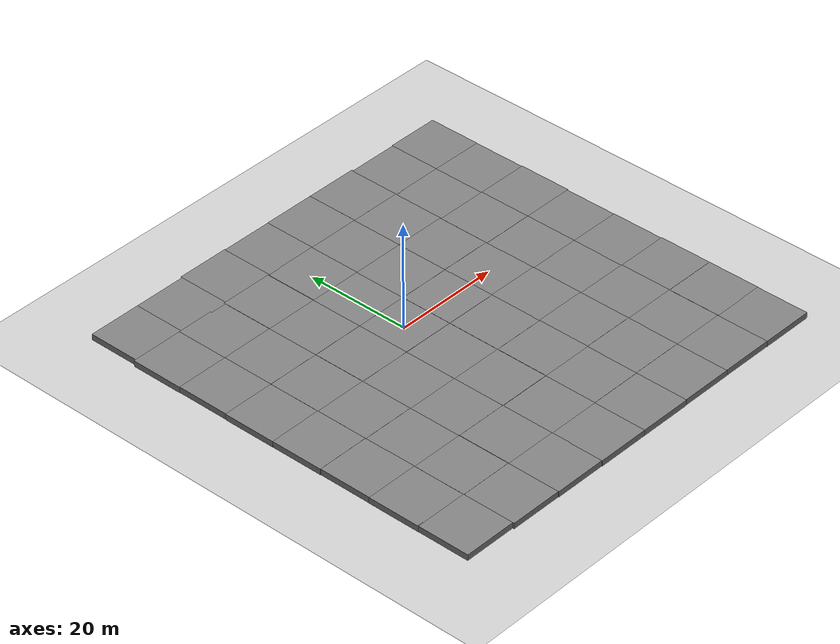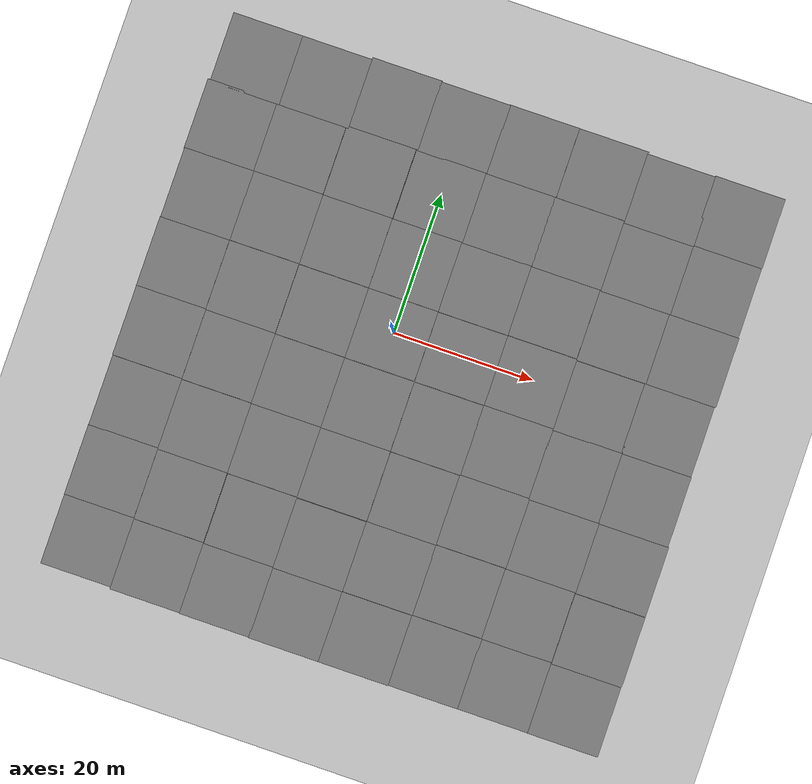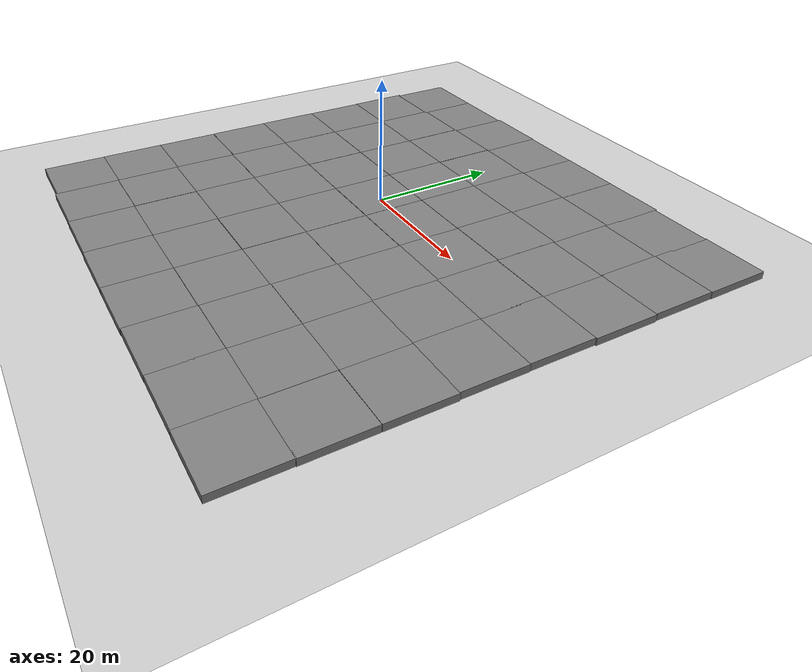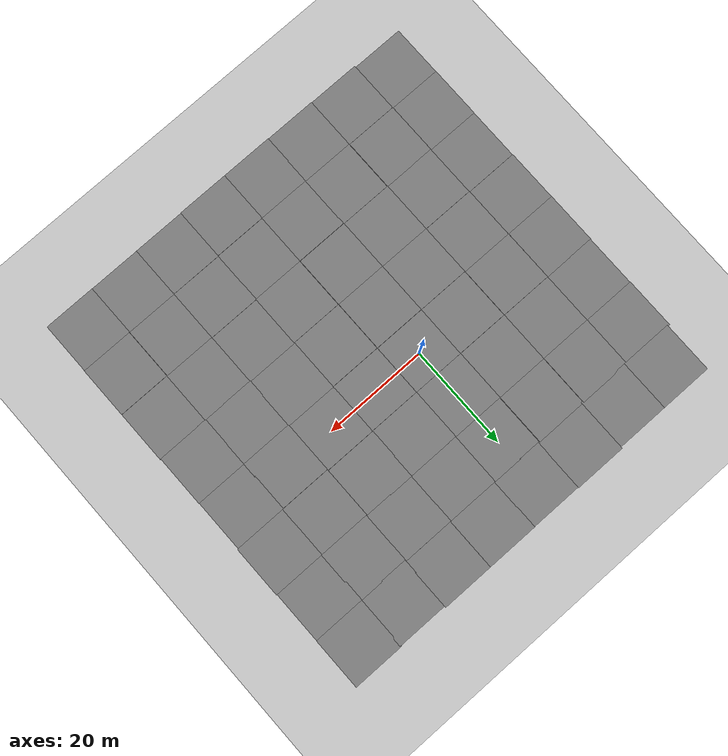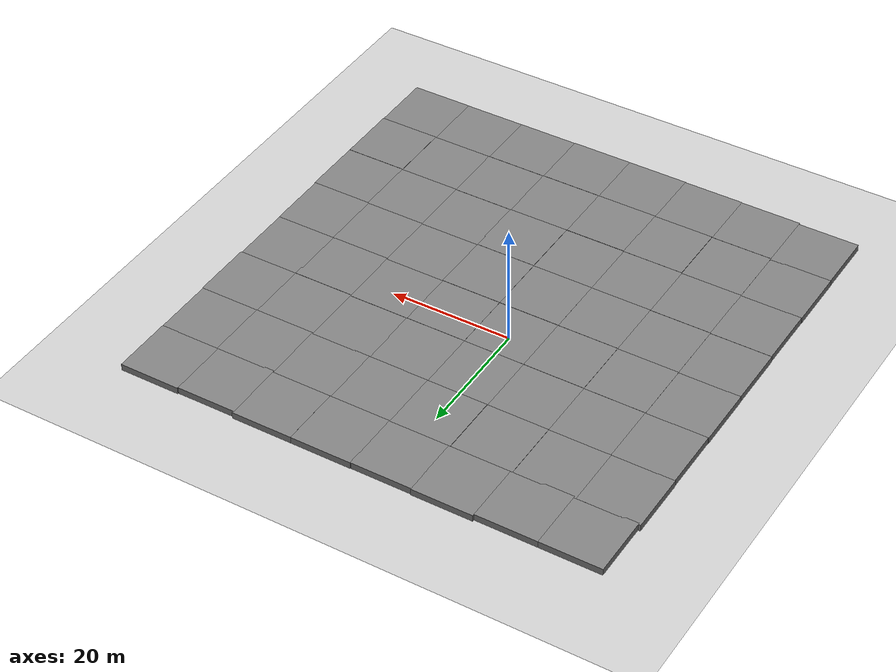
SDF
<sdf version="1.7">
 <world name="default">
  <light name="sun" type="directional">
   <pose>0 0 10 0 -0 0</pose>
   <diffuse>0.8 0.8 0.8 1</diffuse>
   <specular>0.2 0.2 0.2 1</specular>
   <attenuation>
    <range>1000</range>
    <constant>0.9</constant>
    <linear>0.01</linear>
    <quadratic>0.001</quadratic>
   </attenuation>
   <direction>-0.5 0.1 -0.9</direction>
   <spot><inner_angle>0</inner_angle><outer_angle>0</outer_angle><falloff>0</falloff></spot>
  </light>
  <model name="ground_plane">
   <static>1</static>
   <link name="link">
    <collision name="collision">
     <geometry><plane><normal>0 0 1</normal><size>100 100</size></plane></geometry>
     <surface>
      <contact><collide_bitmask>65535</collide_bitmask></contact>
      <friction><ode><mu>100</mu><mu2>50</mu2></ode></friction>
     </surface>
    </collision>
    <visual name="visual">
     <cast_shadows>0</cast_shadows>
     <geometry><plane><normal>0 0 1</normal><size>100 100</size></plane></geometry>
     <material>
      <script><uri>file://media/materials/scripts/gazebo.material</uri><name>Gazebo/Grey</name></script>
     </material>
    </visual>
   </link>
  </model>
  <gravity>0 0 -9.8</gravity>
  <magnetic_field>6e-06 2.3e-05 -4.2e-05</magnetic_field>
  <atmosphere type="adiabatic"/>
  <physics type="ode">
   <max_step_size>0.001</max_step_size>
   <real_time_factor>1</real_time_factor>
   <real_time_update_rate>1000</real_time_update_rate>
  </physics>
  <scene><ambient>0.4 0.4 0.4 1</ambient><background>0.7 0.7 0.7 1</background><shadows>1</shadows></scene>
  <spherical_coordinates>
   <surface_model>EARTH_WGS84</surface_model>
   <latitude_deg>0</latitude_deg>
   <longitude_deg>0</longitude_deg>
   <elevation>0</elevation>
   <heading_deg>0</heading_deg>
  </spherical_coordinates>
  <model name="farm">
   <link name="link">
    <inertial>
     <mass>1</mass>
     <inertia><ixx>1</ixx><ixy>0</ixy><ixz>0</ixz><iyy>1</iyy><iyz>0</iyz><izz>1</izz></inertia>
    </inertial>
    <visual name="visual_1">
     <pose>2 2.5 0 0 -0 0</pose>
     <cast_shadows>0</cast_shadows>
     <geometry><box><size>10 10 2</size></box></geometry>
     <material>
      <script>
       <uri>model://mud_box/materials/scripts</uri>
       <uri>model://mud_box/materials/textures</uri>
       <name>vrc/mud</name>
      </script>
      <shader type="pixel"><normal_map>__default__</normal_map></shader>
      <ambient>0.5 0.5 0.5 1</ambient>
      <diffuse>0.5 0.5 0.5 1</diffuse>
      <specular>0.2 0.2 0.2 1</specular>
      <emissive>0 0 0 1</emissive>
     </material>
    </visual>
    <visual name="visual_2">
     <pose>2 2.5 0 0 -0 0</pose>
     <cast_shadows>0</cast_shadows>
     <geometry><box><size>10 10 2</size></box></geometry>
     <material>
      <script>
       <uri>model://mud_box/materials/scripts</uri>
       <uri>model://mud_box/materials/textures</uri>
       <name>vrc/mud</name>
      </script>
      <shader type="pixel"><normal_map>__default__</normal_map></shader>
      <ambient>0.5 0.5 0.5 1</ambient>
      <diffuse>0.5 0.5 0.5 1</diffuse>
      <specular>0.2 0.2 0.2 1</specular>
      <emissive>0 0 0 1</emissive>
     </material>
    </visual>
    <visual name="visual_4">
     <pose>2 2.5 0 0 -0 0</pose>
     <cast_shadows>0</cast_shadows>
     <geometry><box><size>10 10 2</size></box></geometry>
     <material>
      <script>
       <uri>model://mud_box/materials/scripts</uri>
       <uri>model://mud_box/materials/textures</uri>
       <name>vrc/mud</name>
      </script>
      <shader type="pixel"><normal_map>__default__</normal_map></shader>
      <ambient>0.5 0.5 0.5 1</ambient>
      <diffuse>0.5 0.5 0.5 1</diffuse>
      <specular>0.2 0.2 0.2 1</specular>
      <emissive>0 0 0 1</emissive>
     </material>
    </visual>
    <visual name="visual_3">
     <pose>2 2.5 0 0 -0 0</pose>
     <cast_shadows>0</cast_shadows>
     <geometry><box><size>10 10 2</size></box></geometry>
     <material>
      <script>
       <uri>model://mud_box/materials/scripts</uri>
       <uri>model://mud_box/materials/textures</uri>
       <name>vrc/mud</name>
      </script>
      <shader type="pixel"><normal_map>__default__</normal_map></shader>
      <ambient>0.5 0.5 0.5 1</ambient>
      <diffuse>0.5 0.5 0.5 1</diffuse>
      <specular>0.2 0.2 0.2 1</specular>
      <emissive>0 0 0 1</emissive>
     </material>
    </visual>
    <collision name="collision">
     <laser_retro>0.3</laser_retro>
     <pose>2 2.5 0 0 -0 0</pose>
     <geometry><box><size>100 100 2</size></box></geometry>
     <surface>
      <friction>
       <ode><mu>1.2</mu><mu2>1.2</mu2><fdir1>0 0 0</fdir1><slip1>0.01</slip1><slip2>0.01</slip2></ode>
       <torsional>
        <coefficient>0.05</coefficient>
        <patch_radius>0.08</patch_radius>
        <surface_radius>0.05</surface_radius>
        <use_patch_radius>1</use_patch_radius>
        <ode><slip>0</slip></ode>
       </torsional>
      </friction>
      <bounce><restitution_coefficient>0</restitution_coefficient><threshold>1</threshold></bounce>
      <contact>
       <collide_without_contact>0</collide_without_contact>
       <collide_without_contact_bitmask>1</collide_without_contact_bitmask>
       <collide_bitmask>1</collide_bitmask>
       <ode>
        <soft_cfm>0</soft_cfm>
        <soft_erp>1</soft_erp>
        <kp>1e+07</kp>
        <kd>5000</kd>
        <max_vel>0.001</max_vel>
        <min_depth>0.0005</min_depth>
       </ode>
       <bullet>
        <split_impulse>1</split_impulse>
        <split_impulse_penetration_threshold>-0.01</split_impulse_penetration_threshold>
        <soft_cfm>0</soft_cfm>
        <soft_erp>1</soft_erp>
        <kp>1e+07</kp>
        <kd>5000</kd>
       </bullet>
      </contact>
     </surface>
    </collision>
   </link>
   <static>1</static>
   <pose>-2.22131 -2.84846 0 0 -0 0</pose>
  </model>
  <model name="farm_clone">
   <link name="link">
    <inertial>
     <mass>1</mass>
     <inertia><ixx>1</ixx><ixy>0</ixy><ixz>0</ixz><iyy>1</iyy><iyz>0</iyz><izz>1</izz></inertia>
    </inertial>
    <visual name="visual_1">
     <pose>2 2.5 0 0 -0 0</pose>
     <cast_shadows>0</cast_shadows>
     <geometry><box><size>10 10 2</size></box></geometry>
     <material>
      <script>
       <uri>model://mud_box/materials/scripts</uri>
       <uri>model://mud_box/materials/textures</uri>
       <name>vrc/mud</name>
      </script>
      <shader type="pixel"><normal_map>__default__</normal_map></shader>
      <ambient>0.5 0.5 0.5 1</ambient>
      <diffuse>0.5 0.5 0.5 1</diffuse>
      <specular>0.2 0.2 0.2 1</specular>
      <emissive>0 0 0 1</emissive>
     </material>
    </visual>
    <visual name="visual_2">
     <pose>2 2.5 0 0 -0 0</pose>
     <cast_shadows>0</cast_shadows>
     <geometry><box><size>10 10 2</size></box></geometry>
     <material>
      <script>
       <uri>model://mud_box/materials/scripts</uri>
       <uri>model://mud_box/materials/textures</uri>
       <name>vrc/mud</name>
      </script>
      <shader type="pixel"><normal_map>__default__</normal_map></shader>
      <ambient>0.5 0.5 0.5 1</ambient>
      <diffuse>0.5 0.5 0.5 1</diffuse>
      <specular>0.2 0.2 0.2 1</specular>
      <emissive>0 0 0 1</emissive>
     </material>
    </visual>
    <visual name="visual_4">
     <pose>2 2.5 0 0 -0 0</pose>
     <cast_shadows>0</cast_shadows>
     <geometry><box><size>10 10 2</size></box></geometry>
     <material>
      <script>
       <uri>model://mud_box/materials/scripts</uri>
       <uri>model://mud_box/materials/textures</uri>
       <name>vrc/mud</name>
      </script>
      <shader type="pixel"><normal_map>__default__</normal_map></shader>
      <ambient>0.5 0.5 0.5 1</ambient>
      <diffuse>0.5 0.5 0.5 1</diffuse>
      <specular>0.2 0.2 0.2 1</specular>
      <emissive>0 0 0 1</emissive>
     </material>
    </visual>
    <visual name="visual_3">
     <pose>2 2.5 0 0 -0 0</pose>
     <cast_shadows>0</cast_shadows>
     <geometry><box><size>10 10 2</size></box></geometry>
     <material>
      <script>
       <uri>model://mud_box/materials/scripts</uri>
       <uri>model://mud_box/materials/textures</uri>
       <name>vrc/mud</name>
      </script>
      <shader type="pixel"><normal_map>__default__</normal_map></shader>
      <ambient>0.5 0.5 0.5 1</ambient>
      <diffuse>0.5 0.5 0.5 1</diffuse>
      <specular>0.2 0.2 0.2 1</specular>
      <emissive>0 0 0 1</emissive>
     </material>
    </visual>
    <collision name="collision">
     <laser_retro>0.3</laser_retro>
     <pose>2 2.5 0 0 -0 0</pose>
     <geometry><box><size>100 100 2</size></box></geometry>
     <surface>
      <friction>
       <ode><mu>1.2</mu><mu2>1.2</mu2><fdir1>0 0 0</fdir1><slip1>0.01</slip1><slip2>0.01</slip2></ode>
       <torsional>
        <coefficient>0.05</coefficient>
        <patch_radius>0.08</patch_radius>
        <surface_radius>0.05</surface_radius>
        <use_patch_radius>1</use_patch_radius>
        <ode><slip>0</slip></ode>
       </torsional>
      </friction>
      <bounce><restitution_coefficient>0</restitution_coefficient><threshold>1</threshold></bounce>
      <contact>
       <collide_without_contact>0</collide_without_contact>
       <collide_without_contact_bitmask>1</collide_without_contact_bitmask>
       <collide_bitmask>1</collide_bitmask>
       <ode>
        <soft_cfm>0</soft_cfm>
        <soft_erp>1</soft_erp>
        <kp>1e+07</kp>
        <kd>5000</kd>
        <max_vel>0.001</max_vel>
        <min_depth>0.0005</min_depth>
       </ode>
       <bullet>
        <split_impulse>1</split_impulse>
        <split_impulse_penetration_threshold>-0.01</split_impulse_penetration_threshold>
        <soft_cfm>0</soft_cfm>
        <soft_erp>1</soft_erp>
        <kp>1e+07</kp>
        <kd>5000</kd>
       </bullet>
      </contact>
     </surface>
    </collision>
   </link>
   <static>1</static>
   <pose>-2.23193 -12.8916 0 0 -0 0</pose>
  </model>
  <model name="farm_clone_0">
   <link name="link">
    <inertial>
     <mass>1</mass>
     <inertia><ixx>1</ixx><ixy>0</ixy><ixz>0</ixz><iyy>1</iyy><iyz>0</iyz><izz>1</izz></inertia>
    </inertial>
    <visual name="visual_1">
     <pose>2 2.5 0 0 -0 0</pose>
     <cast_shadows>0</cast_shadows>
     <geometry><box><size>10 10 2</size></box></geometry>
     <material>
      <script>
       <uri>model://mud_box/materials/scripts</uri>
       <uri>model://mud_box/materials/textures</uri>
       <name>vrc/mud</name>
      </script>
      <shader type="pixel"><normal_map>__default__</normal_map></shader>
      <ambient>0.5 0.5 0.5 1</ambient>
      <diffuse>0.5 0.5 0.5 1</diffuse>
      <specular>0.2 0.2 0.2 1</specular>
      <emissive>0 0 0 1</emissive>
     </material>
    </visual>
    <visual name="visual_2">
     <pose>2 2.5 0 0 -0 0</pose>
     <cast_shadows>0</cast_shadows>
     <geometry><box><size>10 10 2</size></box></geometry>
     <material>
      <script>
       <uri>model://mud_box/materials/scripts</uri>
       <uri>model://mud_box/materials/textures</uri>
       <name>vrc/mud</name>
      </script>
      <shader type="pixel"><normal_map>__default__</normal_map></shader>
      <ambient>0.5 0.5 0.5 1</ambient>
      <diffuse>0.5 0.5 0.5 1</diffuse>
      <specular>0.2 0.2 0.2 1</specular>
      <emissive>0 0 0 1</emissive>
     </material>
    </visual>
    <visual name="visual_4">
     <pose>2 2.5 0 0 -0 0</pose>
     <cast_shadows>0</cast_shadows>
     <geometry><box><size>10 10 2</size></box></geometry>
     <material>
      <script>
       <uri>model://mud_box/materials/scripts</uri>
       <uri>model://mud_box/materials/textures</uri>
       <name>vrc/mud</name>
      </script>
      <shader type="pixel"><normal_map>__default__</normal_map></shader>
      <ambient>0.5 0.5 0.5 1</ambient>
      <diffuse>0.5 0.5 0.5 1</diffuse>
      <specular>0.2 0.2 0.2 1</specular>
      <emissive>0 0 0 1</emissive>
     </material>
    </visual>
    <visual name="visual_3">
     <pose>2 2.5 0 0 -0 0</pose>
     <cast_shadows>0</cast_shadows>
     <geometry><box><size>10 10 2</size></box></geometry>
     <material>
      <script>
       <uri>model://mud_box/materials/scripts</uri>
       <uri>model://mud_box/materials/textures</uri>
       <name>vrc/mud</name>
      </script>
      <shader type="pixel"><normal_map>__default__</normal_map></shader>
      <ambient>0.5 0.5 0.5 1</ambient>
      <diffuse>0.5 0.5 0.5 1</diffuse>
      <specular>0.2 0.2 0.2 1</specular>
      <emissive>0 0 0 1</emissive>
     </material>
    </visual>
    <collision name="collision">
     <laser_retro>0.3</laser_retro>
     <pose>2 2.5 0 0 -0 0</pose>
     <geometry><box><size>100 100 2</size></box></geometry>
     <surface>
      <friction>
       <ode><mu>1.2</mu><mu2>1.2</mu2><fdir1>0 0 0</fdir1><slip1>0.01</slip1><slip2>0.01</slip2></ode>
       <torsional>
        <coefficient>0.05</coefficient>
        <patch_radius>0.08</patch_radius>
        <surface_radius>0.05</surface_radius>
        <use_patch_radius>1</use_patch_radius>
        <ode><slip>0</slip></ode>
       </torsional>
      </friction>
      <bounce><restitution_coefficient>0</restitution_coefficient><threshold>1</threshold></bounce>
      <contact>
       <collide_without_contact>0</collide_without_contact>
       <collide_without_contact_bitmask>1</collide_without_contact_bitmask>
       <collide_bitmask>1</collide_bitmask>
       <ode>
        <soft_cfm>0</soft_cfm>
        <soft_erp>1</soft_erp>
        <kp>1e+07</kp>
        <kd>5000</kd>
        <max_vel>0.001</max_vel>
        <min_depth>0.0005</min_depth>
       </ode>
       <bullet>
        <split_impulse>1</split_impulse>
        <split_impulse_penetration_threshold>-0.01</split_impulse_penetration_threshold>
        <soft_cfm>0</soft_cfm>
        <soft_erp>1</soft_erp>
        <kp>1e+07</kp>
        <kd>5000</kd>
       </bullet>
      </contact>
     </surface>
    </collision>
   </link>
   <static>1</static>
   <pose>-2.22199 -22.8913 0 0 -0 0</pose>
  </model>
  <model name="farm_clone_0_clone">
   <link name="link">
    <inertial>
     <mass>1</mass>
     <inertia><ixx>1</ixx><ixy>0</ixy><ixz>0</ixz><iyy>1</iyy><iyz>0</iyz><izz>1</izz></inertia>
    </inertial>
    <visual name="visual_1">
     <pose>2 2.5 0 0 -0 0</pose>
     <cast_shadows>0</cast_shadows>
     <geometry><box><size>10 10 2</size></box></geometry>
     <material>
      <script>
       <uri>model://mud_box/materials/scripts</uri>
       <uri>model://mud_box/materials/textures</uri>
       <name>vrc/mud</name>
      </script>
      <shader type="pixel"><normal_map>__default__</normal_map></shader>
      <ambient>0.5 0.5 0.5 1</ambient>
      <diffuse>0.5 0.5 0.5 1</diffuse>
      <specular>0.2 0.2 0.2 1</specular>
      <emissive>0 0 0 1</emissive>
     </material>
    </visual>
    <visual name="visual_2">
     <pose>2 2.5 0 0 -0 0</pose>
     <cast_shadows>0</cast_shadows>
     <geometry><box><size>10 10 2</size></box></geometry>
     <material>
      <script>
       <uri>model://mud_box/materials/scripts</uri>
       <uri>model://mud_box/materials/textures</uri>
       <name>vrc/mud</name>
      </script>
      <shader type="pixel"><normal_map>__default__</normal_map></shader>
      <ambient>0.5 0.5 0.5 1</ambient>
      <diffuse>0.5 0.5 0.5 1</diffuse>
      <specular>0.2 0.2 0.2 1</specular>
      <emissive>0 0 0 1</emissive>
     </material>
    </visual>
    <visual name="visual_4">
     <pose>2 2.5 0 0 -0 0</pose>
     <cast_shadows>0</cast_shadows>
     <geometry><box><size>10 10 2</size></box></geometry>
     <material>
      <script>
       <uri>model://mud_box/materials/scripts</uri>
       <uri>model://mud_box/materials/textures</uri>
       <name>vrc/mud</name>
      </script>
      <shader type="pixel"><normal_map>__default__</normal_map></shader>
      <ambient>0.5 0.5 0.5 1</ambient>
      <diffuse>0.5 0.5 0.5 1</diffuse>
      <specular>0.2 0.2 0.2 1</specular>
      <emissive>0 0 0 1</emissive>
     </material>
    </visual>
    <visual name="visual_3">
     <pose>2 2.5 0 0 -0 0</pose>
     <cast_shadows>0</cast_shadows>
     <geometry><box><size>10 10 2</size></box></geometry>
     <material>
      <script>
       <uri>model://mud_box/materials/scripts</uri>
       <uri>model://mud_box/materials/textures</uri>
       <name>vrc/mud</name>
      </script>
      <shader type="pixel"><normal_map>__default__</normal_map></shader>
      <ambient>0.5 0.5 0.5 1</ambient>
      <diffuse>0.5 0.5 0.5 1</diffuse>
      <specular>0.2 0.2 0.2 1</specular>
      <emissive>0 0 0 1</emissive>
     </material>
    </visual>
    <collision name="collision">
     <laser_retro>0.3</laser_retro>
     <pose>2 2.5 0 0 -0 0</pose>
     <geometry><box><size>100 100 2</size></box></geometry>
     <surface>
      <friction>
       <ode><mu>1.2</mu><mu2>1.2</mu2><fdir1>0 0 0</fdir1><slip1>0.01</slip1><slip2>0.01</slip2></ode>
       <torsional>
        <coefficient>0.05</coefficient>
        <patch_radius>0.08</patch_radius>
        <surface_radius>0.05</surface_radius>
        <use_patch_radius>1</use_patch_radius>
        <ode><slip>0</slip></ode>
       </torsional>
      </friction>
      <bounce><restitution_coefficient>0</restitution_coefficient><threshold>1</threshold></bounce>
      <contact>
       <collide_without_contact>0</collide_without_contact>
       <collide_without_contact_bitmask>1</collide_without_contact_bitmask>
       <collide_bitmask>1</collide_bitmask>
       <ode>
        <soft_cfm>0</soft_cfm>
        <soft_erp>1</soft_erp>
        <kp>1e+07</kp>
        <kd>5000</kd>
        <max_vel>0.001</max_vel>
        <min_depth>0.0005</min_depth>
       </ode>
       <bullet>
        <split_impulse>1</split_impulse>
        <split_impulse_penetration_threshold>-0.01</split_impulse_penetration_threshold>
        <soft_cfm>0</soft_cfm>
        <soft_erp>1</soft_erp>
        <kp>1e+07</kp>
        <kd>5000</kd>
       </bullet>
      </contact>
     </surface>
    </collision>
   </link>
   <static>1</static>
   <pose>-12.2084 -2.84715 0 0 -0 0</pose>
  </model>
  <model name="farm_clone_0_clone_0">
   <link name="link">
    <inertial>
     <mass>1</mass>
     <inertia><ixx>1</ixx><ixy>0</ixy><ixz>0</ixz><iyy>1</iyy><iyz>0</iyz><izz>1</izz></inertia>
    </inertial>
    <visual name="visual_1">
     <pose>2 2.5 0 0 -0 0</pose>
     <cast_shadows>0</cast_shadows>
     <geometry><box><size>10 10 2</size></box></geometry>
     <material>
      <script>
       <uri>model://mud_box/materials/scripts</uri>
       <uri>model://mud_box/materials/textures</uri>
       <name>vrc/mud</name>
      </script>
      <shader type="pixel"><normal_map>__default__</normal_map></shader>
      <ambient>0.5 0.5 0.5 1</ambient>
      <diffuse>0.5 0.5 0.5 1</diffuse>
      <specular>0.2 0.2 0.2 1</specular>
      <emissive>0 0 0 1</emissive>
     </material>
    </visual>
    <visual name="visual_2">
     <pose>2 2.5 0 0 -0 0</pose>
     <cast_shadows>0</cast_shadows>
     <geometry><box><size>10 10 2</size></box></geometry>
     <material>
      <script>
       <uri>model://mud_box/materials/scripts</uri>
       <uri>model://mud_box/materials/textures</uri>
       <name>vrc/mud</name>
      </script>
      <shader type="pixel"><normal_map>__default__</normal_map></shader>
      <ambient>0.5 0.5 0.5 1</ambient>
      <diffuse>0.5 0.5 0.5 1</diffuse>
      <specular>0.2 0.2 0.2 1</specular>
      <emissive>0 0 0 1</emissive>
     </material>
    </visual>
    <visual name="visual_4">
     <pose>2 2.5 0 0 -0 0</pose>
     <cast_shadows>0</cast_shadows>
     <geometry><box><size>10 10 2</size></box></geometry>
     <material>
      <script>
       <uri>model://mud_box/materials/scripts</uri>
       <uri>model://mud_box/materials/textures</uri>
       <name>vrc/mud</name>
      </script>
      <shader type="pixel"><normal_map>__default__</normal_map></shader>
      <ambient>0.5 0.5 0.5 1</ambient>
      <diffuse>0.5 0.5 0.5 1</diffuse>
      <specular>0.2 0.2 0.2 1</specular>
      <emissive>0 0 0 1</emissive>
     </material>
    </visual>
    <visual name="visual_3">
     <pose>2 2.5 0 0 -0 0</pose>
     <cast_shadows>0</cast_shadows>
     <geometry><box><size>10 10 2</size></box></geometry>
     <material>
      <script>
       <uri>model://mud_box/materials/scripts</uri>
       <uri>model://mud_box/materials/textures</uri>
       <name>vrc/mud</name>
      </script>
      <shader type="pixel"><normal_map>__default__</normal_map></shader>
      <ambient>0.5 0.5 0.5 1</ambient>
      <diffuse>0.5 0.5 0.5 1</diffuse>
      <specular>0.2 0.2 0.2 1</specular>
      <emissive>0 0 0 1</emissive>
     </material>
    </visual>
    <collision name="collision">
     <laser_retro>0.3</laser_retro>
     <pose>2 2.5 0 0 -0 0</pose>
     <geometry><box><size>100 100 2</size></box></geometry>
     <surface>
      <friction>
       <ode><mu>1.2</mu><mu2>1.2</mu2><fdir1>0 0 0</fdir1><slip1>0.01</slip1><slip2>0.01</slip2></ode>
       <torsional>
        <coefficient>0.05</coefficient>
        <patch_radius>0.08</patch_radius>
        <surface_radius>0.05</surface_radius>
        <use_patch_radius>1</use_patch_radius>
        <ode><slip>0</slip></ode>
       </torsional>
      </friction>
      <bounce><restitution_coefficient>0</restitution_coefficient><threshold>1</threshold></bounce>
      <contact>
       <collide_without_contact>0</collide_without_contact>
       <collide_without_contact_bitmask>1</collide_without_contact_bitmask>
       <collide_bitmask>1</collide_bitmask>
       <ode>
        <soft_cfm>0</soft_cfm>
        <soft_erp>1</soft_erp>
        <kp>1e+07</kp>
        <kd>5000</kd>
        <max_vel>0.001</max_vel>
        <min_depth>0.0005</min_depth>
       </ode>
       <bullet>
        <split_impulse>1</split_impulse>
        <split_impulse_penetration_threshold>-0.01</split_impulse_penetration_threshold>
        <soft_cfm>0</soft_cfm>
        <soft_erp>1</soft_erp>
        <kp>1e+07</kp>
        <kd>5000</kd>
       </bullet>
      </contact>
     </surface>
    </collision>
   </link>
   <static>1</static>
   <pose>-12.233 -12.8623 0 0 -0 0</pose>
  </model>
  <model name="farm_clone_0_clone_1">
   <link name="link">
    <inertial>
     <mass>1</mass>
     <inertia><ixx>1</ixx><ixy>0</ixy><ixz>0</ixz><iyy>1</iyy><iyz>0</iyz><izz>1</izz></inertia>
    </inertial>
    <visual name="visual_1">
     <pose>2 2.5 0 0 -0 0</pose>
     <cast_shadows>0</cast_shadows>
     <geometry><box><size>10 10 2</size></box></geometry>
     <material>
      <script>
       <uri>model://mud_box/materials/scripts</uri>
       <uri>model://mud_box/materials/textures</uri>
       <name>vrc/mud</name>
      </script>
      <shader type="pixel"><normal_map>__default__</normal_map></shader>
      <ambient>0.5 0.5 0.5 1</ambient>
      <diffuse>0.5 0.5 0.5 1</diffuse>
      <specular>0.2 0.2 0.2 1</specular>
      <emissive>0 0 0 1</emissive>
     </material>
    </visual>
    <visual name="visual_2">
     <pose>2 2.5 0 0 -0 0</pose>
     <cast_shadows>0</cast_shadows>
     <geometry><box><size>10 10 2</size></box></geometry>
     <material>
      <script>
       <uri>model://mud_box/materials/scripts</uri>
       <uri>model://mud_box/materials/textures</uri>
       <name>vrc/mud</name>
      </script>
      <shader type="pixel"><normal_map>__default__</normal_map></shader>
      <ambient>0.5 0.5 0.5 1</ambient>
      <diffuse>0.5 0.5 0.5 1</diffuse>
      <specular>0.2 0.2 0.2 1</specular>
      <emissive>0 0 0 1</emissive>
     </material>
    </visual>
    <visual name="visual_4">
     <pose>2 2.5 0 0 -0 0</pose>
     <cast_shadows>0</cast_shadows>
     <geometry><box><size>10 10 2</size></box></geometry>
     <material>
      <script>
       <uri>model://mud_box/materials/scripts</uri>
       <uri>model://mud_box/materials/textures</uri>
       <name>vrc/mud</name>
      </script>
      <shader type="pixel"><normal_map>__default__</normal_map></shader>
      <ambient>0.5 0.5 0.5 1</ambient>
      <diffuse>0.5 0.5 0.5 1</diffuse>
      <specular>0.2 0.2 0.2 1</specular>
      <emissive>0 0 0 1</emissive>
     </material>
    </visual>
    <visual name="visual_3">
     <pose>2 2.5 0 0 -0 0</pose>
     <cast_shadows>0</cast_shadows>
     <geometry><box><size>10 10 2</size></box></geometry>
     <material>
      <script>
       <uri>model://mud_box/materials/scripts</uri>
       <uri>model://mud_box/materials/textures</uri>
       <name>vrc/mud</name>
      </script>
      <shader type="pixel"><normal_map>__default__</normal_map></shader>
      <ambient>0.5 0.5 0.5 1</ambient>
      <diffuse>0.5 0.5 0.5 1</diffuse>
      <specular>0.2 0.2 0.2 1</specular>
      <emissive>0 0 0 1</emissive>
     </material>
    </visual>
    <collision name="collision">
     <laser_retro>0.3</laser_retro>
     <pose>2 2.5 0 0 -0 0</pose>
     <geometry><box><size>100 100 2</size></box></geometry>
     <surface>
      <friction>
       <ode><mu>1.2</mu><mu2>1.2</mu2><fdir1>0 0 0</fdir1><slip1>0.01</slip1><slip2>0.01</slip2></ode>
       <torsional>
        <coefficient>0.05</coefficient>
        <patch_radius>0.08</patch_radius>
        <surface_radius>0.05</surface_radius>
        <use_patch_radius>1</use_patch_radius>
        <ode><slip>0</slip></ode>
       </torsional>
      </friction>
      <bounce><restitution_coefficient>0</restitution_coefficient><threshold>1</threshold></bounce>
      <contact>
       <collide_without_contact>0</collide_without_contact>
       <collide_without_contact_bitmask>1</collide_without_contact_bitmask>
       <collide_bitmask>1</collide_bitmask>
       <ode>
        <soft_cfm>0</soft_cfm>
        <soft_erp>1</soft_erp>
        <kp>1e+07</kp>
        <kd>5000</kd>
        <max_vel>0.001</max_vel>
        <min_depth>0.0005</min_depth>
       </ode>
       <bullet>
        <split_impulse>1</split_impulse>
        <split_impulse_penetration_threshold>-0.01</split_impulse_penetration_threshold>
        <soft_cfm>0</soft_cfm>
        <soft_erp>1</soft_erp>
        <kp>1e+07</kp>
        <kd>5000</kd>
       </bullet>
      </contact>
     </surface>
    </collision>
   </link>
   <static>1</static>
   <pose>-12.2184 -22.8542 0 0 -0 0</pose>
  </model>
  <model name="farm_clone_0_clone_1_clone">
   <link name="link">
    <inertial>
     <mass>1</mass>
     <inertia><ixx>1</ixx><ixy>0</ixy><ixz>0</ixz><iyy>1</iyy><iyz>0</iyz><izz>1</izz></inertia>
    </inertial>
    <visual name="visual_1">
     <pose>2 2.5 0 0 -0 0</pose>
     <cast_shadows>0</cast_shadows>
     <geometry><box><size>10 10 2</size></box></geometry>
     <material>
      <script>
       <uri>model://mud_box/materials/scripts</uri>
       <uri>model://mud_box/materials/textures</uri>
       <name>vrc/mud</name>
      </script>
      <shader type="pixel"><normal_map>__default__</normal_map></shader>
      <ambient>0.5 0.5 0.5 1</ambient>
      <diffuse>0.5 0.5 0.5 1</diffuse>
      <specular>0.2 0.2 0.2 1</specular>
      <emissive>0 0 0 1</emissive>
     </material>
    </visual>
    <visual name="visual_2">
     <pose>2 2.5 0 0 -0 0</pose>
     <cast_shadows>0</cast_shadows>
     <geometry><box><size>10 10 2</size></box></geometry>
     <material>
      <script>
       <uri>model://mud_box/materials/scripts</uri>
       <uri>model://mud_box/materials/textures</uri>
       <name>vrc/mud</name>
      </script>
      <shader type="pixel"><normal_map>__default__</normal_map></shader>
      <ambient>0.5 0.5 0.5 1</ambient>
      <diffuse>0.5 0.5 0.5 1</diffuse>
      <specular>0.2 0.2 0.2 1</specular>
      <emissive>0 0 0 1</emissive>
     </material>
    </visual>
    <visual name="visual_4">
     <pose>2 2.5 0 0 -0 0</pose>
     <cast_shadows>0</cast_shadows>
     <geometry><box><size>10 10 2</size></box></geometry>
     <material>
      <script>
       <uri>model://mud_box/materials/scripts</uri>
       <uri>model://mud_box/materials/textures</uri>
       <name>vrc/mud</name>
      </script>
      <shader type="pixel"><normal_map>__default__</normal_map></shader>
      <ambient>0.5 0.5 0.5 1</ambient>
      <diffuse>0.5 0.5 0.5 1</diffuse>
      <specular>0.2 0.2 0.2 1</specular>
      <emissive>0 0 0 1</emissive>
     </material>
    </visual>
    <visual name="visual_3">
     <pose>2 2.5 0 0 -0 0</pose>
     <cast_shadows>0</cast_shadows>
     <geometry><box><size>10 10 2</size></box></geometry>
     <material>
      <script>
       <uri>model://mud_box/materials/scripts</uri>
       <uri>model://mud_box/materials/textures</uri>
       <name>vrc/mud</name>
      </script>
      <shader type="pixel"><normal_map>__default__</normal_map></shader>
      <ambient>0.5 0.5 0.5 1</ambient>
      <diffuse>0.5 0.5 0.5 1</diffuse>
      <specular>0.2 0.2 0.2 1</specular>
      <emissive>0 0 0 1</emissive>
     </material>
    </visual>
    <collision name="collision">
     <laser_retro>0.3</laser_retro>
     <pose>2 2.5 0 0 -0 0</pose>
     <geometry><box><size>100 100 2</size></box></geometry>
     <surface>
      <friction>
       <ode><mu>1.2</mu><mu2>1.2</mu2><fdir1>0 0 0</fdir1><slip1>0.01</slip1><slip2>0.01</slip2></ode>
       <torsional>
        <coefficient>0.05</coefficient>
        <patch_radius>0.08</patch_radius>
        <surface_radius>0.05</surface_radius>
        <use_patch_radius>1</use_patch_radius>
        <ode><slip>0</slip></ode>
       </torsional>
      </friction>
      <bounce><restitution_coefficient>0</restitution_coefficient><threshold>1</threshold></bounce>
      <contact>
       <collide_without_contact>0</collide_without_contact>
       <collide_without_contact_bitmask>1</collide_without_contact_bitmask>
       <collide_bitmask>1</collide_bitmask>
       <ode>
        <soft_cfm>0</soft_cfm>
        <soft_erp>1</soft_erp>
        <kp>1e+07</kp>
        <kd>5000</kd>
        <max_vel>0.001</max_vel>
        <min_depth>0.0005</min_depth>
       </ode>
       <bullet>
        <split_impulse>1</split_impulse>
        <split_impulse_penetration_threshold>-0.01</split_impulse_penetration_threshold>
        <soft_cfm>0</soft_cfm>
        <soft_erp>1</soft_erp>
        <kp>1e+07</kp>
        <kd>5000</kd>
       </bullet>
      </contact>
     </surface>
    </collision>
   </link>
   <static>1</static>
   <pose>-22.2365 -2.79984 0 0 -0 0</pose>
  </model>
  <model name="farm_clone_0_clone_1_clone_0">
   <link name="link">
    <inertial>
     <mass>1</mass>
     <inertia><ixx>1</ixx><ixy>0</ixy><ixz>0</ixz><iyy>1</iyy><iyz>0</iyz><izz>1</izz></inertia>
    </inertial>
    <visual name="visual_1">
     <pose>2 2.5 0 0 -0 0</pose>
     <cast_shadows>0</cast_shadows>
     <geometry><box><size>10 10 2</size></box></geometry>
     <material>
      <script>
       <uri>model://mud_box/materials/scripts</uri>
       <uri>model://mud_box/materials/textures</uri>
       <name>vrc/mud</name>
      </script>
      <shader type="pixel"><normal_map>__default__</normal_map></shader>
      <ambient>0.5 0.5 0.5 1</ambient>
      <diffuse>0.5 0.5 0.5 1</diffuse>
      <specular>0.2 0.2 0.2 1</specular>
      <emissive>0 0 0 1</emissive>
     </material>
    </visual>
    <visual name="visual_2">
     <pose>2 2.5 0 0 -0 0</pose>
     <cast_shadows>0</cast_shadows>
     <geometry><box><size>10 10 2</size></box></geometry>
     <material>
      <script>
       <uri>model://mud_box/materials/scripts</uri>
       <uri>model://mud_box/materials/textures</uri>
       <name>vrc/mud</name>
      </script>
      <shader type="pixel"><normal_map>__default__</normal_map></shader>
      <ambient>0.5 0.5 0.5 1</ambient>
      <diffuse>0.5 0.5 0.5 1</diffuse>
      <specular>0.2 0.2 0.2 1</specular>
      <emissive>0 0 0 1</emissive>
     </material>
    </visual>
    <visual name="visual_4">
     <pose>2 2.5 0 0 -0 0</pose>
     <cast_shadows>0</cast_shadows>
     <geometry><box><size>10 10 2</size></box></geometry>
     <material>
      <script>
       <uri>model://mud_box/materials/scripts</uri>
       <uri>model://mud_box/materials/textures</uri>
       <name>vrc/mud</name>
      </script>
      <shader type="pixel"><normal_map>__default__</normal_map></shader>
      <ambient>0.5 0.5 0.5 1</ambient>
      <diffuse>0.5 0.5 0.5 1</diffuse>
      <specular>0.2 0.2 0.2 1</specular>
      <emissive>0 0 0 1</emissive>
     </material>
    </visual>
    <visual name="visual_3">
     <pose>2 2.5 0 0 -0 0</pose>
     <cast_shadows>0</cast_shadows>
     <geometry><box><size>10 10 2</size></box></geometry>
     <material>
      <script>
       <uri>model://mud_box/materials/scripts</uri>
       <uri>model://mud_box/materials/textures</uri>
       <name>vrc/mud</name>
      </script>
      <shader type="pixel"><normal_map>__default__</normal_map></shader>
      <ambient>0.5 0.5 0.5 1</ambient>
      <diffuse>0.5 0.5 0.5 1</diffuse>
      <specular>0.2 0.2 0.2 1</specular>
      <emissive>0 0 0 1</emissive>
     </material>
    </visual>
    <collision name="collision">
     <laser_retro>0.3</laser_retro>
     <pose>2 2.5 0 0 -0 0</pose>
     <geometry><box><size>100 100 2</size></box></geometry>
     <surface>
      <friction>
       <ode><mu>1.2</mu><mu2>1.2</mu2><fdir1>0 0 0</fdir1><slip1>0.01</slip1><slip2>0.01</slip2></ode>
       <torsional>
        <coefficient>0.05</coefficient>
        <patch_radius>0.08</patch_radius>
        <surface_radius>0.05</surface_radius>
        <use_patch_radius>1</use_patch_radius>
        <ode><slip>0</slip></ode>
       </torsional>
      </friction>
      <bounce><restitution_coefficient>0</restitution_coefficient><threshold>1</threshold></bounce>
      <contact>
       <collide_without_contact>0</collide_without_contact>
       <collide_without_contact_bitmask>1</collide_without_contact_bitmask>
       <collide_bitmask>1</collide_bitmask>
       <ode>
        <soft_cfm>0</soft_cfm>
        <soft_erp>1</soft_erp>
        <kp>1e+07</kp>
        <kd>5000</kd>
        <max_vel>0.001</max_vel>
        <min_depth>0.0005</min_depth>
       </ode>
       <bullet>
        <split_impulse>1</split_impulse>
        <split_impulse_penetration_threshold>-0.01</split_impulse_penetration_threshold>
        <soft_cfm>0</soft_cfm>
        <soft_erp>1</soft_erp>
        <kp>1e+07</kp>
        <kd>5000</kd>
       </bullet>
      </contact>
     </surface>
    </collision>
   </link>
   <static>1</static>
   <pose>-22.2078 -12.7905 0 0 -0 0</pose>
  </model>
  <model name="farm_clone_0_clone_1_clone_1">
   <link name="link">
    <inertial>
     <mass>1</mass>
     <inertia><ixx>1</ixx><ixy>0</ixy><ixz>0</ixz><iyy>1</iyy><iyz>0</iyz><izz>1</izz></inertia>
    </inertial>
    <visual name="visual_1">
     <pose>2 2.5 0 0 -0 0</pose>
     <cast_shadows>0</cast_shadows>
     <geometry><box><size>10 10 2</size></box></geometry>
     <material>
      <script>
       <uri>model://mud_box/materials/scripts</uri>
       <uri>model://mud_box/materials/textures</uri>
       <name>vrc/mud</name>
      </script>
      <shader type="pixel"><normal_map>__default__</normal_map></shader>
      <ambient>0.5 0.5 0.5 1</ambient>
      <diffuse>0.5 0.5 0.5 1</diffuse>
      <specular>0.2 0.2 0.2 1</specular>
      <emissive>0 0 0 1</emissive>
     </material>
    </visual>
    <visual name="visual_2">
     <pose>2 2.5 0 0 -0 0</pose>
     <cast_shadows>0</cast_shadows>
     <geometry><box><size>10 10 2</size></box></geometry>
     <material>
      <script>
       <uri>model://mud_box/materials/scripts</uri>
       <uri>model://mud_box/materials/textures</uri>
       <name>vrc/mud</name>
      </script>
      <shader type="pixel"><normal_map>__default__</normal_map></shader>
      <ambient>0.5 0.5 0.5 1</ambient>
      <diffuse>0.5 0.5 0.5 1</diffuse>
      <specular>0.2 0.2 0.2 1</specular>
      <emissive>0 0 0 1</emissive>
     </material>
    </visual>
    <visual name="visual_4">
     <pose>2 2.5 0 0 -0 0</pose>
     <cast_shadows>0</cast_shadows>
     <geometry><box><size>10 10 2</size></box></geometry>
     <material>
      <script>
       <uri>model://mud_box/materials/scripts</uri>
       <uri>model://mud_box/materials/textures</uri>
       <name>vrc/mud</name>
      </script>
      <shader type="pixel"><normal_map>__default__</normal_map></shader>
      <ambient>0.5 0.5 0.5 1</ambient>
      <diffuse>0.5 0.5 0.5 1</diffuse>
      <specular>0.2 0.2 0.2 1</specular>
      <emissive>0 0 0 1</emissive>
     </material>
    </visual>
    <visual name="visual_3">
     <pose>2 2.5 0 0 -0 0</pose>
     <cast_shadows>0</cast_shadows>
     <geometry><box><size>10 10 2</size></box></geometry>
     <material>
      <script>
       <uri>model://mud_box/materials/scripts</uri>
       <uri>model://mud_box/materials/textures</uri>
       <name>vrc/mud</name>
      </script>
      <shader type="pixel"><normal_map>__default__</normal_map></shader>
      <ambient>0.5 0.5 0.5 1</ambient>
      <diffuse>0.5 0.5 0.5 1</diffuse>
      <specular>0.2 0.2 0.2 1</specular>
      <emissive>0 0 0 1</emissive>
     </material>
    </visual>
    <collision name="collision">
     <laser_retro>0.3</laser_retro>
     <pose>2 2.5 0 0 -0 0</pose>
     <geometry><box><size>100 100 2</size></box></geometry>
     <surface>
      <friction>
       <ode><mu>1.2</mu><mu2>1.2</mu2><fdir1>0 0 0</fdir1><slip1>0.01</slip1><slip2>0.01</slip2></ode>
       <torsional>
        <coefficient>0.05</coefficient>
        <patch_radius>0.08</patch_radius>
        <surface_radius>0.05</surface_radius>
        <use_patch_radius>1</use_patch_radius>
        <ode><slip>0</slip></ode>
       </torsional>
      </friction>
      <bounce><restitution_coefficient>0</restitution_coefficient><threshold>1</threshold></bounce>
      <contact>
       <collide_without_contact>0</collide_without_contact>
       <collide_without_contact_bitmask>1</collide_without_contact_bitmask>
       <collide_bitmask>1</collide_bitmask>
       <ode>
        <soft_cfm>0</soft_cfm>
        <soft_erp>1</soft_erp>
        <kp>1e+07</kp>
        <kd>5000</kd>
        <max_vel>0.001</max_vel>
        <min_depth>0.0005</min_depth>
       </ode>
       <bullet>
        <split_impulse>1</split_impulse>
        <split_impulse_penetration_threshold>-0.01</split_impulse_penetration_threshold>
        <soft_cfm>0</soft_cfm>
        <soft_erp>1</soft_erp>
        <kp>1e+07</kp>
        <kd>5000</kd>
       </bullet>
      </contact>
     </surface>
    </collision>
   </link>
   <static>1</static>
   <pose>-22.2078 -22.8102 0 0 -0 0</pose>
  </model>
  <model name="farm_clone_0_clone_1_clone_1_clone">
   <link name="link">
    <inertial>
     <mass>1</mass>
     <inertia><ixx>1</ixx><ixy>0</ixy><ixz>0</ixz><iyy>1</iyy><iyz>0</iyz><izz>1</izz></inertia>
    </inertial>
    <visual name="visual_1">
     <pose>2 2.5 0 0 -0 0</pose>
     <cast_shadows>0</cast_shadows>
     <geometry><box><size>10 10 2</size></box></geometry>
     <material>
      <script>
       <uri>model://mud_box/materials/scripts</uri>
       <uri>model://mud_box/materials/textures</uri>
       <name>vrc/mud</name>
      </script>
      <shader type="pixel"><normal_map>__default__</normal_map></shader>
      <ambient>0.5 0.5 0.5 1</ambient>
      <diffuse>0.5 0.5 0.5 1</diffuse>
      <specular>0.2 0.2 0.2 1</specular>
      <emissive>0 0 0 1</emissive>
     </material>
    </visual>
    <visual name="visual_2">
     <pose>2 2.5 0 0 -0 0</pose>
     <cast_shadows>0</cast_shadows>
     <geometry><box><size>10 10 2</size></box></geometry>
     <material>
      <script>
       <uri>model://mud_box/materials/scripts</uri>
       <uri>model://mud_box/materials/textures</uri>
       <name>vrc/mud</name>
      </script>
      <shader type="pixel"><normal_map>__default__</normal_map></shader>
      <ambient>0.5 0.5 0.5 1</ambient>
      <diffuse>0.5 0.5 0.5 1</diffuse>
      <specular>0.2 0.2 0.2 1</specular>
      <emissive>0 0 0 1</emissive>
     </material>
    </visual>
    <visual name="visual_4">
     <pose>2 2.5 0 0 -0 0</pose>
     <cast_shadows>0</cast_shadows>
     <geometry><box><size>10 10 2</size></box></geometry>
     <material>
      <script>
       <uri>model://mud_box/materials/scripts</uri>
       <uri>model://mud_box/materials/textures</uri>
       <name>vrc/mud</name>
      </script>
      <shader type="pixel"><normal_map>__default__</normal_map></shader>
      <ambient>0.5 0.5 0.5 1</ambient>
      <diffuse>0.5 0.5 0.5 1</diffuse>
      <specular>0.2 0.2 0.2 1</specular>
      <emissive>0 0 0 1</emissive>
     </material>
    </visual>
    <visual name="visual_3">
     <pose>2 2.5 0 0 -0 0</pose>
     <cast_shadows>0</cast_shadows>
     <geometry><box><size>10 10 2</size></box></geometry>
     <material>
      <script>
       <uri>model://mud_box/materials/scripts</uri>
       <uri>model://mud_box/materials/textures</uri>
       <name>vrc/mud</name>
      </script>
      <shader type="pixel"><normal_map>__default__</normal_map></shader>
      <ambient>0.5 0.5 0.5 1</ambient>
      <diffuse>0.5 0.5 0.5 1</diffuse>
      <specular>0.2 0.2 0.2 1</specular>
      <emissive>0 0 0 1</emissive>
     </material>
    </visual>
    <collision name="collision">
     <laser_retro>0.3</laser_retro>
     <pose>2 2.5 0 0 -0 0</pose>
     <geometry><box><size>100 100 2</size></box></geometry>
     <surface>
      <friction>
       <ode><mu>1.2</mu><mu2>1.2</mu2><fdir1>0 0 0</fdir1><slip1>0.01</slip1><slip2>0.01</slip2></ode>
       <torsional>
        <coefficient>0.05</coefficient>
        <patch_radius>0.08</patch_radius>
        <surface_radius>0.05</surface_radius>
        <use_patch_radius>1</use_patch_radius>
        <ode><slip>0</slip></ode>
       </torsional>
      </friction>
      <bounce><restitution_coefficient>0</restitution_coefficient><threshold>1</threshold></bounce>
      <contact>
       <collide_without_contact>0</collide_without_contact>
       <collide_without_contact_bitmask>1</collide_without_contact_bitmask>
       <collide_bitmask>1</collide_bitmask>
       <ode>
        <soft_cfm>0</soft_cfm>
        <soft_erp>1</soft_erp>
        <kp>1e+07</kp>
        <kd>5000</kd>
        <max_vel>0.001</max_vel>
        <min_depth>0.0005</min_depth>
       </ode>
       <bullet>
        <split_impulse>1</split_impulse>
        <split_impulse_penetration_threshold>-0.01</split_impulse_penetration_threshold>
        <soft_cfm>0</soft_cfm>
        <soft_erp>1</soft_erp>
        <kp>1e+07</kp>
        <kd>5000</kd>
       </bullet>
      </contact>
     </surface>
    </collision>
   </link>
   <static>1</static>
   <pose>7.78936 -2.88285 0 0 -0 0</pose>
  </model>
  <model name="farm_clone_0_clone_1_clone_1_clone_0">
   <link name="link">
    <inertial>
     <mass>1</mass>
     <inertia><ixx>1</ixx><ixy>0</ixy><ixz>0</ixz><iyy>1</iyy><iyz>0</iyz><izz>1</izz></inertia>
    </inertial>
    <visual name="visual_1">
     <pose>2 2.5 0 0 -0 0</pose>
     <cast_shadows>0</cast_shadows>
     <geometry><box><size>10 10 2</size></box></geometry>
     <material>
      <script>
       <uri>model://mud_box/materials/scripts</uri>
       <uri>model://mud_box/materials/textures</uri>
       <name>vrc/mud</name>
      </script>
      <shader type="pixel"><normal_map>__default__</normal_map></shader>
      <ambient>0.5 0.5 0.5 1</ambient>
      <diffuse>0.5 0.5 0.5 1</diffuse>
      <specular>0.2 0.2 0.2 1</specular>
      <emissive>0 0 0 1</emissive>
     </material>
    </visual>
    <visual name="visual_2">
     <pose>2 2.5 0 0 -0 0</pose>
     <cast_shadows>0</cast_shadows>
     <geometry><box><size>10 10 2</size></box></geometry>
     <material>
      <script>
       <uri>model://mud_box/materials/scripts</uri>
       <uri>model://mud_box/materials/textures</uri>
       <name>vrc/mud</name>
      </script>
      <shader type="pixel"><normal_map>__default__</normal_map></shader>
      <ambient>0.5 0.5 0.5 1</ambient>
      <diffuse>0.5 0.5 0.5 1</diffuse>
      <specular>0.2 0.2 0.2 1</specular>
      <emissive>0 0 0 1</emissive>
     </material>
    </visual>
    <visual name="visual_4">
     <pose>2 2.5 0 0 -0 0</pose>
     <cast_shadows>0</cast_shadows>
     <geometry><box><size>10 10 2</size></box></geometry>
     <material>
      <script>
       <uri>model://mud_box/materials/scripts</uri>
       <uri>model://mud_box/materials/textures</uri>
       <name>vrc/mud</name>
      </script>
      <shader type="pixel"><normal_map>__default__</normal_map></shader>
      <ambient>0.5 0.5 0.5 1</ambient>
      <diffuse>0.5 0.5 0.5 1</diffuse>
      <specular>0.2 0.2 0.2 1</specular>
      <emissive>0 0 0 1</emissive>
     </material>
    </visual>
    <visual name="visual_3">
     <pose>2 2.5 0 0 -0 0</pose>
     <cast_shadows>0</cast_shadows>
     <geometry><box><size>10 10 2</size></box></geometry>
     <material>
      <script>
       <uri>model://mud_box/materials/scripts</uri>
       <uri>model://mud_box/materials/textures</uri>
       <name>vrc/mud</name>
      </script>
      <shader type="pixel"><normal_map>__default__</normal_map></shader>
      <ambient>0.5 0.5 0.5 1</ambient>
      <diffuse>0.5 0.5 0.5 1</diffuse>
      <specular>0.2 0.2 0.2 1</specular>
      <emissive>0 0 0 1</emissive>
     </material>
    </visual>
    <collision name="collision">
     <laser_retro>0.3</laser_retro>
     <pose>2 2.5 0 0 -0 0</pose>
     <geometry><box><size>100 100 2</size></box></geometry>
     <surface>
      <friction>
       <ode><mu>1.2</mu><mu2>1.2</mu2><fdir1>0 0 0</fdir1><slip1>0.01</slip1><slip2>0.01</slip2></ode>
       <torsional>
        <coefficient>0.05</coefficient>
        <patch_radius>0.08</patch_radius>
        <surface_radius>0.05</surface_radius>
        <use_patch_radius>1</use_patch_radius>
        <ode><slip>0</slip></ode>
       </torsional>
      </friction>
      <bounce><restitution_coefficient>0</restitution_coefficient><threshold>1</threshold></bounce>
      <contact>
       <collide_without_contact>0</collide_without_contact>
       <collide_without_contact_bitmask>1</collide_without_contact_bitmask>
       <collide_bitmask>1</collide_bitmask>
       <ode>
        <soft_cfm>0</soft_cfm>
        <soft_erp>1</soft_erp>
        <kp>1e+07</kp>
        <kd>5000</kd>
        <max_vel>0.001</max_vel>
        <min_depth>0.0005</min_depth>
       </ode>
       <bullet>
        <split_impulse>1</split_impulse>
        <split_impulse_penetration_threshold>-0.01</split_impulse_penetration_threshold>
        <soft_cfm>0</soft_cfm>
        <soft_erp>1</soft_erp>
        <kp>1e+07</kp>
        <kd>5000</kd>
       </bullet>
      </contact>
     </surface>
    </collision>
   </link>
   <static>1</static>
   <pose>7.78936 -12.9146 0 0 -0 0</pose>
  </model>
  <model name="farm_clone_0_clone_1_clone_1_clone_1">
   <link name="link">
    <inertial>
     <mass>1</mass>
     <inertia><ixx>1</ixx><ixy>0</ixy><ixz>0</ixz><iyy>1</iyy><iyz>0</iyz><izz>1</izz></inertia>
    </inertial>
    <visual name="visual_1">
     <pose>2 2.5 0 0 -0 0</pose>
     <cast_shadows>0</cast_shadows>
     <geometry><box><size>10 10 2</size></box></geometry>
     <material>
      <script>
       <uri>model://mud_box/materials/scripts</uri>
       <uri>model://mud_box/materials/textures</uri>
       <name>vrc/mud</name>
      </script>
      <shader type="pixel"><normal_map>__default__</normal_map></shader>
      <ambient>0.5 0.5 0.5 1</ambient>
      <diffuse>0.5 0.5 0.5 1</diffuse>
      <specular>0.2 0.2 0.2 1</specular>
      <emissive>0 0 0 1</emissive>
     </material>
    </visual>
    <visual name="visual_2">
     <pose>2 2.5 0 0 -0 0</pose>
     <cast_shadows>0</cast_shadows>
     <geometry><box><size>10 10 2</size></box></geometry>
     <material>
      <script>
       <uri>model://mud_box/materials/scripts</uri>
       <uri>model://mud_box/materials/textures</uri>
       <name>vrc/mud</name>
      </script>
      <shader type="pixel"><normal_map>__default__</normal_map></shader>
      <ambient>0.5 0.5 0.5 1</ambient>
      <diffuse>0.5 0.5 0.5 1</diffuse>
      <specular>0.2 0.2 0.2 1</specular>
      <emissive>0 0 0 1</emissive>
     </material>
    </visual>
    <visual name="visual_4">
     <pose>2 2.5 0 0 -0 0</pose>
     <cast_shadows>0</cast_shadows>
     <geometry><box><size>10 10 2</size></box></geometry>
     <material>
      <script>
       <uri>model://mud_box/materials/scripts</uri>
       <uri>model://mud_box/materials/textures</uri>
       <name>vrc/mud</name>
      </script>
      <shader type="pixel"><normal_map>__default__</normal_map></shader>
      <ambient>0.5 0.5 0.5 1</ambient>
      <diffuse>0.5 0.5 0.5 1</diffuse>
      <specular>0.2 0.2 0.2 1</specular>
      <emissive>0 0 0 1</emissive>
     </material>
    </visual>
    <visual name="visual_3">
     <pose>2 2.5 0 0 -0 0</pose>
     <cast_shadows>0</cast_shadows>
     <geometry><box><size>10 10 2</size></box></geometry>
     <material>
      <script>
       <uri>model://mud_box/materials/scripts</uri>
       <uri>model://mud_box/materials/textures</uri>
       <name>vrc/mud</name>
      </script>
      <shader type="pixel"><normal_map>__default__</normal_map></shader>
      <ambient>0.5 0.5 0.5 1</ambient>
      <diffuse>0.5 0.5 0.5 1</diffuse>
      <specular>0.2 0.2 0.2 1</specular>
      <emissive>0 0 0 1</emissive>
     </material>
    </visual>
    <collision name="collision">
     <laser_retro>0.3</laser_retro>
     <pose>2 2.5 0 0 -0 0</pose>
     <geometry><box><size>100 100 2</size></box></geometry>
     <surface>
      <friction>
       <ode><mu>1.2</mu><mu2>1.2</mu2><fdir1>0 0 0</fdir1><slip1>0.01</slip1><slip2>0.01</slip2></ode>
       <torsional>
        <coefficient>0.05</coefficient>
        <patch_radius>0.08</patch_radius>
        <surface_radius>0.05</surface_radius>
        <use_patch_radius>1</use_patch_radius>
        <ode><slip>0</slip></ode>
       </torsional>
      </friction>
      <bounce><restitution_coefficient>0</restitution_coefficient><threshold>1</threshold></bounce>
      <contact>
       <collide_without_contact>0</collide_without_contact>
       <collide_without_contact_bitmask>1</collide_without_contact_bitmask>
       <collide_bitmask>1</collide_bitmask>
       <ode>
        <soft_cfm>0</soft_cfm>
        <soft_erp>1</soft_erp>
        <kp>1e+07</kp>
        <kd>5000</kd>
        <max_vel>0.001</max_vel>
        <min_depth>0.0005</min_depth>
       </ode>
       <bullet>
        <split_impulse>1</split_impulse>
        <split_impulse_penetration_threshold>-0.01</split_impulse_penetration_threshold>
        <soft_cfm>0</soft_cfm>
        <soft_erp>1</soft_erp>
        <kp>1e+07</kp>
        <kd>5000</kd>
       </bullet>
      </contact>
     </surface>
    </collision>
   </link>
   <static>1</static>
   <pose>7.82078 -22.93 0 0 -0 0</pose>
  </model>
  <model name="farm_clone_0_clone_1_clone_1_clone_2">
   <link name="link">
    <inertial>
     <mass>1</mass>
     <inertia><ixx>1</ixx><ixy>0</ixy><ixz>0</ixz><iyy>1</iyy><iyz>0</iyz><izz>1</izz></inertia>
    </inertial>
    <visual name="visual_1">
     <pose>2 2.5 0 0 -0 0</pose>
     <cast_shadows>0</cast_shadows>
     <geometry><box><size>10 10 2</size></box></geometry>
     <material>
      <script>
       <uri>model://mud_box/materials/scripts</uri>
       <uri>model://mud_box/materials/textures</uri>
       <name>vrc/mud</name>
      </script>
      <shader type="pixel"><normal_map>__default__</normal_map></shader>
      <ambient>0.5 0.5 0.5 1</ambient>
      <diffuse>0.5 0.5 0.5 1</diffuse>
      <specular>0.2 0.2 0.2 1</specular>
      <emissive>0 0 0 1</emissive>
     </material>
    </visual>
    <visual name="visual_2">
     <pose>2 2.5 0 0 -0 0</pose>
     <cast_shadows>0</cast_shadows>
     <geometry><box><size>10 10 2</size></box></geometry>
     <material>
      <script>
       <uri>model://mud_box/materials/scripts</uri>
       <uri>model://mud_box/materials/textures</uri>
       <name>vrc/mud</name>
      </script>
      <shader type="pixel"><normal_map>__default__</normal_map></shader>
      <ambient>0.5 0.5 0.5 1</ambient>
      <diffuse>0.5 0.5 0.5 1</diffuse>
      <specular>0.2 0.2 0.2 1</specular>
      <emissive>0 0 0 1</emissive>
     </material>
    </visual>
    <visual name="visual_4">
     <pose>2 2.5 0 0 -0 0</pose>
     <cast_shadows>0</cast_shadows>
     <geometry><box><size>10 10 2</size></box></geometry>
     <material>
      <script>
       <uri>model://mud_box/materials/scripts</uri>
       <uri>model://mud_box/materials/textures</uri>
       <name>vrc/mud</name>
      </script>
      <shader type="pixel"><normal_map>__default__</normal_map></shader>
      <ambient>0.5 0.5 0.5 1</ambient>
      <diffuse>0.5 0.5 0.5 1</diffuse>
      <specular>0.2 0.2 0.2 1</specular>
      <emissive>0 0 0 1</emissive>
     </material>
    </visual>
    <visual name="visual_3">
     <pose>2 2.5 0 0 -0 0</pose>
     <cast_shadows>0</cast_shadows>
     <geometry><box><size>10 10 2</size></box></geometry>
     <material>
      <script>
       <uri>model://mud_box/materials/scripts</uri>
       <uri>model://mud_box/materials/textures</uri>
       <name>vrc/mud</name>
      </script>
      <shader type="pixel"><normal_map>__default__</normal_map></shader>
      <ambient>0.5 0.5 0.5 1</ambient>
      <diffuse>0.5 0.5 0.5 1</diffuse>
      <specular>0.2 0.2 0.2 1</specular>
      <emissive>0 0 0 1</emissive>
     </material>
    </visual>
    <collision name="collision">
     <laser_retro>0.3</laser_retro>
     <pose>2 2.5 0 0 -0 0</pose>
     <geometry><box><size>100 100 2</size></box></geometry>
     <surface>
      <friction>
       <ode><mu>1.2</mu><mu2>1.2</mu2><fdir1>0 0 0</fdir1><slip1>0.01</slip1><slip2>0.01</slip2></ode>
       <torsional>
        <coefficient>0.05</coefficient>
        <patch_radius>0.08</patch_radius>
        <surface_radius>0.05</surface_radius>
        <use_patch_radius>1</use_patch_radius>
        <ode><slip>0</slip></ode>
       </torsional>
      </friction>
      <bounce><restitution_coefficient>0</restitution_coefficient><threshold>1</threshold></bounce>
      <contact>
       <collide_without_contact>0</collide_without_contact>
       <collide_without_contact_bitmask>1</collide_without_contact_bitmask>
       <collide_bitmask>1</collide_bitmask>
       <ode>
        <soft_cfm>0</soft_cfm>
        <soft_erp>1</soft_erp>
        <kp>1e+07</kp>
        <kd>5000</kd>
        <max_vel>0.001</max_vel>
        <min_depth>0.0005</min_depth>
       </ode>
       <bullet>
        <split_impulse>1</split_impulse>
        <split_impulse_penetration_threshold>-0.01</split_impulse_penetration_threshold>
        <soft_cfm>0</soft_cfm>
        <soft_erp>1</soft_erp>
        <kp>1e+07</kp>
        <kd>5000</kd>
       </bullet>
      </contact>
     </surface>
    </collision>
   </link>
   <static>1</static>
   <pose>7.76584 -32.9025 0 0 -0 0</pose>
  </model>
  <model name="farm_clone_0_clone_1_clone_1_clone_3">
   <link name="link">
    <inertial>
     <mass>1</mass>
     <inertia><ixx>1</ixx><ixy>0</ixy><ixz>0</ixz><iyy>1</iyy><iyz>0</iyz><izz>1</izz></inertia>
    </inertial>
    <visual name="visual_1">
     <pose>2 2.5 0 0 -0 0</pose>
     <cast_shadows>0</cast_shadows>
     <geometry><box><size>10 10 2</size></box></geometry>
     <material>
      <script>
       <uri>model://mud_box/materials/scripts</uri>
       <uri>model://mud_box/materials/textures</uri>
       <name>vrc/mud</name>
      </script>
      <shader type="pixel"><normal_map>__default__</normal_map></shader>
      <ambient>0.5 0.5 0.5 1</ambient>
      <diffuse>0.5 0.5 0.5 1</diffuse>
      <specular>0.2 0.2 0.2 1</specular>
      <emissive>0 0 0 1</emissive>
     </material>
    </visual>
    <visual name="visual_2">
     <pose>2 2.5 0 0 -0 0</pose>
     <cast_shadows>0</cast_shadows>
     <geometry><box><size>10 10 2</size></box></geometry>
     <material>
      <script>
       <uri>model://mud_box/materials/scripts</uri>
       <uri>model://mud_box/materials/textures</uri>
       <name>vrc/mud</name>
      </script>
      <shader type="pixel"><normal_map>__default__</normal_map></shader>
      <ambient>0.5 0.5 0.5 1</ambient>
      <diffuse>0.5 0.5 0.5 1</diffuse>
      <specular>0.2 0.2 0.2 1</specular>
      <emissive>0 0 0 1</emissive>
     </material>
    </visual>
    <visual name="visual_4">
     <pose>2 2.5 0 0 -0 0</pose>
     <cast_shadows>0</cast_shadows>
     <geometry><box><size>10 10 2</size></box></geometry>
     <material>
      <script>
       <uri>model://mud_box/materials/scripts</uri>
       <uri>model://mud_box/materials/textures</uri>
       <name>vrc/mud</name>
      </script>
      <shader type="pixel"><normal_map>__default__</normal_map></shader>
      <ambient>0.5 0.5 0.5 1</ambient>
      <diffuse>0.5 0.5 0.5 1</diffuse>
      <specular>0.2 0.2 0.2 1</specular>
      <emissive>0 0 0 1</emissive>
     </material>
    </visual>
    <visual name="visual_3">
     <pose>2 2.5 0 0 -0 0</pose>
     <cast_shadows>0</cast_shadows>
     <geometry><box><size>10 10 2</size></box></geometry>
     <material>
      <script>
       <uri>model://mud_box/materials/scripts</uri>
       <uri>model://mud_box/materials/textures</uri>
       <name>vrc/mud</name>
      </script>
      <shader type="pixel"><normal_map>__default__</normal_map></shader>
      <ambient>0.5 0.5 0.5 1</ambient>
      <diffuse>0.5 0.5 0.5 1</diffuse>
      <specular>0.2 0.2 0.2 1</specular>
      <emissive>0 0 0 1</emissive>
     </material>
    </visual>
    <collision name="collision">
     <laser_retro>0.3</laser_retro>
     <pose>2 2.5 0 0 -0 0</pose>
     <geometry><box><size>100 100 2</size></box></geometry>
     <surface>
      <friction>
       <ode><mu>1.2</mu><mu2>1.2</mu2><fdir1>0 0 0</fdir1><slip1>0.01</slip1><slip2>0.01</slip2></ode>
       <torsional>
        <coefficient>0.05</coefficient>
        <patch_radius>0.08</patch_radius>
        <surface_radius>0.05</surface_radius>
        <use_patch_radius>1</use_patch_radius>
        <ode><slip>0</slip></ode>
       </torsional>
      </friction>
      <bounce><restitution_coefficient>0</restitution_coefficient><threshold>1</threshold></bounce>
      <contact>
       <collide_without_contact>0</collide_without_contact>
       <collide_without_contact_bitmask>1</collide_without_contact_bitmask>
       <collide_bitmask>1</collide_bitmask>
       <ode>
        <soft_cfm>0</soft_cfm>
        <soft_erp>1</soft_erp>
        <kp>1e+07</kp>
        <kd>5000</kd>
        <max_vel>0.001</max_vel>
        <min_depth>0.0005</min_depth>
       </ode>
       <bullet>
        <split_impulse>1</split_impulse>
        <split_impulse_penetration_threshold>-0.01</split_impulse_penetration_threshold>
        <soft_cfm>0</soft_cfm>
        <soft_erp>1</soft_erp>
        <kp>1e+07</kp>
        <kd>5000</kd>
       </bullet>
      </contact>
     </surface>
    </collision>
   </link>
   <static>1</static>
   <pose>-2.20283 -32.95 0 0 -0 0</pose>
  </model>
  <model name="farm_clone_0_clone_1_clone_1_clone_4">
   <link name="link">
    <inertial>
     <mass>1</mass>
     <inertia><ixx>1</ixx><ixy>0</ixy><ixz>0</ixz><iyy>1</iyy><iyz>0</iyz><izz>1</izz></inertia>
    </inertial>
    <visual name="visual_1">
     <pose>2 2.5 0 0 -0 0</pose>
     <cast_shadows>0</cast_shadows>
     <geometry><box><size>10 10 2</size></box></geometry>
     <material>
      <script>
       <uri>model://mud_box/materials/scripts</uri>
       <uri>model://mud_box/materials/textures</uri>
       <name>vrc/mud</name>
      </script>
      <shader type="pixel"><normal_map>__default__</normal_map></shader>
      <ambient>0.5 0.5 0.5 1</ambient>
      <diffuse>0.5 0.5 0.5 1</diffuse>
      <specular>0.2 0.2 0.2 1</specular>
      <emissive>0 0 0 1</emissive>
     </material>
    </visual>
    <visual name="visual_2">
     <pose>2 2.5 0 0 -0 0</pose>
     <cast_shadows>0</cast_shadows>
     <geometry><box><size>10 10 2</size></box></geometry>
     <material>
      <script>
       <uri>model://mud_box/materials/scripts</uri>
       <uri>model://mud_box/materials/textures</uri>
       <name>vrc/mud</name>
      </script>
      <shader type="pixel"><normal_map>__default__</normal_map></shader>
      <ambient>0.5 0.5 0.5 1</ambient>
      <diffuse>0.5 0.5 0.5 1</diffuse>
      <specular>0.2 0.2 0.2 1</specular>
      <emissive>0 0 0 1</emissive>
     </material>
    </visual>
    <visual name="visual_4">
     <pose>2 2.5 0 0 -0 0</pose>
     <cast_shadows>0</cast_shadows>
     <geometry><box><size>10 10 2</size></box></geometry>
     <material>
      <script>
       <uri>model://mud_box/materials/scripts</uri>
       <uri>model://mud_box/materials/textures</uri>
       <name>vrc/mud</name>
      </script>
      <shader type="pixel"><normal_map>__default__</normal_map></shader>
      <ambient>0.5 0.5 0.5 1</ambient>
      <diffuse>0.5 0.5 0.5 1</diffuse>
      <specular>0.2 0.2 0.2 1</specular>
      <emissive>0 0 0 1</emissive>
     </material>
    </visual>
    <visual name="visual_3">
     <pose>2 2.5 0 0 -0 0</pose>
     <cast_shadows>0</cast_shadows>
     <geometry><box><size>10 10 2</size></box></geometry>
     <material>
      <script>
       <uri>model://mud_box/materials/scripts</uri>
       <uri>model://mud_box/materials/textures</uri>
       <name>vrc/mud</name>
      </script>
      <shader type="pixel"><normal_map>__default__</normal_map></shader>
      <ambient>0.5 0.5 0.5 1</ambient>
      <diffuse>0.5 0.5 0.5 1</diffuse>
      <specular>0.2 0.2 0.2 1</specular>
      <emissive>0 0 0 1</emissive>
     </material>
    </visual>
    <collision name="collision">
     <laser_retro>0.3</laser_retro>
     <pose>2 2.5 0 0 -0 0</pose>
     <geometry><box><size>100 100 2</size></box></geometry>
     <surface>
      <friction>
       <ode><mu>1.2</mu><mu2>1.2</mu2><fdir1>0 0 0</fdir1><slip1>0.01</slip1><slip2>0.01</slip2></ode>
       <torsional>
        <coefficient>0.05</coefficient>
        <patch_radius>0.08</patch_radius>
        <surface_radius>0.05</surface_radius>
        <use_patch_radius>1</use_patch_radius>
        <ode><slip>0</slip></ode>
       </torsional>
      </friction>
      <bounce><restitution_coefficient>0</restitution_coefficient><threshold>1</threshold></bounce>
      <contact>
       <collide_without_contact>0</collide_without_contact>
       <collide_without_contact_bitmask>1</collide_without_contact_bitmask>
       <collide_bitmask>1</collide_bitmask>
       <ode>
        <soft_cfm>0</soft_cfm>
        <soft_erp>1</soft_erp>
        <kp>1e+07</kp>
        <kd>5000</kd>
        <max_vel>0.001</max_vel>
        <min_depth>0.0005</min_depth>
       </ode>
       <bullet>
        <split_impulse>1</split_impulse>
        <split_impulse_penetration_threshold>-0.01</split_impulse_penetration_threshold>
        <soft_cfm>0</soft_cfm>
        <soft_erp>1</soft_erp>
        <kp>1e+07</kp>
        <kd>5000</kd>
       </bullet>
      </contact>
     </surface>
    </collision>
   </link>
   <static>1</static>
   <pose>-12.1202 -32.8639 0 0 -0 0</pose>
  </model>
  <model name="farm_clone_0_clone_1_clone_1_clone_5">
   <link name="link">
    <inertial>
     <mass>1</mass>
     <inertia><ixx>1</ixx><ixy>0</ixy><ixz>0</ixz><iyy>1</iyy><iyz>0</iyz><izz>1</izz></inertia>
    </inertial>
    <visual name="visual_1">
     <pose>2 2.5 0 0 -0 0</pose>
     <cast_shadows>0</cast_shadows>
     <geometry><box><size>10 10 2</size></box></geometry>
     <material>
      <script>
       <uri>model://mud_box/materials/scripts</uri>
       <uri>model://mud_box/materials/textures</uri>
       <name>vrc/mud</name>
      </script>
      <shader type="pixel"><normal_map>__default__</normal_map></shader>
      <ambient>0.5 0.5 0.5 1</ambient>
      <diffuse>0.5 0.5 0.5 1</diffuse>
      <specular>0.2 0.2 0.2 1</specular>
      <emissive>0 0 0 1</emissive>
     </material>
    </visual>
    <visual name="visual_2">
     <pose>2 2.5 0 0 -0 0</pose>
     <cast_shadows>0</cast_shadows>
     <geometry><box><size>10 10 2</size></box></geometry>
     <material>
      <script>
       <uri>model://mud_box/materials/scripts</uri>
       <uri>model://mud_box/materials/textures</uri>
       <name>vrc/mud</name>
      </script>
      <shader type="pixel"><normal_map>__default__</normal_map></shader>
      <ambient>0.5 0.5 0.5 1</ambient>
      <diffuse>0.5 0.5 0.5 1</diffuse>
      <specular>0.2 0.2 0.2 1</specular>
      <emissive>0 0 0 1</emissive>
     </material>
    </visual>
    <visual name="visual_4">
     <pose>2 2.5 0 0 -0 0</pose>
     <cast_shadows>0</cast_shadows>
     <geometry><box><size>10 10 2</size></box></geometry>
     <material>
      <script>
       <uri>model://mud_box/materials/scripts</uri>
       <uri>model://mud_box/materials/textures</uri>
       <name>vrc/mud</name>
      </script>
      <shader type="pixel"><normal_map>__default__</normal_map></shader>
      <ambient>0.5 0.5 0.5 1</ambient>
      <diffuse>0.5 0.5 0.5 1</diffuse>
      <specular>0.2 0.2 0.2 1</specular>
      <emissive>0 0 0 1</emissive>
     </material>
    </visual>
    <visual name="visual_3">
     <pose>2 2.5 0 0 -0 0</pose>
     <cast_shadows>0</cast_shadows>
     <geometry><box><size>10 10 2</size></box></geometry>
     <material>
      <script>
       <uri>model://mud_box/materials/scripts</uri>
       <uri>model://mud_box/materials/textures</uri>
       <name>vrc/mud</name>
      </script>
      <shader type="pixel"><normal_map>__default__</normal_map></shader>
      <ambient>0.5 0.5 0.5 1</ambient>
      <diffuse>0.5 0.5 0.5 1</diffuse>
      <specular>0.2 0.2 0.2 1</specular>
      <emissive>0 0 0 1</emissive>
     </material>
    </visual>
    <collision name="collision">
     <laser_retro>0.3</laser_retro>
     <pose>2 2.5 0 0 -0 0</pose>
     <geometry><box><size>100 100 2</size></box></geometry>
     <surface>
      <friction>
       <ode><mu>1.2</mu><mu2>1.2</mu2><fdir1>0 0 0</fdir1><slip1>0.01</slip1><slip2>0.01</slip2></ode>
       <torsional>
        <coefficient>0.05</coefficient>
        <patch_radius>0.08</patch_radius>
        <surface_radius>0.05</surface_radius>
        <use_patch_radius>1</use_patch_radius>
        <ode><slip>0</slip></ode>
       </torsional>
      </friction>
      <bounce><restitution_coefficient>0</restitution_coefficient><threshold>1</threshold></bounce>
      <contact>
       <collide_without_contact>0</collide_without_contact>
       <collide_without_contact_bitmask>1</collide_without_contact_bitmask>
       <collide_bitmask>1</collide_bitmask>
       <ode>
        <soft_cfm>0</soft_cfm>
        <soft_erp>1</soft_erp>
        <kp>1e+07</kp>
        <kd>5000</kd>
        <max_vel>0.001</max_vel>
        <min_depth>0.0005</min_depth>
       </ode>
       <bullet>
        <split_impulse>1</split_impulse>
        <split_impulse_penetration_threshold>-0.01</split_impulse_penetration_threshold>
        <soft_cfm>0</soft_cfm>
        <soft_erp>1</soft_erp>
        <kp>1e+07</kp>
        <kd>5000</kd>
       </bullet>
      </contact>
     </surface>
    </collision>
   </link>
   <static>1</static>
   <pose>-22.1776 -32.7594 0 0 -0 0</pose>
  </model>
  <model name="farm_clone_0_clone_1_clone_1_clone_6">
   <link name="link">
    <inertial>
     <mass>1</mass>
     <inertia><ixx>1</ixx><ixy>0</ixy><ixz>0</ixz><iyy>1</iyy><iyz>0</iyz><izz>1</izz></inertia>
    </inertial>
    <visual name="visual_1">
     <pose>2 2.5 0 0 -0 0</pose>
     <cast_shadows>0</cast_shadows>
     <geometry><box><size>10 10 2</size></box></geometry>
     <material>
      <script>
       <uri>model://mud_box/materials/scripts</uri>
       <uri>model://mud_box/materials/textures</uri>
       <name>vrc/mud</name>
      </script>
      <shader type="pixel"><normal_map>__default__</normal_map></shader>
      <ambient>0.5 0.5 0.5 1</ambient>
      <diffuse>0.5 0.5 0.5 1</diffuse>
      <specular>0.2 0.2 0.2 1</specular>
      <emissive>0 0 0 1</emissive>
     </material>
    </visual>
    <visual name="visual_2">
     <pose>2 2.5 0 0 -0 0</pose>
     <cast_shadows>0</cast_shadows>
     <geometry><box><size>10 10 2</size></box></geometry>
     <material>
      <script>
       <uri>model://mud_box/materials/scripts</uri>
       <uri>model://mud_box/materials/textures</uri>
       <name>vrc/mud</name>
      </script>
      <shader type="pixel"><normal_map>__default__</normal_map></shader>
      <ambient>0.5 0.5 0.5 1</ambient>
      <diffuse>0.5 0.5 0.5 1</diffuse>
      <specular>0.2 0.2 0.2 1</specular>
      <emissive>0 0 0 1</emissive>
     </material>
    </visual>
    <visual name="visual_4">
     <pose>2 2.5 0 0 -0 0</pose>
     <cast_shadows>0</cast_shadows>
     <geometry><box><size>10 10 2</size></box></geometry>
     <material>
      <script>
       <uri>model://mud_box/materials/scripts</uri>
       <uri>model://mud_box/materials/textures</uri>
       <name>vrc/mud</name>
      </script>
      <shader type="pixel"><normal_map>__default__</normal_map></shader>
      <ambient>0.5 0.5 0.5 1</ambient>
      <diffuse>0.5 0.5 0.5 1</diffuse>
      <specular>0.2 0.2 0.2 1</specular>
      <emissive>0 0 0 1</emissive>
     </material>
    </visual>
    <visual name="visual_3">
     <pose>2 2.5 0 0 -0 0</pose>
     <cast_shadows>0</cast_shadows>
     <geometry><box><size>10 10 2</size></box></geometry>
     <material>
      <script>
       <uri>model://mud_box/materials/scripts</uri>
       <uri>model://mud_box/materials/textures</uri>
       <name>vrc/mud</name>
      </script>
      <shader type="pixel"><normal_map>__default__</normal_map></shader>
      <ambient>0.5 0.5 0.5 1</ambient>
      <diffuse>0.5 0.5 0.5 1</diffuse>
      <specular>0.2 0.2 0.2 1</specular>
      <emissive>0 0 0 1</emissive>
     </material>
    </visual>
    <collision name="collision">
     <laser_retro>0.3</laser_retro>
     <pose>2 2.5 0 0 -0 0</pose>
     <geometry><box><size>100 100 2</size></box></geometry>
     <surface>
      <friction>
       <ode><mu>1.2</mu><mu2>1.2</mu2><fdir1>0 0 0</fdir1><slip1>0.01</slip1><slip2>0.01</slip2></ode>
       <torsional>
        <coefficient>0.05</coefficient>
        <patch_radius>0.08</patch_radius>
        <surface_radius>0.05</surface_radius>
        <use_patch_radius>1</use_patch_radius>
        <ode><slip>0</slip></ode>
       </torsional>
      </friction>
      <bounce><restitution_coefficient>0</restitution_coefficient><threshold>1</threshold></bounce>
      <contact>
       <collide_without_contact>0</collide_without_contact>
       <collide_without_contact_bitmask>1</collide_without_contact_bitmask>
       <collide_bitmask>1</collide_bitmask>
       <ode>
        <soft_cfm>0</soft_cfm>
        <soft_erp>1</soft_erp>
        <kp>1e+07</kp>
        <kd>5000</kd>
        <max_vel>0.001</max_vel>
        <min_depth>0.0005</min_depth>
       </ode>
       <bullet>
        <split_impulse>1</split_impulse>
        <split_impulse_penetration_threshold>-0.01</split_impulse_penetration_threshold>
        <soft_cfm>0</soft_cfm>
        <soft_erp>1</soft_erp>
        <kp>1e+07</kp>
        <kd>5000</kd>
       </bullet>
      </contact>
     </surface>
    </collision>
   </link>
   <static>1</static>
   <pose>7.76362 7.13543 0 0 -0 0</pose>
  </model>
  <model name="farm_clone_0_clone_1_clone_1_clone_7">
   <link name="link">
    <inertial>
     <mass>1</mass>
     <inertia><ixx>1</ixx><ixy>0</ixy><ixz>0</ixz><iyy>1</iyy><iyz>0</iyz><izz>1</izz></inertia>
    </inertial>
    <visual name="visual_1">
     <pose>2 2.5 0 0 -0 0</pose>
     <cast_shadows>0</cast_shadows>
     <geometry><box><size>10 10 2</size></box></geometry>
     <material>
      <script>
       <uri>model://mud_box/materials/scripts</uri>
       <uri>model://mud_box/materials/textures</uri>
       <name>vrc/mud</name>
      </script>
      <shader type="pixel"><normal_map>__default__</normal_map></shader>
      <ambient>0.5 0.5 0.5 1</ambient>
      <diffuse>0.5 0.5 0.5 1</diffuse>
      <specular>0.2 0.2 0.2 1</specular>
      <emissive>0 0 0 1</emissive>
     </material>
    </visual>
    <visual name="visual_2">
     <pose>2 2.5 0 0 -0 0</pose>
     <cast_shadows>0</cast_shadows>
     <geometry><box><size>10 10 2</size></box></geometry>
     <material>
      <script>
       <uri>model://mud_box/materials/scripts</uri>
       <uri>model://mud_box/materials/textures</uri>
       <name>vrc/mud</name>
      </script>
      <shader type="pixel"><normal_map>__default__</normal_map></shader>
      <ambient>0.5 0.5 0.5 1</ambient>
      <diffuse>0.5 0.5 0.5 1</diffuse>
      <specular>0.2 0.2 0.2 1</specular>
      <emissive>0 0 0 1</emissive>
     </material>
    </visual>
    <visual name="visual_4">
     <pose>2 2.5 0 0 -0 0</pose>
     <cast_shadows>0</cast_shadows>
     <geometry><box><size>10 10 2</size></box></geometry>
     <material>
      <script>
       <uri>model://mud_box/materials/scripts</uri>
       <uri>model://mud_box/materials/textures</uri>
       <name>vrc/mud</name>
      </script>
      <shader type="pixel"><normal_map>__default__</normal_map></shader>
      <ambient>0.5 0.5 0.5 1</ambient>
      <diffuse>0.5 0.5 0.5 1</diffuse>
      <specular>0.2 0.2 0.2 1</specular>
      <emissive>0 0 0 1</emissive>
     </material>
    </visual>
    <visual name="visual_3">
     <pose>2 2.5 0 0 -0 0</pose>
     <cast_shadows>0</cast_shadows>
     <geometry><box><size>10 10 2</size></box></geometry>
     <material>
      <script>
       <uri>model://mud_box/materials/scripts</uri>
       <uri>model://mud_box/materials/textures</uri>
       <name>vrc/mud</name>
      </script>
      <shader type="pixel"><normal_map>__default__</normal_map></shader>
      <ambient>0.5 0.5 0.5 1</ambient>
      <diffuse>0.5 0.5 0.5 1</diffuse>
      <specular>0.2 0.2 0.2 1</specular>
      <emissive>0 0 0 1</emissive>
     </material>
    </visual>
    <collision name="collision">
     <laser_retro>0.3</laser_retro>
     <pose>2 2.5 0 0 -0 0</pose>
     <geometry><box><size>100 100 2</size></box></geometry>
     <surface>
      <friction>
       <ode><mu>1.2</mu><mu2>1.2</mu2><fdir1>0 0 0</fdir1><slip1>0.01</slip1><slip2>0.01</slip2></ode>
       <torsional>
        <coefficient>0.05</coefficient>
        <patch_radius>0.08</patch_radius>
        <surface_radius>0.05</surface_radius>
        <use_patch_radius>1</use_patch_radius>
        <ode><slip>0</slip></ode>
       </torsional>
      </friction>
      <bounce><restitution_coefficient>0</restitution_coefficient><threshold>1</threshold></bounce>
      <contact>
       <collide_without_contact>0</collide_without_contact>
       <collide_without_contact_bitmask>1</collide_without_contact_bitmask>
       <collide_bitmask>1</collide_bitmask>
       <ode>
        <soft_cfm>0</soft_cfm>
        <soft_erp>1</soft_erp>
        <kp>1e+07</kp>
        <kd>5000</kd>
        <max_vel>0.001</max_vel>
        <min_depth>0.0005</min_depth>
       </ode>
       <bullet>
        <split_impulse>1</split_impulse>
        <split_impulse_penetration_threshold>-0.01</split_impulse_penetration_threshold>
        <soft_cfm>0</soft_cfm>
        <soft_erp>1</soft_erp>
        <kp>1e+07</kp>
        <kd>5000</kd>
       </bullet>
      </contact>
     </surface>
    </collision>
   </link>
   <static>1</static>
   <pose>-2.22949 7.15842 0 0 -0 0</pose>
  </model>
  <model name="farm_clone_0_clone_1_clone_1_clone_8">
   <link name="link">
    <inertial>
     <mass>1</mass>
     <inertia><ixx>1</ixx><ixy>0</ixy><ixz>0</ixz><iyy>1</iyy><iyz>0</iyz><izz>1</izz></inertia>
    </inertial>
    <visual name="visual_1">
     <pose>2 2.5 0 0 -0 0</pose>
     <cast_shadows>0</cast_shadows>
     <geometry><box><size>10 10 2</size></box></geometry>
     <material>
      <script>
       <uri>model://mud_box/materials/scripts</uri>
       <uri>model://mud_box/materials/textures</uri>
       <name>vrc/mud</name>
      </script>
      <shader type="pixel"><normal_map>__default__</normal_map></shader>
      <ambient>0.5 0.5 0.5 1</ambient>
      <diffuse>0.5 0.5 0.5 1</diffuse>
      <specular>0.2 0.2 0.2 1</specular>
      <emissive>0 0 0 1</emissive>
     </material>
    </visual>
    <visual name="visual_2">
     <pose>2 2.5 0 0 -0 0</pose>
     <cast_shadows>0</cast_shadows>
     <geometry><box><size>10 10 2</size></box></geometry>
     <material>
      <script>
       <uri>model://mud_box/materials/scripts</uri>
       <uri>model://mud_box/materials/textures</uri>
       <name>vrc/mud</name>
      </script>
      <shader type="pixel"><normal_map>__default__</normal_map></shader>
      <ambient>0.5 0.5 0.5 1</ambient>
      <diffuse>0.5 0.5 0.5 1</diffuse>
      <specular>0.2 0.2 0.2 1</specular>
      <emissive>0 0 0 1</emissive>
     </material>
    </visual>
    <visual name="visual_4">
     <pose>2 2.5 0 0 -0 0</pose>
     <cast_shadows>0</cast_shadows>
     <geometry><box><size>10 10 2</size></box></geometry>
     <material>
      <script>
       <uri>model://mud_box/materials/scripts</uri>
       <uri>model://mud_box/materials/textures</uri>
       <name>vrc/mud</name>
      </script>
      <shader type="pixel"><normal_map>__default__</normal_map></shader>
      <ambient>0.5 0.5 0.5 1</ambient>
      <diffuse>0.5 0.5 0.5 1</diffuse>
      <specular>0.2 0.2 0.2 1</specular>
      <emissive>0 0 0 1</emissive>
     </material>
    </visual>
    <visual name="visual_3">
     <pose>2 2.5 0 0 -0 0</pose>
     <cast_shadows>0</cast_shadows>
     <geometry><box><size>10 10 2</size></box></geometry>
     <material>
      <script>
       <uri>model://mud_box/materials/scripts</uri>
       <uri>model://mud_box/materials/textures</uri>
       <name>vrc/mud</name>
      </script>
      <shader type="pixel"><normal_map>__default__</normal_map></shader>
      <ambient>0.5 0.5 0.5 1</ambient>
      <diffuse>0.5 0.5 0.5 1</diffuse>
      <specular>0.2 0.2 0.2 1</specular>
      <emissive>0 0 0 1</emissive>
     </material>
    </visual>
    <collision name="collision">
     <laser_retro>0.3</laser_retro>
     <pose>2 2.5 0 0 -0 0</pose>
     <geometry><box><size>100 100 2</size></box></geometry>
     <surface>
      <friction>
       <ode><mu>1.2</mu><mu2>1.2</mu2><fdir1>0 0 0</fdir1><slip1>0.01</slip1><slip2>0.01</slip2></ode>
       <torsional>
        <coefficient>0.05</coefficient>
        <patch_radius>0.08</patch_radius>
        <surface_radius>0.05</surface_radius>
        <use_patch_radius>1</use_patch_radius>
        <ode><slip>0</slip></ode>
       </torsional>
      </friction>
      <bounce><restitution_coefficient>0</restitution_coefficient><threshold>1</threshold></bounce>
      <contact>
       <collide_without_contact>0</collide_without_contact>
       <collide_without_contact_bitmask>1</collide_without_contact_bitmask>
       <collide_bitmask>1</collide_bitmask>
       <ode>
        <soft_cfm>0</soft_cfm>
        <soft_erp>1</soft_erp>
        <kp>1e+07</kp>
        <kd>5000</kd>
        <max_vel>0.001</max_vel>
        <min_depth>0.0005</min_depth>
       </ode>
       <bullet>
        <split_impulse>1</split_impulse>
        <split_impulse_penetration_threshold>-0.01</split_impulse_penetration_threshold>
        <soft_cfm>0</soft_cfm>
        <soft_erp>1</soft_erp>
        <kp>1e+07</kp>
        <kd>5000</kd>
       </bullet>
      </contact>
     </surface>
    </collision>
   </link>
   <static>1</static>
   <pose>-12.2337 7.177 0 0 -0 0</pose>
  </model>
  <model name="farm_clone_0_clone_1_clone_1_clone_9">
   <link name="link">
    <inertial>
     <mass>1</mass>
     <inertia><ixx>1</ixx><ixy>0</ixy><ixz>0</ixz><iyy>1</iyy><iyz>0</iyz><izz>1</izz></inertia>
    </inertial>
    <visual name="visual_1">
     <pose>2 2.5 0 0 -0 0</pose>
     <cast_shadows>0</cast_shadows>
     <geometry><box><size>10 10 2</size></box></geometry>
     <material>
      <script>
       <uri>model://mud_box/materials/scripts</uri>
       <uri>model://mud_box/materials/textures</uri>
       <name>vrc/mud</name>
      </script>
      <shader type="pixel"><normal_map>__default__</normal_map></shader>
      <ambient>0.5 0.5 0.5 1</ambient>
      <diffuse>0.5 0.5 0.5 1</diffuse>
      <specular>0.2 0.2 0.2 1</specular>
      <emissive>0 0 0 1</emissive>
     </material>
    </visual>
    <visual name="visual_2">
     <pose>2 2.5 0 0 -0 0</pose>
     <cast_shadows>0</cast_shadows>
     <geometry><box><size>10 10 2</size></box></geometry>
     <material>
      <script>
       <uri>model://mud_box/materials/scripts</uri>
       <uri>model://mud_box/materials/textures</uri>
       <name>vrc/mud</name>
      </script>
      <shader type="pixel"><normal_map>__default__</normal_map></shader>
      <ambient>0.5 0.5 0.5 1</ambient>
      <diffuse>0.5 0.5 0.5 1</diffuse>
      <specular>0.2 0.2 0.2 1</specular>
      <emissive>0 0 0 1</emissive>
     </material>
    </visual>
    <visual name="visual_4">
     <pose>2 2.5 0 0 -0 0</pose>
     <cast_shadows>0</cast_shadows>
     <geometry><box><size>10 10 2</size></box></geometry>
     <material>
      <script>
       <uri>model://mud_box/materials/scripts</uri>
       <uri>model://mud_box/materials/textures</uri>
       <name>vrc/mud</name>
      </script>
      <shader type="pixel"><normal_map>__default__</normal_map></shader>
      <ambient>0.5 0.5 0.5 1</ambient>
      <diffuse>0.5 0.5 0.5 1</diffuse>
      <specular>0.2 0.2 0.2 1</specular>
      <emissive>0 0 0 1</emissive>
     </material>
    </visual>
    <visual name="visual_3">
     <pose>2 2.5 0 0 -0 0</pose>
     <cast_shadows>0</cast_shadows>
     <geometry><box><size>10 10 2</size></box></geometry>
     <material>
      <script>
       <uri>model://mud_box/materials/scripts</uri>
       <uri>model://mud_box/materials/textures</uri>
       <name>vrc/mud</name>
      </script>
      <shader type="pixel"><normal_map>__default__</normal_map></shader>
      <ambient>0.5 0.5 0.5 1</ambient>
      <diffuse>0.5 0.5 0.5 1</diffuse>
      <specular>0.2 0.2 0.2 1</specular>
      <emissive>0 0 0 1</emissive>
     </material>
    </visual>
    <collision name="collision">
     <laser_retro>0.3</laser_retro>
     <pose>2 2.5 0 0 -0 0</pose>
     <geometry><box><size>100 100 2</size></box></geometry>
     <surface>
      <friction>
       <ode><mu>1.2</mu><mu2>1.2</mu2><fdir1>0 0 0</fdir1><slip1>0.01</slip1><slip2>0.01</slip2></ode>
       <torsional>
        <coefficient>0.05</coefficient>
        <patch_radius>0.08</patch_radius>
        <surface_radius>0.05</surface_radius>
        <use_patch_radius>1</use_patch_radius>
        <ode><slip>0</slip></ode>
       </torsional>
      </friction>
      <bounce><restitution_coefficient>0</restitution_coefficient><threshold>1</threshold></bounce>
      <contact>
       <collide_without_contact>0</collide_without_contact>
       <collide_without_contact_bitmask>1</collide_without_contact_bitmask>
       <collide_bitmask>1</collide_bitmask>
       <ode>
        <soft_cfm>0</soft_cfm>
        <soft_erp>1</soft_erp>
        <kp>1e+07</kp>
        <kd>5000</kd>
        <max_vel>0.001</max_vel>
        <min_depth>0.0005</min_depth>
       </ode>
       <bullet>
        <split_impulse>1</split_impulse>
        <split_impulse_penetration_threshold>-0.01</split_impulse_penetration_threshold>
        <soft_cfm>0</soft_cfm>
        <soft_erp>1</soft_erp>
        <kp>1e+07</kp>
        <kd>5000</kd>
       </bullet>
      </contact>
     </surface>
    </collision>
   </link>
   <static>1</static>
   <pose>-22.2232 7.2134 0 0 -0 0</pose>
  </model>
  <model name="farm_clone_0_clone_1_clone_1_clone_10">
   <link name="link">
    <inertial>
     <mass>1</mass>
     <inertia><ixx>1</ixx><ixy>0</ixy><ixz>0</ixz><iyy>1</iyy><iyz>0</iyz><izz>1</izz></inertia>
    </inertial>
    <visual name="visual_1">
     <pose>2 2.5 0 0 -0 0</pose>
     <cast_shadows>0</cast_shadows>
     <geometry><box><size>10 10 2</size></box></geometry>
     <material>
      <script>
       <uri>model://mud_box/materials/scripts</uri>
       <uri>model://mud_box/materials/textures</uri>
       <name>vrc/mud</name>
      </script>
      <shader type="pixel"><normal_map>__default__</normal_map></shader>
      <ambient>0.5 0.5 0.5 1</ambient>
      <diffuse>0.5 0.5 0.5 1</diffuse>
      <specular>0.2 0.2 0.2 1</specular>
      <emissive>0 0 0 1</emissive>
     </material>
    </visual>
    <visual name="visual_2">
     <pose>2 2.5 0 0 -0 0</pose>
     <cast_shadows>0</cast_shadows>
     <geometry><box><size>10 10 2</size></box></geometry>
     <material>
      <script>
       <uri>model://mud_box/materials/scripts</uri>
       <uri>model://mud_box/materials/textures</uri>
       <name>vrc/mud</name>
      </script>
      <shader type="pixel"><normal_map>__default__</normal_map></shader>
      <ambient>0.5 0.5 0.5 1</ambient>
      <diffuse>0.5 0.5 0.5 1</diffuse>
      <specular>0.2 0.2 0.2 1</specular>
      <emissive>0 0 0 1</emissive>
     </material>
    </visual>
    <visual name="visual_4">
     <pose>2 2.5 0 0 -0 0</pose>
     <cast_shadows>0</cast_shadows>
     <geometry><box><size>10 10 2</size></box></geometry>
     <material>
      <script>
       <uri>model://mud_box/materials/scripts</uri>
       <uri>model://mud_box/materials/textures</uri>
       <name>vrc/mud</name>
      </script>
      <shader type="pixel"><normal_map>__default__</normal_map></shader>
      <ambient>0.5 0.5 0.5 1</ambient>
      <diffuse>0.5 0.5 0.5 1</diffuse>
      <specular>0.2 0.2 0.2 1</specular>
      <emissive>0 0 0 1</emissive>
     </material>
    </visual>
    <visual name="visual_3">
     <pose>2 2.5 0 0 -0 0</pose>
     <cast_shadows>0</cast_shadows>
     <geometry><box><size>10 10 2</size></box></geometry>
     <material>
      <script>
       <uri>model://mud_box/materials/scripts</uri>
       <uri>model://mud_box/materials/textures</uri>
       <name>vrc/mud</name>
      </script>
      <shader type="pixel"><normal_map>__default__</normal_map></shader>
      <ambient>0.5 0.5 0.5 1</ambient>
      <diffuse>0.5 0.5 0.5 1</diffuse>
      <specular>0.2 0.2 0.2 1</specular>
      <emissive>0 0 0 1</emissive>
     </material>
    </visual>
    <collision name="collision">
     <laser_retro>0.3</laser_retro>
     <pose>2 2.5 0 0 -0 0</pose>
     <geometry><box><size>100 100 2</size></box></geometry>
     <surface>
      <friction>
       <ode><mu>1.2</mu><mu2>1.2</mu2><fdir1>0 0 0</fdir1><slip1>0.01</slip1><slip2>0.01</slip2></ode>
       <torsional>
        <coefficient>0.05</coefficient>
        <patch_radius>0.08</patch_radius>
        <surface_radius>0.05</surface_radius>
        <use_patch_radius>1</use_patch_radius>
        <ode><slip>0</slip></ode>
       </torsional>
      </friction>
      <bounce><restitution_coefficient>0</restitution_coefficient><threshold>1</threshold></bounce>
      <contact>
       <collide_without_contact>0</collide_without_contact>
       <collide_without_contact_bitmask>1</collide_without_contact_bitmask>
       <collide_bitmask>1</collide_bitmask>
       <ode>
        <soft_cfm>0</soft_cfm>
        <soft_erp>1</soft_erp>
        <kp>1e+07</kp>
        <kd>5000</kd>
        <max_vel>0.001</max_vel>
        <min_depth>0.0005</min_depth>
       </ode>
       <bullet>
        <split_impulse>1</split_impulse>
        <split_impulse_penetration_threshold>-0.01</split_impulse_penetration_threshold>
        <soft_cfm>0</soft_cfm>
        <soft_erp>1</soft_erp>
        <kp>1e+07</kp>
        <kd>5000</kd>
       </bullet>
      </contact>
     </surface>
    </collision>
   </link>
   <static>1</static>
   <pose>7.7145 -42.9299 0 0 -0 0</pose>
  </model>
  <model name="farm_clone_0_clone_1_clone_1_clone_11">
   <link name="link">
    <inertial>
     <mass>1</mass>
     <inertia><ixx>1</ixx><ixy>0</ixy><ixz>0</ixz><iyy>1</iyy><iyz>0</iyz><izz>1</izz></inertia>
    </inertial>
    <visual name="visual_1">
     <pose>2 2.5 0 0 -0 0</pose>
     <cast_shadows>0</cast_shadows>
     <geometry><box><size>10 10 2</size></box></geometry>
     <material>
      <script>
       <uri>model://mud_box/materials/scripts</uri>
       <uri>model://mud_box/materials/textures</uri>
       <name>vrc/mud</name>
      </script>
      <shader type="pixel"><normal_map>__default__</normal_map></shader>
      <ambient>0.5 0.5 0.5 1</ambient>
      <diffuse>0.5 0.5 0.5 1</diffuse>
      <specular>0.2 0.2 0.2 1</specular>
      <emissive>0 0 0 1</emissive>
     </material>
    </visual>
    <visual name="visual_2">
     <pose>2 2.5 0 0 -0 0</pose>
     <cast_shadows>0</cast_shadows>
     <geometry><box><size>10 10 2</size></box></geometry>
     <material>
      <script>
       <uri>model://mud_box/materials/scripts</uri>
       <uri>model://mud_box/materials/textures</uri>
       <name>vrc/mud</name>
      </script>
      <shader type="pixel"><normal_map>__default__</normal_map></shader>
      <ambient>0.5 0.5 0.5 1</ambient>
      <diffuse>0.5 0.5 0.5 1</diffuse>
      <specular>0.2 0.2 0.2 1</specular>
      <emissive>0 0 0 1</emissive>
     </material>
    </visual>
    <visual name="visual_4">
     <pose>2 2.5 0 0 -0 0</pose>
     <cast_shadows>0</cast_shadows>
     <geometry><box><size>10 10 2</size></box></geometry>
     <material>
      <script>
       <uri>model://mud_box/materials/scripts</uri>
       <uri>model://mud_box/materials/textures</uri>
       <name>vrc/mud</name>
      </script>
      <shader type="pixel"><normal_map>__default__</normal_map></shader>
      <ambient>0.5 0.5 0.5 1</ambient>
      <diffuse>0.5 0.5 0.5 1</diffuse>
      <specular>0.2 0.2 0.2 1</specular>
      <emissive>0 0 0 1</emissive>
     </material>
    </visual>
    <visual name="visual_3">
     <pose>2 2.5 0 0 -0 0</pose>
     <cast_shadows>0</cast_shadows>
     <geometry><box><size>10 10 2</size></box></geometry>
     <material>
      <script>
       <uri>model://mud_box/materials/scripts</uri>
       <uri>model://mud_box/materials/textures</uri>
       <name>vrc/mud</name>
      </script>
      <shader type="pixel"><normal_map>__default__</normal_map></shader>
      <ambient>0.5 0.5 0.5 1</ambient>
      <diffuse>0.5 0.5 0.5 1</diffuse>
      <specular>0.2 0.2 0.2 1</specular>
      <emissive>0 0 0 1</emissive>
     </material>
    </visual>
    <collision name="collision">
     <laser_retro>0.3</laser_retro>
     <pose>2 2.5 0 0 -0 0</pose>
     <geometry><box><size>100 100 2</size></box></geometry>
     <surface>
      <friction>
       <ode><mu>1.2</mu><mu2>1.2</mu2><fdir1>0 0 0</fdir1><slip1>0.01</slip1><slip2>0.01</slip2></ode>
       <torsional>
        <coefficient>0.05</coefficient>
        <patch_radius>0.08</patch_radius>
        <surface_radius>0.05</surface_radius>
        <use_patch_radius>1</use_patch_radius>
        <ode><slip>0</slip></ode>
       </torsional>
      </friction>
      <bounce><restitution_coefficient>0</restitution_coefficient><threshold>1</threshold></bounce>
      <contact>
       <collide_without_contact>0</collide_without_contact>
       <collide_without_contact_bitmask>1</collide_without_contact_bitmask>
       <collide_bitmask>1</collide_bitmask>
       <ode>
        <soft_cfm>0</soft_cfm>
        <soft_erp>1</soft_erp>
        <kp>1e+07</kp>
        <kd>5000</kd>
        <max_vel>0.001</max_vel>
        <min_depth>0.0005</min_depth>
       </ode>
       <bullet>
        <split_impulse>1</split_impulse>
        <split_impulse_penetration_threshold>-0.01</split_impulse_penetration_threshold>
        <soft_cfm>0</soft_cfm>
        <soft_erp>1</soft_erp>
        <kp>1e+07</kp>
        <kd>5000</kd>
       </bullet>
      </contact>
     </surface>
    </collision>
   </link>
   <static>1</static>
   <pose>-2.25826 -42.9266 0 0 -0 0</pose>
  </model>
  <model name="farm_clone_0_clone_1_clone_1_clone_12">
   <link name="link">
    <inertial>
     <mass>1</mass>
     <inertia><ixx>1</ixx><ixy>0</ixy><ixz>0</ixz><iyy>1</iyy><iyz>0</iyz><izz>1</izz></inertia>
    </inertial>
    <visual name="visual_1">
     <pose>2 2.5 0 0 -0 0</pose>
     <cast_shadows>0</cast_shadows>
     <geometry><box><size>10 10 2</size></box></geometry>
     <material>
      <script>
       <uri>model://mud_box/materials/scripts</uri>
       <uri>model://mud_box/materials/textures</uri>
       <name>vrc/mud</name>
      </script>
      <shader type="pixel"><normal_map>__default__</normal_map></shader>
      <ambient>0.5 0.5 0.5 1</ambient>
      <diffuse>0.5 0.5 0.5 1</diffuse>
      <specular>0.2 0.2 0.2 1</specular>
      <emissive>0 0 0 1</emissive>
     </material>
    </visual>
    <visual name="visual_2">
     <pose>2 2.5 0 0 -0 0</pose>
     <cast_shadows>0</cast_shadows>
     <geometry><box><size>10 10 2</size></box></geometry>
     <material>
      <script>
       <uri>model://mud_box/materials/scripts</uri>
       <uri>model://mud_box/materials/textures</uri>
       <name>vrc/mud</name>
      </script>
      <shader type="pixel"><normal_map>__default__</normal_map></shader>
      <ambient>0.5 0.5 0.5 1</ambient>
      <diffuse>0.5 0.5 0.5 1</diffuse>
      <specular>0.2 0.2 0.2 1</specular>
      <emissive>0 0 0 1</emissive>
     </material>
    </visual>
    <visual name="visual_4">
     <pose>2 2.5 0 0 -0 0</pose>
     <cast_shadows>0</cast_shadows>
     <geometry><box><size>10 10 2</size></box></geometry>
     <material>
      <script>
       <uri>model://mud_box/materials/scripts</uri>
       <uri>model://mud_box/materials/textures</uri>
       <name>vrc/mud</name>
      </script>
      <shader type="pixel"><normal_map>__default__</normal_map></shader>
      <ambient>0.5 0.5 0.5 1</ambient>
      <diffuse>0.5 0.5 0.5 1</diffuse>
      <specular>0.2 0.2 0.2 1</specular>
      <emissive>0 0 0 1</emissive>
     </material>
    </visual>
    <visual name="visual_3">
     <pose>2 2.5 0 0 -0 0</pose>
     <cast_shadows>0</cast_shadows>
     <geometry><box><size>10 10 2</size></box></geometry>
     <material>
      <script>
       <uri>model://mud_box/materials/scripts</uri>
       <uri>model://mud_box/materials/textures</uri>
       <name>vrc/mud</name>
      </script>
      <shader type="pixel"><normal_map>__default__</normal_map></shader>
      <ambient>0.5 0.5 0.5 1</ambient>
      <diffuse>0.5 0.5 0.5 1</diffuse>
      <specular>0.2 0.2 0.2 1</specular>
      <emissive>0 0 0 1</emissive>
     </material>
    </visual>
    <collision name="collision">
     <laser_retro>0.3</laser_retro>
     <pose>2 2.5 0 0 -0 0</pose>
     <geometry><box><size>100 100 2</size></box></geometry>
     <surface>
      <friction>
       <ode><mu>1.2</mu><mu2>1.2</mu2><fdir1>0 0 0</fdir1><slip1>0.01</slip1><slip2>0.01</slip2></ode>
       <torsional>
        <coefficient>0.05</coefficient>
        <patch_radius>0.08</patch_radius>
        <surface_radius>0.05</surface_radius>
        <use_patch_radius>1</use_patch_radius>
        <ode><slip>0</slip></ode>
       </torsional>
      </friction>
      <bounce><restitution_coefficient>0</restitution_coefficient><threshold>1</threshold></bounce>
      <contact>
       <collide_without_contact>0</collide_without_contact>
       <collide_without_contact_bitmask>1</collide_without_contact_bitmask>
       <collide_bitmask>1</collide_bitmask>
       <ode>
        <soft_cfm>0</soft_cfm>
        <soft_erp>1</soft_erp>
        <kp>1e+07</kp>
        <kd>5000</kd>
        <max_vel>0.001</max_vel>
        <min_depth>0.0005</min_depth>
       </ode>
       <bullet>
        <split_impulse>1</split_impulse>
        <split_impulse_penetration_threshold>-0.01</split_impulse_penetration_threshold>
        <soft_cfm>0</soft_cfm>
        <soft_erp>1</soft_erp>
        <kp>1e+07</kp>
        <kd>5000</kd>
       </bullet>
      </contact>
     </surface>
    </collision>
   </link>
   <static>1</static>
   <pose>-12.1758 -42.8554 0 0 -0 0</pose>
  </model>
  <model name="farm_clone_0_clone_1_clone_1_clone_13">
   <link name="link">
    <inertial>
     <mass>1</mass>
     <inertia><ixx>1</ixx><ixy>0</ixy><ixz>0</ixz><iyy>1</iyy><iyz>0</iyz><izz>1</izz></inertia>
    </inertial>
    <visual name="visual_1">
     <pose>2 2.5 0 0 -0 0</pose>
     <cast_shadows>0</cast_shadows>
     <geometry><box><size>10 10 2</size></box></geometry>
     <material>
      <script>
       <uri>model://mud_box/materials/scripts</uri>
       <uri>model://mud_box/materials/textures</uri>
       <name>vrc/mud</name>
      </script>
      <shader type="pixel"><normal_map>__default__</normal_map></shader>
      <ambient>0.5 0.5 0.5 1</ambient>
      <diffuse>0.5 0.5 0.5 1</diffuse>
      <specular>0.2 0.2 0.2 1</specular>
      <emissive>0 0 0 1</emissive>
     </material>
    </visual>
    <visual name="visual_2">
     <pose>2 2.5 0 0 -0 0</pose>
     <cast_shadows>0</cast_shadows>
     <geometry><box><size>10 10 2</size></box></geometry>
     <material>
      <script>
       <uri>model://mud_box/materials/scripts</uri>
       <uri>model://mud_box/materials/textures</uri>
       <name>vrc/mud</name>
      </script>
      <shader type="pixel"><normal_map>__default__</normal_map></shader>
      <ambient>0.5 0.5 0.5 1</ambient>
      <diffuse>0.5 0.5 0.5 1</diffuse>
      <specular>0.2 0.2 0.2 1</specular>
      <emissive>0 0 0 1</emissive>
     </material>
    </visual>
    <visual name="visual_4">
     <pose>2 2.5 0 0 -0 0</pose>
     <cast_shadows>0</cast_shadows>
     <geometry><box><size>10 10 2</size></box></geometry>
     <material>
      <script>
       <uri>model://mud_box/materials/scripts</uri>
       <uri>model://mud_box/materials/textures</uri>
       <name>vrc/mud</name>
      </script>
      <shader type="pixel"><normal_map>__default__</normal_map></shader>
      <ambient>0.5 0.5 0.5 1</ambient>
      <diffuse>0.5 0.5 0.5 1</diffuse>
      <specular>0.2 0.2 0.2 1</specular>
      <emissive>0 0 0 1</emissive>
     </material>
    </visual>
    <visual name="visual_3">
     <pose>2 2.5 0 0 -0 0</pose>
     <cast_shadows>0</cast_shadows>
     <geometry><box><size>10 10 2</size></box></geometry>
     <material>
      <script>
       <uri>model://mud_box/materials/scripts</uri>
       <uri>model://mud_box/materials/textures</uri>
       <name>vrc/mud</name>
      </script>
      <shader type="pixel"><normal_map>__default__</normal_map></shader>
      <ambient>0.5 0.5 0.5 1</ambient>
      <diffuse>0.5 0.5 0.5 1</diffuse>
      <specular>0.2 0.2 0.2 1</specular>
      <emissive>0 0 0 1</emissive>
     </material>
    </visual>
    <collision name="collision">
     <laser_retro>0.3</laser_retro>
     <pose>2 2.5 0 0 -0 0</pose>
     <geometry><box><size>100 100 2</size></box></geometry>
     <surface>
      <friction>
       <ode><mu>1.2</mu><mu2>1.2</mu2><fdir1>0 0 0</fdir1><slip1>0.01</slip1><slip2>0.01</slip2></ode>
       <torsional>
        <coefficient>0.05</coefficient>
        <patch_radius>0.08</patch_radius>
        <surface_radius>0.05</surface_radius>
        <use_patch_radius>1</use_patch_radius>
        <ode><slip>0</slip></ode>
       </torsional>
      </friction>
      <bounce><restitution_coefficient>0</restitution_coefficient><threshold>1</threshold></bounce>
      <contact>
       <collide_without_contact>0</collide_without_contact>
       <collide_without_contact_bitmask>1</collide_without_contact_bitmask>
       <collide_bitmask>1</collide_bitmask>
       <ode>
        <soft_cfm>0</soft_cfm>
        <soft_erp>1</soft_erp>
        <kp>1e+07</kp>
        <kd>5000</kd>
        <max_vel>0.001</max_vel>
        <min_depth>0.0005</min_depth>
       </ode>
       <bullet>
        <split_impulse>1</split_impulse>
        <split_impulse_penetration_threshold>-0.01</split_impulse_penetration_threshold>
        <soft_cfm>0</soft_cfm>
        <soft_erp>1</soft_erp>
        <kp>1e+07</kp>
        <kd>5000</kd>
       </bullet>
      </contact>
     </surface>
    </collision>
   </link>
   <static>1</static>
   <pose>-22.1459 -42.7725 0 0 -0 0</pose>
  </model>
  <model name="farm_clone_0_clone_1_clone_1_clone_14">
   <link name="link">
    <inertial>
     <mass>1</mass>
     <inertia><ixx>1</ixx><ixy>0</ixy><ixz>0</ixz><iyy>1</iyy><iyz>0</iyz><izz>1</izz></inertia>
    </inertial>
    <visual name="visual_1">
     <pose>2 2.5 0 0 -0 0</pose>
     <cast_shadows>0</cast_shadows>
     <geometry><box><size>10 10 2</size></box></geometry>
     <material>
      <script>
       <uri>model://mud_box/materials/scripts</uri>
       <uri>model://mud_box/materials/textures</uri>
       <name>vrc/mud</name>
      </script>
      <shader type="pixel"><normal_map>__default__</normal_map></shader>
      <ambient>0.5 0.5 0.5 1</ambient>
      <diffuse>0.5 0.5 0.5 1</diffuse>
      <specular>0.2 0.2 0.2 1</specular>
      <emissive>0 0 0 1</emissive>
     </material>
    </visual>
    <visual name="visual_2">
     <pose>2 2.5 0 0 -0 0</pose>
     <cast_shadows>0</cast_shadows>
     <geometry><box><size>10 10 2</size></box></geometry>
     <material>
      <script>
       <uri>model://mud_box/materials/scripts</uri>
       <uri>model://mud_box/materials/textures</uri>
       <name>vrc/mud</name>
      </script>
      <shader type="pixel"><normal_map>__default__</normal_map></shader>
      <ambient>0.5 0.5 0.5 1</ambient>
      <diffuse>0.5 0.5 0.5 1</diffuse>
      <specular>0.2 0.2 0.2 1</specular>
      <emissive>0 0 0 1</emissive>
     </material>
    </visual>
    <visual name="visual_4">
     <pose>2 2.5 0 0 -0 0</pose>
     <cast_shadows>0</cast_shadows>
     <geometry><box><size>10 10 2</size></box></geometry>
     <material>
      <script>
       <uri>model://mud_box/materials/scripts</uri>
       <uri>model://mud_box/materials/textures</uri>
       <name>vrc/mud</name>
      </script>
      <shader type="pixel"><normal_map>__default__</normal_map></shader>
      <ambient>0.5 0.5 0.5 1</ambient>
      <diffuse>0.5 0.5 0.5 1</diffuse>
      <specular>0.2 0.2 0.2 1</specular>
      <emissive>0 0 0 1</emissive>
     </material>
    </visual>
    <visual name="visual_3">
     <pose>2 2.5 0 0 -0 0</pose>
     <cast_shadows>0</cast_shadows>
     <geometry><box><size>10 10 2</size></box></geometry>
     <material>
      <script>
       <uri>model://mud_box/materials/scripts</uri>
       <uri>model://mud_box/materials/textures</uri>
       <name>vrc/mud</name>
      </script>
      <shader type="pixel"><normal_map>__default__</normal_map></shader>
      <ambient>0.5 0.5 0.5 1</ambient>
      <diffuse>0.5 0.5 0.5 1</diffuse>
      <specular>0.2 0.2 0.2 1</specular>
      <emissive>0 0 0 1</emissive>
     </material>
    </visual>
    <collision name="collision">
     <laser_retro>0.3</laser_retro>
     <pose>2 2.5 0 0 -0 0</pose>
     <geometry><box><size>100 100 2</size></box></geometry>
     <surface>
      <friction>
       <ode><mu>1.2</mu><mu2>1.2</mu2><fdir1>0 0 0</fdir1><slip1>0.01</slip1><slip2>0.01</slip2></ode>
       <torsional>
        <coefficient>0.05</coefficient>
        <patch_radius>0.08</patch_radius>
        <surface_radius>0.05</surface_radius>
        <use_patch_radius>1</use_patch_radius>
        <ode><slip>0</slip></ode>
       </torsional>
      </friction>
      <bounce><restitution_coefficient>0</restitution_coefficient><threshold>1</threshold></bounce>
      <contact>
       <collide_without_contact>0</collide_without_contact>
       <collide_without_contact_bitmask>1</collide_without_contact_bitmask>
       <collide_bitmask>1</collide_bitmask>
       <ode>
        <soft_cfm>0</soft_cfm>
        <soft_erp>1</soft_erp>
        <kp>1e+07</kp>
        <kd>5000</kd>
        <max_vel>0.001</max_vel>
        <min_depth>0.0005</min_depth>
       </ode>
       <bullet>
        <split_impulse>1</split_impulse>
        <split_impulse_penetration_threshold>-0.01</split_impulse_penetration_threshold>
        <soft_cfm>0</soft_cfm>
        <soft_erp>1</soft_erp>
        <kp>1e+07</kp>
        <kd>5000</kd>
       </bullet>
      </contact>
     </surface>
    </collision>
   </link>
   <static>1</static>
   <pose>17.7086 -42.8588 0 0 -0 0</pose>
  </model>
  <model name="farm_clone_0_clone_1_clone_1_clone_15">
   <link name="link">
    <inertial>
     <mass>1</mass>
     <inertia><ixx>1</ixx><ixy>0</ixy><ixz>0</ixz><iyy>1</iyy><iyz>0</iyz><izz>1</izz></inertia>
    </inertial>
    <visual name="visual_1">
     <pose>2 2.5 0 0 -0 0</pose>
     <cast_shadows>0</cast_shadows>
     <geometry><box><size>10 10 2</size></box></geometry>
     <material>
      <script>
       <uri>model://mud_box/materials/scripts</uri>
       <uri>model://mud_box/materials/textures</uri>
       <name>vrc/mud</name>
      </script>
      <shader type="pixel"><normal_map>__default__</normal_map></shader>
      <ambient>0.5 0.5 0.5 1</ambient>
      <diffuse>0.5 0.5 0.5 1</diffuse>
      <specular>0.2 0.2 0.2 1</specular>
      <emissive>0 0 0 1</emissive>
     </material>
    </visual>
    <visual name="visual_2">
     <pose>2 2.5 0 0 -0 0</pose>
     <cast_shadows>0</cast_shadows>
     <geometry><box><size>10 10 2</size></box></geometry>
     <material>
      <script>
       <uri>model://mud_box/materials/scripts</uri>
       <uri>model://mud_box/materials/textures</uri>
       <name>vrc/mud</name>
      </script>
      <shader type="pixel"><normal_map>__default__</normal_map></shader>
      <ambient>0.5 0.5 0.5 1</ambient>
      <diffuse>0.5 0.5 0.5 1</diffuse>
      <specular>0.2 0.2 0.2 1</specular>
      <emissive>0 0 0 1</emissive>
     </material>
    </visual>
    <visual name="visual_4">
     <pose>2 2.5 0 0 -0 0</pose>
     <cast_shadows>0</cast_shadows>
     <geometry><box><size>10 10 2</size></box></geometry>
     <material>
      <script>
       <uri>model://mud_box/materials/scripts</uri>
       <uri>model://mud_box/materials/textures</uri>
       <name>vrc/mud</name>
      </script>
      <shader type="pixel"><normal_map>__default__</normal_map></shader>
      <ambient>0.5 0.5 0.5 1</ambient>
      <diffuse>0.5 0.5 0.5 1</diffuse>
      <specular>0.2 0.2 0.2 1</specular>
      <emissive>0 0 0 1</emissive>
     </material>
    </visual>
    <visual name="visual_3">
     <pose>2 2.5 0 0 -0 0</pose>
     <cast_shadows>0</cast_shadows>
     <geometry><box><size>10 10 2</size></box></geometry>
     <material>
      <script>
       <uri>model://mud_box/materials/scripts</uri>
       <uri>model://mud_box/materials/textures</uri>
       <name>vrc/mud</name>
      </script>
      <shader type="pixel"><normal_map>__default__</normal_map></shader>
      <ambient>0.5 0.5 0.5 1</ambient>
      <diffuse>0.5 0.5 0.5 1</diffuse>
      <specular>0.2 0.2 0.2 1</specular>
      <emissive>0 0 0 1</emissive>
     </material>
    </visual>
    <collision name="collision">
     <laser_retro>0.3</laser_retro>
     <pose>2 2.5 0 0 -0 0</pose>
     <geometry><box><size>100 100 2</size></box></geometry>
     <surface>
      <friction>
       <ode><mu>1.2</mu><mu2>1.2</mu2><fdir1>0 0 0</fdir1><slip1>0.01</slip1><slip2>0.01</slip2></ode>
       <torsional>
        <coefficient>0.05</coefficient>
        <patch_radius>0.08</patch_radius>
        <surface_radius>0.05</surface_radius>
        <use_patch_radius>1</use_patch_radius>
        <ode><slip>0</slip></ode>
       </torsional>
      </friction>
      <bounce><restitution_coefficient>0</restitution_coefficient><threshold>1</threshold></bounce>
      <contact>
       <collide_without_contact>0</collide_without_contact>
       <collide_without_contact_bitmask>1</collide_without_contact_bitmask>
       <collide_bitmask>1</collide_bitmask>
       <ode>
        <soft_cfm>0</soft_cfm>
        <soft_erp>1</soft_erp>
        <kp>1e+07</kp>
        <kd>5000</kd>
        <max_vel>0.001</max_vel>
        <min_depth>0.0005</min_depth>
       </ode>
       <bullet>
        <split_impulse>1</split_impulse>
        <split_impulse_penetration_threshold>-0.01</split_impulse_penetration_threshold>
        <soft_cfm>0</soft_cfm>
        <soft_erp>1</soft_erp>
        <kp>1e+07</kp>
        <kd>5000</kd>
       </bullet>
      </contact>
     </surface>
    </collision>
   </link>
   <static>1</static>
   <pose>17.7121 -32.841 0 0 -0 0</pose>
  </model>
  <model name="farm_clone_0_clone_1_clone_1_clone_16">
   <link name="link">
    <inertial>
     <mass>1</mass>
     <inertia><ixx>1</ixx><ixy>0</ixy><ixz>0</ixz><iyy>1</iyy><iyz>0</iyz><izz>1</izz></inertia>
    </inertial>
    <visual name="visual_1">
     <pose>2 2.5 0 0 -0 0</pose>
     <cast_shadows>0</cast_shadows>
     <geometry><box><size>10 10 2</size></box></geometry>
     <material>
      <script>
       <uri>model://mud_box/materials/scripts</uri>
       <uri>model://mud_box/materials/textures</uri>
       <name>vrc/mud</name>
      </script>
      <shader type="pixel"><normal_map>__default__</normal_map></shader>
      <ambient>0.5 0.5 0.5 1</ambient>
      <diffuse>0.5 0.5 0.5 1</diffuse>
      <specular>0.2 0.2 0.2 1</specular>
      <emissive>0 0 0 1</emissive>
     </material>
    </visual>
    <visual name="visual_2">
     <pose>2 2.5 0 0 -0 0</pose>
     <cast_shadows>0</cast_shadows>
     <geometry><box><size>10 10 2</size></box></geometry>
     <material>
      <script>
       <uri>model://mud_box/materials/scripts</uri>
       <uri>model://mud_box/materials/textures</uri>
       <name>vrc/mud</name>
      </script>
      <shader type="pixel"><normal_map>__default__</normal_map></shader>
      <ambient>0.5 0.5 0.5 1</ambient>
      <diffuse>0.5 0.5 0.5 1</diffuse>
      <specular>0.2 0.2 0.2 1</specular>
      <emissive>0 0 0 1</emissive>
     </material>
    </visual>
    <visual name="visual_4">
     <pose>2 2.5 0 0 -0 0</pose>
     <cast_shadows>0</cast_shadows>
     <geometry><box><size>10 10 2</size></box></geometry>
     <material>
      <script>
       <uri>model://mud_box/materials/scripts</uri>
       <uri>model://mud_box/materials/textures</uri>
       <name>vrc/mud</name>
      </script>
      <shader type="pixel"><normal_map>__default__</normal_map></shader>
      <ambient>0.5 0.5 0.5 1</ambient>
      <diffuse>0.5 0.5 0.5 1</diffuse>
      <specular>0.2 0.2 0.2 1</specular>
      <emissive>0 0 0 1</emissive>
     </material>
    </visual>
    <visual name="visual_3">
     <pose>2 2.5 0 0 -0 0</pose>
     <cast_shadows>0</cast_shadows>
     <geometry><box><size>10 10 2</size></box></geometry>
     <material>
      <script>
       <uri>model://mud_box/materials/scripts</uri>
       <uri>model://mud_box/materials/textures</uri>
       <name>vrc/mud</name>
      </script>
      <shader type="pixel"><normal_map>__default__</normal_map></shader>
      <ambient>0.5 0.5 0.5 1</ambient>
      <diffuse>0.5 0.5 0.5 1</diffuse>
      <specular>0.2 0.2 0.2 1</specular>
      <emissive>0 0 0 1</emissive>
     </material>
    </visual>
    <collision name="collision">
     <laser_retro>0.3</laser_retro>
     <pose>2 2.5 0 0 -0 0</pose>
     <geometry><box><size>100 100 2</size></box></geometry>
     <surface>
      <friction>
       <ode><mu>1.2</mu><mu2>1.2</mu2><fdir1>0 0 0</fdir1><slip1>0.01</slip1><slip2>0.01</slip2></ode>
       <torsional>
        <coefficient>0.05</coefficient>
        <patch_radius>0.08</patch_radius>
        <surface_radius>0.05</surface_radius>
        <use_patch_radius>1</use_patch_radius>
        <ode><slip>0</slip></ode>
       </torsional>
      </friction>
      <bounce><restitution_coefficient>0</restitution_coefficient><threshold>1</threshold></bounce>
      <contact>
       <collide_without_contact>0</collide_without_contact>
       <collide_without_contact_bitmask>1</collide_without_contact_bitmask>
       <collide_bitmask>1</collide_bitmask>
       <ode>
        <soft_cfm>0</soft_cfm>
        <soft_erp>1</soft_erp>
        <kp>1e+07</kp>
        <kd>5000</kd>
        <max_vel>0.001</max_vel>
        <min_depth>0.0005</min_depth>
       </ode>
       <bullet>
        <split_impulse>1</split_impulse>
        <split_impulse_penetration_threshold>-0.01</split_impulse_penetration_threshold>
        <soft_cfm>0</soft_cfm>
        <soft_erp>1</soft_erp>
        <kp>1e+07</kp>
        <kd>5000</kd>
       </bullet>
      </contact>
     </surface>
    </collision>
   </link>
   <static>1</static>
   <pose>17.7121 -22.8209 0 0 -0 0</pose>
  </model>
  <model name="farm_clone_0_clone_1_clone_1_clone_17">
   <link name="link">
    <inertial>
     <mass>1</mass>
     <inertia><ixx>1</ixx><ixy>0</ixy><ixz>0</ixz><iyy>1</iyy><iyz>0</iyz><izz>1</izz></inertia>
    </inertial>
    <visual name="visual_1">
     <pose>2 2.5 0 0 -0 0</pose>
     <cast_shadows>0</cast_shadows>
     <geometry><box><size>10 10 2</size></box></geometry>
     <material>
      <script>
       <uri>model://mud_box/materials/scripts</uri>
       <uri>model://mud_box/materials/textures</uri>
       <name>vrc/mud</name>
      </script>
      <shader type="pixel"><normal_map>__default__</normal_map></shader>
      <ambient>0.5 0.5 0.5 1</ambient>
      <diffuse>0.5 0.5 0.5 1</diffuse>
      <specular>0.2 0.2 0.2 1</specular>
      <emissive>0 0 0 1</emissive>
     </material>
    </visual>
    <visual name="visual_2">
     <pose>2 2.5 0 0 -0 0</pose>
     <cast_shadows>0</cast_shadows>
     <geometry><box><size>10 10 2</size></box></geometry>
     <material>
      <script>
       <uri>model://mud_box/materials/scripts</uri>
       <uri>model://mud_box/materials/textures</uri>
       <name>vrc/mud</name>
      </script>
      <shader type="pixel"><normal_map>__default__</normal_map></shader>
      <ambient>0.5 0.5 0.5 1</ambient>
      <diffuse>0.5 0.5 0.5 1</diffuse>
      <specular>0.2 0.2 0.2 1</specular>
      <emissive>0 0 0 1</emissive>
     </material>
    </visual>
    <visual name="visual_4">
     <pose>2 2.5 0 0 -0 0</pose>
     <cast_shadows>0</cast_shadows>
     <geometry><box><size>10 10 2</size></box></geometry>
     <material>
      <script>
       <uri>model://mud_box/materials/scripts</uri>
       <uri>model://mud_box/materials/textures</uri>
       <name>vrc/mud</name>
      </script>
      <shader type="pixel"><normal_map>__default__</normal_map></shader>
      <ambient>0.5 0.5 0.5 1</ambient>
      <diffuse>0.5 0.5 0.5 1</diffuse>
      <specular>0.2 0.2 0.2 1</specular>
      <emissive>0 0 0 1</emissive>
     </material>
    </visual>
    <visual name="visual_3">
     <pose>2 2.5 0 0 -0 0</pose>
     <cast_shadows>0</cast_shadows>
     <geometry><box><size>10 10 2</size></box></geometry>
     <material>
      <script>
       <uri>model://mud_box/materials/scripts</uri>
       <uri>model://mud_box/materials/textures</uri>
       <name>vrc/mud</name>
      </script>
      <shader type="pixel"><normal_map>__default__</normal_map></shader>
      <ambient>0.5 0.5 0.5 1</ambient>
      <diffuse>0.5 0.5 0.5 1</diffuse>
      <specular>0.2 0.2 0.2 1</specular>
      <emissive>0 0 0 1</emissive>
     </material>
    </visual>
    <collision name="collision">
     <laser_retro>0.3</laser_retro>
     <pose>2 2.5 0 0 -0 0</pose>
     <geometry><box><size>100 100 2</size></box></geometry>
     <surface>
      <friction>
       <ode><mu>1.2</mu><mu2>1.2</mu2><fdir1>0 0 0</fdir1><slip1>0.01</slip1><slip2>0.01</slip2></ode>
       <torsional>
        <coefficient>0.05</coefficient>
        <patch_radius>0.08</patch_radius>
        <surface_radius>0.05</surface_radius>
        <use_patch_radius>1</use_patch_radius>
        <ode><slip>0</slip></ode>
       </torsional>
      </friction>
      <bounce><restitution_coefficient>0</restitution_coefficient><threshold>1</threshold></bounce>
      <contact>
       <collide_without_contact>0</collide_without_contact>
       <collide_without_contact_bitmask>1</collide_without_contact_bitmask>
       <collide_bitmask>1</collide_bitmask>
       <ode>
        <soft_cfm>0</soft_cfm>
        <soft_erp>1</soft_erp>
        <kp>1e+07</kp>
        <kd>5000</kd>
        <max_vel>0.001</max_vel>
        <min_depth>0.0005</min_depth>
       </ode>
       <bullet>
        <split_impulse>1</split_impulse>
        <split_impulse_penetration_threshold>-0.01</split_impulse_penetration_threshold>
        <soft_cfm>0</soft_cfm>
        <soft_erp>1</soft_erp>
        <kp>1e+07</kp>
        <kd>5000</kd>
       </bullet>
      </contact>
     </surface>
    </collision>
   </link>
   <static>1</static>
   <pose>17.7273 -12.8228 0 0 -0 0</pose>
  </model>
  <model name="farm_clone_0_clone_1_clone_1_clone_18">
   <link name="link">
    <inertial>
     <mass>1</mass>
     <inertia><ixx>1</ixx><ixy>0</ixy><ixz>0</ixz><iyy>1</iyy><iyz>0</iyz><izz>1</izz></inertia>
    </inertial>
    <visual name="visual_1">
     <pose>2 2.5 0 0 -0 0</pose>
     <cast_shadows>0</cast_shadows>
     <geometry><box><size>10 10 2</size></box></geometry>
     <material>
      <script>
       <uri>model://mud_box/materials/scripts</uri>
       <uri>model://mud_box/materials/textures</uri>
       <name>vrc/mud</name>
      </script>
      <shader type="pixel"><normal_map>__default__</normal_map></shader>
      <ambient>0.5 0.5 0.5 1</ambient>
      <diffuse>0.5 0.5 0.5 1</diffuse>
      <specular>0.2 0.2 0.2 1</specular>
      <emissive>0 0 0 1</emissive>
     </material>
    </visual>
    <visual name="visual_2">
     <pose>2 2.5 0 0 -0 0</pose>
     <cast_shadows>0</cast_shadows>
     <geometry><box><size>10 10 2</size></box></geometry>
     <material>
      <script>
       <uri>model://mud_box/materials/scripts</uri>
       <uri>model://mud_box/materials/textures</uri>
       <name>vrc/mud</name>
      </script>
      <shader type="pixel"><normal_map>__default__</normal_map></shader>
      <ambient>0.5 0.5 0.5 1</ambient>
      <diffuse>0.5 0.5 0.5 1</diffuse>
      <specular>0.2 0.2 0.2 1</specular>
      <emissive>0 0 0 1</emissive>
     </material>
    </visual>
    <visual name="visual_4">
     <pose>2 2.5 0 0 -0 0</pose>
     <cast_shadows>0</cast_shadows>
     <geometry><box><size>10 10 2</size></box></geometry>
     <material>
      <script>
       <uri>model://mud_box/materials/scripts</uri>
       <uri>model://mud_box/materials/textures</uri>
       <name>vrc/mud</name>
      </script>
      <shader type="pixel"><normal_map>__default__</normal_map></shader>
      <ambient>0.5 0.5 0.5 1</ambient>
      <diffuse>0.5 0.5 0.5 1</diffuse>
      <specular>0.2 0.2 0.2 1</specular>
      <emissive>0 0 0 1</emissive>
     </material>
    </visual>
    <visual name="visual_3">
     <pose>2 2.5 0 0 -0 0</pose>
     <cast_shadows>0</cast_shadows>
     <geometry><box><size>10 10 2</size></box></geometry>
     <material>
      <script>
       <uri>model://mud_box/materials/scripts</uri>
       <uri>model://mud_box/materials/textures</uri>
       <name>vrc/mud</name>
      </script>
      <shader type="pixel"><normal_map>__default__</normal_map></shader>
      <ambient>0.5 0.5 0.5 1</ambient>
      <diffuse>0.5 0.5 0.5 1</diffuse>
      <specular>0.2 0.2 0.2 1</specular>
      <emissive>0 0 0 1</emissive>
     </material>
    </visual>
    <collision name="collision">
     <laser_retro>0.3</laser_retro>
     <pose>2 2.5 0 0 -0 0</pose>
     <geometry><box><size>100 100 2</size></box></geometry>
     <surface>
      <friction>
       <ode><mu>1.2</mu><mu2>1.2</mu2><fdir1>0 0 0</fdir1><slip1>0.01</slip1><slip2>0.01</slip2></ode>
       <torsional>
        <coefficient>0.05</coefficient>
        <patch_radius>0.08</patch_radius>
        <surface_radius>0.05</surface_radius>
        <use_patch_radius>1</use_patch_radius>
        <ode><slip>0</slip></ode>
       </torsional>
      </friction>
      <bounce><restitution_coefficient>0</restitution_coefficient><threshold>1</threshold></bounce>
      <contact>
       <collide_without_contact>0</collide_without_contact>
       <collide_without_contact_bitmask>1</collide_without_contact_bitmask>
       <collide_bitmask>1</collide_bitmask>
       <ode>
        <soft_cfm>0</soft_cfm>
        <soft_erp>1</soft_erp>
        <kp>1e+07</kp>
        <kd>5000</kd>
        <max_vel>0.001</max_vel>
        <min_depth>0.0005</min_depth>
       </ode>
       <bullet>
        <split_impulse>1</split_impulse>
        <split_impulse_penetration_threshold>-0.01</split_impulse_penetration_threshold>
        <soft_cfm>0</soft_cfm>
        <soft_erp>1</soft_erp>
        <kp>1e+07</kp>
        <kd>5000</kd>
       </bullet>
      </contact>
     </surface>
    </collision>
   </link>
   <static>1</static>
   <pose>17.6999 -2.85294 0 0 -0 0</pose>
  </model>
  <model name="farm_clone_0_clone_1_clone_1_clone_19">
   <link name="link">
    <inertial>
     <mass>1</mass>
     <inertia><ixx>1</ixx><ixy>0</ixy><ixz>0</ixz><iyy>1</iyy><iyz>0</iyz><izz>1</izz></inertia>
    </inertial>
    <visual name="visual_1">
     <pose>2 2.5 0 0 -0 0</pose>
     <cast_shadows>0</cast_shadows>
     <geometry><box><size>10 10 2</size></box></geometry>
     <material>
      <script>
       <uri>model://mud_box/materials/scripts</uri>
       <uri>model://mud_box/materials/textures</uri>
       <name>vrc/mud</name>
      </script>
      <shader type="pixel"><normal_map>__default__</normal_map></shader>
      <ambient>0.5 0.5 0.5 1</ambient>
      <diffuse>0.5 0.5 0.5 1</diffuse>
      <specular>0.2 0.2 0.2 1</specular>
      <emissive>0 0 0 1</emissive>
     </material>
    </visual>
    <visual name="visual_2">
     <pose>2 2.5 0 0 -0 0</pose>
     <cast_shadows>0</cast_shadows>
     <geometry><box><size>10 10 2</size></box></geometry>
     <material>
      <script>
       <uri>model://mud_box/materials/scripts</uri>
       <uri>model://mud_box/materials/textures</uri>
       <name>vrc/mud</name>
      </script>
      <shader type="pixel"><normal_map>__default__</normal_map></shader>
      <ambient>0.5 0.5 0.5 1</ambient>
      <diffuse>0.5 0.5 0.5 1</diffuse>
      <specular>0.2 0.2 0.2 1</specular>
      <emissive>0 0 0 1</emissive>
     </material>
    </visual>
    <visual name="visual_4">
     <pose>2 2.5 0 0 -0 0</pose>
     <cast_shadows>0</cast_shadows>
     <geometry><box><size>10 10 2</size></box></geometry>
     <material>
      <script>
       <uri>model://mud_box/materials/scripts</uri>
       <uri>model://mud_box/materials/textures</uri>
       <name>vrc/mud</name>
      </script>
      <shader type="pixel"><normal_map>__default__</normal_map></shader>
      <ambient>0.5 0.5 0.5 1</ambient>
      <diffuse>0.5 0.5 0.5 1</diffuse>
      <specular>0.2 0.2 0.2 1</specular>
      <emissive>0 0 0 1</emissive>
     </material>
    </visual>
    <visual name="visual_3">
     <pose>2 2.5 0 0 -0 0</pose>
     <cast_shadows>0</cast_shadows>
     <geometry><box><size>10 10 2</size></box></geometry>
     <material>
      <script>
       <uri>model://mud_box/materials/scripts</uri>
       <uri>model://mud_box/materials/textures</uri>
       <name>vrc/mud</name>
      </script>
      <shader type="pixel"><normal_map>__default__</normal_map></shader>
      <ambient>0.5 0.5 0.5 1</ambient>
      <diffuse>0.5 0.5 0.5 1</diffuse>
      <specular>0.2 0.2 0.2 1</specular>
      <emissive>0 0 0 1</emissive>
     </material>
    </visual>
    <collision name="collision">
     <laser_retro>0.3</laser_retro>
     <pose>2 2.5 0 0 -0 0</pose>
     <geometry><box><size>100 100 2</size></box></geometry>
     <surface>
      <friction>
       <ode><mu>1.2</mu><mu2>1.2</mu2><fdir1>0 0 0</fdir1><slip1>0.01</slip1><slip2>0.01</slip2></ode>
       <torsional>
        <coefficient>0.05</coefficient>
        <patch_radius>0.08</patch_radius>
        <surface_radius>0.05</surface_radius>
        <use_patch_radius>1</use_patch_radius>
        <ode><slip>0</slip></ode>
       </torsional>
      </friction>
      <bounce><restitution_coefficient>0</restitution_coefficient><threshold>1</threshold></bounce>
      <contact>
       <collide_without_contact>0</collide_without_contact>
       <collide_without_contact_bitmask>1</collide_without_contact_bitmask>
       <collide_bitmask>1</collide_bitmask>
       <ode>
        <soft_cfm>0</soft_cfm>
        <soft_erp>1</soft_erp>
        <kp>1e+07</kp>
        <kd>5000</kd>
        <max_vel>0.001</max_vel>
        <min_depth>0.0005</min_depth>
       </ode>
       <bullet>
        <split_impulse>1</split_impulse>
        <split_impulse_penetration_threshold>-0.01</split_impulse_penetration_threshold>
        <soft_cfm>0</soft_cfm>
        <soft_erp>1</soft_erp>
        <kp>1e+07</kp>
        <kd>5000</kd>
       </bullet>
      </contact>
     </surface>
    </collision>
   </link>
   <static>1</static>
   <pose>17.6547 7.17456 0 0 -0 0</pose>
  </model>
  <model name="farm_clone_0_clone_1_clone_1_clone_20">
   <link name="link">
    <inertial>
     <mass>1</mass>
     <inertia><ixx>1</ixx><ixy>0</ixy><ixz>0</ixz><iyy>1</iyy><iyz>0</iyz><izz>1</izz></inertia>
    </inertial>
    <visual name="visual_1">
     <pose>2 2.5 0 0 -0 0</pose>
     <cast_shadows>0</cast_shadows>
     <geometry><box><size>10 10 2</size></box></geometry>
     <material>
      <script>
       <uri>model://mud_box/materials/scripts</uri>
       <uri>model://mud_box/materials/textures</uri>
       <name>vrc/mud</name>
      </script>
      <shader type="pixel"><normal_map>__default__</normal_map></shader>
      <ambient>0.5 0.5 0.5 1</ambient>
      <diffuse>0.5 0.5 0.5 1</diffuse>
      <specular>0.2 0.2 0.2 1</specular>
      <emissive>0 0 0 1</emissive>
     </material>
    </visual>
    <visual name="visual_2">
     <pose>2 2.5 0 0 -0 0</pose>
     <cast_shadows>0</cast_shadows>
     <geometry><box><size>10 10 2</size></box></geometry>
     <material>
      <script>
       <uri>model://mud_box/materials/scripts</uri>
       <uri>model://mud_box/materials/textures</uri>
       <name>vrc/mud</name>
      </script>
      <shader type="pixel"><normal_map>__default__</normal_map></shader>
      <ambient>0.5 0.5 0.5 1</ambient>
      <diffuse>0.5 0.5 0.5 1</diffuse>
      <specular>0.2 0.2 0.2 1</specular>
      <emissive>0 0 0 1</emissive>
     </material>
    </visual>
    <visual name="visual_4">
     <pose>2 2.5 0 0 -0 0</pose>
     <cast_shadows>0</cast_shadows>
     <geometry><box><size>10 10 2</size></box></geometry>
     <material>
      <script>
       <uri>model://mud_box/materials/scripts</uri>
       <uri>model://mud_box/materials/textures</uri>
       <name>vrc/mud</name>
      </script>
      <shader type="pixel"><normal_map>__default__</normal_map></shader>
      <ambient>0.5 0.5 0.5 1</ambient>
      <diffuse>0.5 0.5 0.5 1</diffuse>
      <specular>0.2 0.2 0.2 1</specular>
      <emissive>0 0 0 1</emissive>
     </material>
    </visual>
    <visual name="visual_3">
     <pose>2 2.5 0 0 -0 0</pose>
     <cast_shadows>0</cast_shadows>
     <geometry><box><size>10 10 2</size></box></geometry>
     <material>
      <script>
       <uri>model://mud_box/materials/scripts</uri>
       <uri>model://mud_box/materials/textures</uri>
       <name>vrc/mud</name>
      </script>
      <shader type="pixel"><normal_map>__default__</normal_map></shader>
      <ambient>0.5 0.5 0.5 1</ambient>
      <diffuse>0.5 0.5 0.5 1</diffuse>
      <specular>0.2 0.2 0.2 1</specular>
      <emissive>0 0 0 1</emissive>
     </material>
    </visual>
    <collision name="collision">
     <laser_retro>0.3</laser_retro>
     <pose>2 2.5 0 0 -0 0</pose>
     <geometry><box><size>100 100 2</size></box></geometry>
     <surface>
      <friction>
       <ode><mu>1.2</mu><mu2>1.2</mu2><fdir1>0 0 0</fdir1><slip1>0.01</slip1><slip2>0.01</slip2></ode>
       <torsional>
        <coefficient>0.05</coefficient>
        <patch_radius>0.08</patch_radius>
        <surface_radius>0.05</surface_radius>
        <use_patch_radius>1</use_patch_radius>
        <ode><slip>0</slip></ode>
       </torsional>
      </friction>
      <bounce><restitution_coefficient>0</restitution_coefficient><threshold>1</threshold></bounce>
      <contact>
       <collide_without_contact>0</collide_without_contact>
       <collide_without_contact_bitmask>1</collide_without_contact_bitmask>
       <collide_bitmask>1</collide_bitmask>
       <ode>
        <soft_cfm>0</soft_cfm>
        <soft_erp>1</soft_erp>
        <kp>1e+07</kp>
        <kd>5000</kd>
        <max_vel>0.001</max_vel>
        <min_depth>0.0005</min_depth>
       </ode>
       <bullet>
        <split_impulse>1</split_impulse>
        <split_impulse_penetration_threshold>-0.01</split_impulse_penetration_threshold>
        <soft_cfm>0</soft_cfm>
        <soft_erp>1</soft_erp>
        <kp>1e+07</kp>
        <kd>5000</kd>
       </bullet>
      </contact>
     </surface>
    </collision>
   </link>
   <static>1</static>
   <pose>-22.2494 17.1519 0 0 -0 0</pose>
  </model>
  <model name="farm_clone_0_clone_1_clone_1_clone_21">
   <link name="link">
    <inertial>
     <mass>1</mass>
     <inertia><ixx>1</ixx><ixy>0</ixy><ixz>0</ixz><iyy>1</iyy><iyz>0</iyz><izz>1</izz></inertia>
    </inertial>
    <visual name="visual_1">
     <pose>2 2.5 0 0 -0 0</pose>
     <cast_shadows>0</cast_shadows>
     <geometry><box><size>10 10 2</size></box></geometry>
     <material>
      <script>
       <uri>model://mud_box/materials/scripts</uri>
       <uri>model://mud_box/materials/textures</uri>
       <name>vrc/mud</name>
      </script>
      <shader type="pixel"><normal_map>__default__</normal_map></shader>
      <ambient>0.5 0.5 0.5 1</ambient>
      <diffuse>0.5 0.5 0.5 1</diffuse>
      <specular>0.2 0.2 0.2 1</specular>
      <emissive>0 0 0 1</emissive>
     </material>
    </visual>
    <visual name="visual_2">
     <pose>2 2.5 0 0 -0 0</pose>
     <cast_shadows>0</cast_shadows>
     <geometry><box><size>10 10 2</size></box></geometry>
     <material>
      <script>
       <uri>model://mud_box/materials/scripts</uri>
       <uri>model://mud_box/materials/textures</uri>
       <name>vrc/mud</name>
      </script>
      <shader type="pixel"><normal_map>__default__</normal_map></shader>
      <ambient>0.5 0.5 0.5 1</ambient>
      <diffuse>0.5 0.5 0.5 1</diffuse>
      <specular>0.2 0.2 0.2 1</specular>
      <emissive>0 0 0 1</emissive>
     </material>
    </visual>
    <visual name="visual_4">
     <pose>2 2.5 0 0 -0 0</pose>
     <cast_shadows>0</cast_shadows>
     <geometry><box><size>10 10 2</size></box></geometry>
     <material>
      <script>
       <uri>model://mud_box/materials/scripts</uri>
       <uri>model://mud_box/materials/textures</uri>
       <name>vrc/mud</name>
      </script>
      <shader type="pixel"><normal_map>__default__</normal_map></shader>
      <ambient>0.5 0.5 0.5 1</ambient>
      <diffuse>0.5 0.5 0.5 1</diffuse>
      <specular>0.2 0.2 0.2 1</specular>
      <emissive>0 0 0 1</emissive>
     </material>
    </visual>
    <visual name="visual_3">
     <pose>2 2.5 0 0 -0 0</pose>
     <cast_shadows>0</cast_shadows>
     <geometry><box><size>10 10 2</size></box></geometry>
     <material>
      <script>
       <uri>model://mud_box/materials/scripts</uri>
       <uri>model://mud_box/materials/textures</uri>
       <name>vrc/mud</name>
      </script>
      <shader type="pixel"><normal_map>__default__</normal_map></shader>
      <ambient>0.5 0.5 0.5 1</ambient>
      <diffuse>0.5 0.5 0.5 1</diffuse>
      <specular>0.2 0.2 0.2 1</specular>
      <emissive>0 0 0 1</emissive>
     </material>
    </visual>
    <collision name="collision">
     <laser_retro>0.3</laser_retro>
     <pose>2 2.5 0 0 -0 0</pose>
     <geometry><box><size>100 100 2</size></box></geometry>
     <surface>
      <friction>
       <ode><mu>1.2</mu><mu2>1.2</mu2><fdir1>0 0 0</fdir1><slip1>0.01</slip1><slip2>0.01</slip2></ode>
       <torsional>
        <coefficient>0.05</coefficient>
        <patch_radius>0.08</patch_radius>
        <surface_radius>0.05</surface_radius>
        <use_patch_radius>1</use_patch_radius>
        <ode><slip>0</slip></ode>
       </torsional>
      </friction>
      <bounce><restitution_coefficient>0</restitution_coefficient><threshold>1</threshold></bounce>
      <contact>
       <collide_without_contact>0</collide_without_contact>
       <collide_without_contact_bitmask>1</collide_without_contact_bitmask>
       <collide_bitmask>1</collide_bitmask>
       <ode>
        <soft_cfm>0</soft_cfm>
        <soft_erp>1</soft_erp>
        <kp>1e+07</kp>
        <kd>5000</kd>
        <max_vel>0.001</max_vel>
        <min_depth>0.0005</min_depth>
       </ode>
       <bullet>
        <split_impulse>1</split_impulse>
        <split_impulse_penetration_threshold>-0.01</split_impulse_penetration_threshold>
        <soft_cfm>0</soft_cfm>
        <soft_erp>1</soft_erp>
        <kp>1e+07</kp>
        <kd>5000</kd>
       </bullet>
      </contact>
     </surface>
    </collision>
   </link>
   <static>1</static>
   <pose>-12.2155 17.1765 0 0 -0 0</pose>
  </model>
  <model name="farm_clone_0_clone_1_clone_1_clone_22">
   <link name="link">
    <inertial>
     <mass>1</mass>
     <inertia><ixx>1</ixx><ixy>0</ixy><ixz>0</ixz><iyy>1</iyy><iyz>0</iyz><izz>1</izz></inertia>
    </inertial>
    <visual name="visual_1">
     <pose>2 2.5 0 0 -0 0</pose>
     <cast_shadows>0</cast_shadows>
     <geometry><box><size>10 10 2</size></box></geometry>
     <material>
      <script>
       <uri>model://mud_box/materials/scripts</uri>
       <uri>model://mud_box/materials/textures</uri>
       <name>vrc/mud</name>
      </script>
      <shader type="pixel"><normal_map>__default__</normal_map></shader>
      <ambient>0.5 0.5 0.5 1</ambient>
      <diffuse>0.5 0.5 0.5 1</diffuse>
      <specular>0.2 0.2 0.2 1</specular>
      <emissive>0 0 0 1</emissive>
     </material>
    </visual>
    <visual name="visual_2">
     <pose>2 2.5 0 0 -0 0</pose>
     <cast_shadows>0</cast_shadows>
     <geometry><box><size>10 10 2</size></box></geometry>
     <material>
      <script>
       <uri>model://mud_box/materials/scripts</uri>
       <uri>model://mud_box/materials/textures</uri>
       <name>vrc/mud</name>
      </script>
      <shader type="pixel"><normal_map>__default__</normal_map></shader>
      <ambient>0.5 0.5 0.5 1</ambient>
      <diffuse>0.5 0.5 0.5 1</diffuse>
      <specular>0.2 0.2 0.2 1</specular>
      <emissive>0 0 0 1</emissive>
     </material>
    </visual>
    <visual name="visual_4">
     <pose>2 2.5 0 0 -0 0</pose>
     <cast_shadows>0</cast_shadows>
     <geometry><box><size>10 10 2</size></box></geometry>
     <material>
      <script>
       <uri>model://mud_box/materials/scripts</uri>
       <uri>model://mud_box/materials/textures</uri>
       <name>vrc/mud</name>
      </script>
      <shader type="pixel"><normal_map>__default__</normal_map></shader>
      <ambient>0.5 0.5 0.5 1</ambient>
      <diffuse>0.5 0.5 0.5 1</diffuse>
      <specular>0.2 0.2 0.2 1</specular>
      <emissive>0 0 0 1</emissive>
     </material>
    </visual>
    <visual name="visual_3">
     <pose>2 2.5 0 0 -0 0</pose>
     <cast_shadows>0</cast_shadows>
     <geometry><box><size>10 10 2</size></box></geometry>
     <material>
      <script>
       <uri>model://mud_box/materials/scripts</uri>
       <uri>model://mud_box/materials/textures</uri>
       <name>vrc/mud</name>
      </script>
      <shader type="pixel"><normal_map>__default__</normal_map></shader>
      <ambient>0.5 0.5 0.5 1</ambient>
      <diffuse>0.5 0.5 0.5 1</diffuse>
      <specular>0.2 0.2 0.2 1</specular>
      <emissive>0 0 0 1</emissive>
     </material>
    </visual>
    <collision name="collision">
     <laser_retro>0.3</laser_retro>
     <pose>2 2.5 0 0 -0 0</pose>
     <geometry><box><size>100 100 2</size></box></geometry>
     <surface>
      <friction>
       <ode><mu>1.2</mu><mu2>1.2</mu2><fdir1>0 0 0</fdir1><slip1>0.01</slip1><slip2>0.01</slip2></ode>
       <torsional>
        <coefficient>0.05</coefficient>
        <patch_radius>0.08</patch_radius>
        <surface_radius>0.05</surface_radius>
        <use_patch_radius>1</use_patch_radius>
        <ode><slip>0</slip></ode>
       </torsional>
      </friction>
      <bounce><restitution_coefficient>0</restitution_coefficient><threshold>1</threshold></bounce>
      <contact>
       <collide_without_contact>0</collide_without_contact>
       <collide_without_contact_bitmask>1</collide_without_contact_bitmask>
       <collide_bitmask>1</collide_bitmask>
       <ode>
        <soft_cfm>0</soft_cfm>
        <soft_erp>1</soft_erp>
        <kp>1e+07</kp>
        <kd>5000</kd>
        <max_vel>0.001</max_vel>
        <min_depth>0.0005</min_depth>
       </ode>
       <bullet>
        <split_impulse>1</split_impulse>
        <split_impulse_penetration_threshold>-0.01</split_impulse_penetration_threshold>
        <soft_cfm>0</soft_cfm>
        <soft_erp>1</soft_erp>
        <kp>1e+07</kp>
        <kd>5000</kd>
       </bullet>
      </contact>
     </surface>
    </collision>
   </link>
   <static>1</static>
   <pose>-2.15251 17.1455 0 0 -0 0</pose>
  </model>
  <model name="farm_clone_0_clone_1_clone_1_clone_23">
   <link name="link">
    <inertial>
     <mass>1</mass>
     <inertia><ixx>1</ixx><ixy>0</ixy><ixz>0</ixz><iyy>1</iyy><iyz>0</iyz><izz>1</izz></inertia>
    </inertial>
    <visual name="visual_1">
     <pose>2 2.5 0 0 -0 0</pose>
     <cast_shadows>0</cast_shadows>
     <geometry><box><size>10 10 2</size></box></geometry>
     <material>
      <script>
       <uri>model://mud_box/materials/scripts</uri>
       <uri>model://mud_box/materials/textures</uri>
       <name>vrc/mud</name>
      </script>
      <shader type="pixel"><normal_map>__default__</normal_map></shader>
      <ambient>0.5 0.5 0.5 1</ambient>
      <diffuse>0.5 0.5 0.5 1</diffuse>
      <specular>0.2 0.2 0.2 1</specular>
      <emissive>0 0 0 1</emissive>
     </material>
    </visual>
    <visual name="visual_2">
     <pose>2 2.5 0 0 -0 0</pose>
     <cast_shadows>0</cast_shadows>
     <geometry><box><size>10 10 2</size></box></geometry>
     <material>
      <script>
       <uri>model://mud_box/materials/scripts</uri>
       <uri>model://mud_box/materials/textures</uri>
       <name>vrc/mud</name>
      </script>
      <shader type="pixel"><normal_map>__default__</normal_map></shader>
      <ambient>0.5 0.5 0.5 1</ambient>
      <diffuse>0.5 0.5 0.5 1</diffuse>
      <specular>0.2 0.2 0.2 1</specular>
      <emissive>0 0 0 1</emissive>
     </material>
    </visual>
    <visual name="visual_4">
     <pose>2 2.5 0 0 -0 0</pose>
     <cast_shadows>0</cast_shadows>
     <geometry><box><size>10 10 2</size></box></geometry>
     <material>
      <script>
       <uri>model://mud_box/materials/scripts</uri>
       <uri>model://mud_box/materials/textures</uri>
       <name>vrc/mud</name>
      </script>
      <shader type="pixel"><normal_map>__default__</normal_map></shader>
      <ambient>0.5 0.5 0.5 1</ambient>
      <diffuse>0.5 0.5 0.5 1</diffuse>
      <specular>0.2 0.2 0.2 1</specular>
      <emissive>0 0 0 1</emissive>
     </material>
    </visual>
    <visual name="visual_3">
     <pose>2 2.5 0 0 -0 0</pose>
     <cast_shadows>0</cast_shadows>
     <geometry><box><size>10 10 2</size></box></geometry>
     <material>
      <script>
       <uri>model://mud_box/materials/scripts</uri>
       <uri>model://mud_box/materials/textures</uri>
       <name>vrc/mud</name>
      </script>
      <shader type="pixel"><normal_map>__default__</normal_map></shader>
      <ambient>0.5 0.5 0.5 1</ambient>
      <diffuse>0.5 0.5 0.5 1</diffuse>
      <specular>0.2 0.2 0.2 1</specular>
      <emissive>0 0 0 1</emissive>
     </material>
    </visual>
    <collision name="collision">
     <laser_retro>0.3</laser_retro>
     <pose>2 2.5 0 0 -0 0</pose>
     <geometry><box><size>100 100 2</size></box></geometry>
     <surface>
      <friction>
       <ode><mu>1.2</mu><mu2>1.2</mu2><fdir1>0 0 0</fdir1><slip1>0.01</slip1><slip2>0.01</slip2></ode>
       <torsional>
        <coefficient>0.05</coefficient>
        <patch_radius>0.08</patch_radius>
        <surface_radius>0.05</surface_radius>
        <use_patch_radius>1</use_patch_radius>
        <ode><slip>0</slip></ode>
       </torsional>
      </friction>
      <bounce><restitution_coefficient>0</restitution_coefficient><threshold>1</threshold></bounce>
      <contact>
       <collide_without_contact>0</collide_without_contact>
       <collide_without_contact_bitmask>1</collide_without_contact_bitmask>
       <collide_bitmask>1</collide_bitmask>
       <ode>
        <soft_cfm>0</soft_cfm>
        <soft_erp>1</soft_erp>
        <kp>1e+07</kp>
        <kd>5000</kd>
        <max_vel>0.001</max_vel>
        <min_depth>0.0005</min_depth>
       </ode>
       <bullet>
        <split_impulse>1</split_impulse>
        <split_impulse_penetration_threshold>-0.01</split_impulse_penetration_threshold>
        <soft_cfm>0</soft_cfm>
        <soft_erp>1</soft_erp>
        <kp>1e+07</kp>
        <kd>5000</kd>
       </bullet>
      </contact>
     </surface>
    </collision>
   </link>
   <static>1</static>
   <pose>7.83272 17.0868 0 0 -0 0</pose>
  </model>
  <model name="farm_clone_0_clone_1_clone_1_clone_24">
   <link name="link">
    <inertial>
     <mass>1</mass>
     <inertia><ixx>1</ixx><ixy>0</ixy><ixz>0</ixz><iyy>1</iyy><iyz>0</iyz><izz>1</izz></inertia>
    </inertial>
    <visual name="visual_1">
     <pose>2 2.5 0 0 -0 0</pose>
     <cast_shadows>0</cast_shadows>
     <geometry><box><size>10 10 2</size></box></geometry>
     <material>
      <script>
       <uri>model://mud_box/materials/scripts</uri>
       <uri>model://mud_box/materials/textures</uri>
       <name>vrc/mud</name>
      </script>
      <shader type="pixel"><normal_map>__default__</normal_map></shader>
      <ambient>0.5 0.5 0.5 1</ambient>
      <diffuse>0.5 0.5 0.5 1</diffuse>
      <specular>0.2 0.2 0.2 1</specular>
      <emissive>0 0 0 1</emissive>
     </material>
    </visual>
    <visual name="visual_2">
     <pose>2 2.5 0 0 -0 0</pose>
     <cast_shadows>0</cast_shadows>
     <geometry><box><size>10 10 2</size></box></geometry>
     <material>
      <script>
       <uri>model://mud_box/materials/scripts</uri>
       <uri>model://mud_box/materials/textures</uri>
       <name>vrc/mud</name>
      </script>
      <shader type="pixel"><normal_map>__default__</normal_map></shader>
      <ambient>0.5 0.5 0.5 1</ambient>
      <diffuse>0.5 0.5 0.5 1</diffuse>
      <specular>0.2 0.2 0.2 1</specular>
      <emissive>0 0 0 1</emissive>
     </material>
    </visual>
    <visual name="visual_4">
     <pose>2 2.5 0 0 -0 0</pose>
     <cast_shadows>0</cast_shadows>
     <geometry><box><size>10 10 2</size></box></geometry>
     <material>
      <script>
       <uri>model://mud_box/materials/scripts</uri>
       <uri>model://mud_box/materials/textures</uri>
       <name>vrc/mud</name>
      </script>
      <shader type="pixel"><normal_map>__default__</normal_map></shader>
      <ambient>0.5 0.5 0.5 1</ambient>
      <diffuse>0.5 0.5 0.5 1</diffuse>
      <specular>0.2 0.2 0.2 1</specular>
      <emissive>0 0 0 1</emissive>
     </material>
    </visual>
    <visual name="visual_3">
     <pose>2 2.5 0 0 -0 0</pose>
     <cast_shadows>0</cast_shadows>
     <geometry><box><size>10 10 2</size></box></geometry>
     <material>
      <script>
       <uri>model://mud_box/materials/scripts</uri>
       <uri>model://mud_box/materials/textures</uri>
       <name>vrc/mud</name>
      </script>
      <shader type="pixel"><normal_map>__default__</normal_map></shader>
      <ambient>0.5 0.5 0.5 1</ambient>
      <diffuse>0.5 0.5 0.5 1</diffuse>
      <specular>0.2 0.2 0.2 1</specular>
      <emissive>0 0 0 1</emissive>
     </material>
    </visual>
    <collision name="collision">
     <laser_retro>0.3</laser_retro>
     <pose>2 2.5 0 0 -0 0</pose>
     <geometry><box><size>100 100 2</size></box></geometry>
     <surface>
      <friction>
       <ode><mu>1.2</mu><mu2>1.2</mu2><fdir1>0 0 0</fdir1><slip1>0.01</slip1><slip2>0.01</slip2></ode>
       <torsional>
        <coefficient>0.05</coefficient>
        <patch_radius>0.08</patch_radius>
        <surface_radius>0.05</surface_radius>
        <use_patch_radius>1</use_patch_radius>
        <ode><slip>0</slip></ode>
       </torsional>
      </friction>
      <bounce><restitution_coefficient>0</restitution_coefficient><threshold>1</threshold></bounce>
      <contact>
       <collide_without_contact>0</collide_without_contact>
       <collide_without_contact_bitmask>1</collide_without_contact_bitmask>
       <collide_bitmask>1</collide_bitmask>
       <ode>
        <soft_cfm>0</soft_cfm>
        <soft_erp>1</soft_erp>
        <kp>1e+07</kp>
        <kd>5000</kd>
        <max_vel>0.001</max_vel>
        <min_depth>0.0005</min_depth>
       </ode>
       <bullet>
        <split_impulse>1</split_impulse>
        <split_impulse_penetration_threshold>-0.01</split_impulse_penetration_threshold>
        <soft_cfm>0</soft_cfm>
        <soft_erp>1</soft_erp>
        <kp>1e+07</kp>
        <kd>5000</kd>
       </bullet>
      </contact>
     </surface>
    </collision>
   </link>
   <static>1</static>
   <pose>17.7805 17.0672 0 0 -0 0</pose>
  </model>
  <model name="farm_clone_0_clone_1_clone_1_clone_25">
   <link name="link">
    <inertial>
     <mass>1</mass>
     <inertia><ixx>1</ixx><ixy>0</ixy><ixz>0</ixz><iyy>1</iyy><iyz>0</iyz><izz>1</izz></inertia>
    </inertial>
    <visual name="visual_1">
     <pose>2 2.5 0 0 -0 0</pose>
     <cast_shadows>0</cast_shadows>
     <geometry><box><size>10 10 2</size></box></geometry>
     <material>
      <script>
       <uri>model://mud_box/materials/scripts</uri>
       <uri>model://mud_box/materials/textures</uri>
       <name>vrc/mud</name>
      </script>
      <shader type="pixel"><normal_map>__default__</normal_map></shader>
      <ambient>0.5 0.5 0.5 1</ambient>
      <diffuse>0.5 0.5 0.5 1</diffuse>
      <specular>0.2 0.2 0.2 1</specular>
      <emissive>0 0 0 1</emissive>
     </material>
    </visual>
    <visual name="visual_2">
     <pose>2 2.5 0 0 -0 0</pose>
     <cast_shadows>0</cast_shadows>
     <geometry><box><size>10 10 2</size></box></geometry>
     <material>
      <script>
       <uri>model://mud_box/materials/scripts</uri>
       <uri>model://mud_box/materials/textures</uri>
       <name>vrc/mud</name>
      </script>
      <shader type="pixel"><normal_map>__default__</normal_map></shader>
      <ambient>0.5 0.5 0.5 1</ambient>
      <diffuse>0.5 0.5 0.5 1</diffuse>
      <specular>0.2 0.2 0.2 1</specular>
      <emissive>0 0 0 1</emissive>
     </material>
    </visual>
    <visual name="visual_4">
     <pose>2 2.5 0 0 -0 0</pose>
     <cast_shadows>0</cast_shadows>
     <geometry><box><size>10 10 2</size></box></geometry>
     <material>
      <script>
       <uri>model://mud_box/materials/scripts</uri>
       <uri>model://mud_box/materials/textures</uri>
       <name>vrc/mud</name>
      </script>
      <shader type="pixel"><normal_map>__default__</normal_map></shader>
      <ambient>0.5 0.5 0.5 1</ambient>
      <diffuse>0.5 0.5 0.5 1</diffuse>
      <specular>0.2 0.2 0.2 1</specular>
      <emissive>0 0 0 1</emissive>
     </material>
    </visual>
    <visual name="visual_3">
     <pose>2 2.5 0 0 -0 0</pose>
     <cast_shadows>0</cast_shadows>
     <geometry><box><size>10 10 2</size></box></geometry>
     <material>
      <script>
       <uri>model://mud_box/materials/scripts</uri>
       <uri>model://mud_box/materials/textures</uri>
       <name>vrc/mud</name>
      </script>
      <shader type="pixel"><normal_map>__default__</normal_map></shader>
      <ambient>0.5 0.5 0.5 1</ambient>
      <diffuse>0.5 0.5 0.5 1</diffuse>
      <specular>0.2 0.2 0.2 1</specular>
      <emissive>0 0 0 1</emissive>
     </material>
    </visual>
    <collision name="collision">
     <laser_retro>0.3</laser_retro>
     <pose>2 2.5 0 0 -0 0</pose>
     <geometry><box><size>100 100 2</size></box></geometry>
     <surface>
      <friction>
       <ode><mu>1.2</mu><mu2>1.2</mu2><fdir1>0 0 0</fdir1><slip1>0.01</slip1><slip2>0.01</slip2></ode>
       <torsional>
        <coefficient>0.05</coefficient>
        <patch_radius>0.08</patch_radius>
        <surface_radius>0.05</surface_radius>
        <use_patch_radius>1</use_patch_radius>
        <ode><slip>0</slip></ode>
       </torsional>
      </friction>
      <bounce><restitution_coefficient>0</restitution_coefficient><threshold>1</threshold></bounce>
      <contact>
       <collide_without_contact>0</collide_without_contact>
       <collide_without_contact_bitmask>1</collide_without_contact_bitmask>
       <collide_bitmask>1</collide_bitmask>
       <ode>
        <soft_cfm>0</soft_cfm>
        <soft_erp>1</soft_erp>
        <kp>1e+07</kp>
        <kd>5000</kd>
        <max_vel>0.001</max_vel>
        <min_depth>0.0005</min_depth>
       </ode>
       <bullet>
        <split_impulse>1</split_impulse>
        <split_impulse_penetration_threshold>-0.01</split_impulse_penetration_threshold>
        <soft_cfm>0</soft_cfm>
        <soft_erp>1</soft_erp>
        <kp>1e+07</kp>
        <kd>5000</kd>
       </bullet>
      </contact>
     </surface>
    </collision>
   </link>
   <static>1</static>
   <pose>-32.2457 17.1348 0 0 -0 0</pose>
  </model>
  <model name="farm_clone_0_clone_1_clone_1_clone_26">
   <link name="link">
    <inertial>
     <mass>1</mass>
     <inertia><ixx>1</ixx><ixy>0</ixy><ixz>0</ixz><iyy>1</iyy><iyz>0</iyz><izz>1</izz></inertia>
    </inertial>
    <visual name="visual_1">
     <pose>2 2.5 0 0 -0 0</pose>
     <cast_shadows>0</cast_shadows>
     <geometry><box><size>10 10 2</size></box></geometry>
     <material>
      <script>
       <uri>model://mud_box/materials/scripts</uri>
       <uri>model://mud_box/materials/textures</uri>
       <name>vrc/mud</name>
      </script>
      <shader type="pixel"><normal_map>__default__</normal_map></shader>
      <ambient>0.5 0.5 0.5 1</ambient>
      <diffuse>0.5 0.5 0.5 1</diffuse>
      <specular>0.2 0.2 0.2 1</specular>
      <emissive>0 0 0 1</emissive>
     </material>
    </visual>
    <visual name="visual_2">
     <pose>2 2.5 0 0 -0 0</pose>
     <cast_shadows>0</cast_shadows>
     <geometry><box><size>10 10 2</size></box></geometry>
     <material>
      <script>
       <uri>model://mud_box/materials/scripts</uri>
       <uri>model://mud_box/materials/textures</uri>
       <name>vrc/mud</name>
      </script>
      <shader type="pixel"><normal_map>__default__</normal_map></shader>
      <ambient>0.5 0.5 0.5 1</ambient>
      <diffuse>0.5 0.5 0.5 1</diffuse>
      <specular>0.2 0.2 0.2 1</specular>
      <emissive>0 0 0 1</emissive>
     </material>
    </visual>
    <visual name="visual_4">
     <pose>2 2.5 0 0 -0 0</pose>
     <cast_shadows>0</cast_shadows>
     <geometry><box><size>10 10 2</size></box></geometry>
     <material>
      <script>
       <uri>model://mud_box/materials/scripts</uri>
       <uri>model://mud_box/materials/textures</uri>
       <name>vrc/mud</name>
      </script>
      <shader type="pixel"><normal_map>__default__</normal_map></shader>
      <ambient>0.5 0.5 0.5 1</ambient>
      <diffuse>0.5 0.5 0.5 1</diffuse>
      <specular>0.2 0.2 0.2 1</specular>
      <emissive>0 0 0 1</emissive>
     </material>
    </visual>
    <visual name="visual_3">
     <pose>2 2.5 0 0 -0 0</pose>
     <cast_shadows>0</cast_shadows>
     <geometry><box><size>10 10 2</size></box></geometry>
     <material>
      <script>
       <uri>model://mud_box/materials/scripts</uri>
       <uri>model://mud_box/materials/textures</uri>
       <name>vrc/mud</name>
      </script>
      <shader type="pixel"><normal_map>__default__</normal_map></shader>
      <ambient>0.5 0.5 0.5 1</ambient>
      <diffuse>0.5 0.5 0.5 1</diffuse>
      <specular>0.2 0.2 0.2 1</specular>
      <emissive>0 0 0 1</emissive>
     </material>
    </visual>
    <collision name="collision">
     <laser_retro>0.3</laser_retro>
     <pose>2 2.5 0 0 -0 0</pose>
     <geometry><box><size>100 100 2</size></box></geometry>
     <surface>
      <friction>
       <ode><mu>1.2</mu><mu2>1.2</mu2><fdir1>0 0 0</fdir1><slip1>0.01</slip1><slip2>0.01</slip2></ode>
       <torsional>
        <coefficient>0.05</coefficient>
        <patch_radius>0.08</patch_radius>
        <surface_radius>0.05</surface_radius>
        <use_patch_radius>1</use_patch_radius>
        <ode><slip>0</slip></ode>
       </torsional>
      </friction>
      <bounce><restitution_coefficient>0</restitution_coefficient><threshold>1</threshold></bounce>
      <contact>
       <collide_without_contact>0</collide_without_contact>
       <collide_without_contact_bitmask>1</collide_without_contact_bitmask>
       <collide_bitmask>1</collide_bitmask>
       <ode>
        <soft_cfm>0</soft_cfm>
        <soft_erp>1</soft_erp>
        <kp>1e+07</kp>
        <kd>5000</kd>
        <max_vel>0.001</max_vel>
        <min_depth>0.0005</min_depth>
       </ode>
       <bullet>
        <split_impulse>1</split_impulse>
        <split_impulse_penetration_threshold>-0.01</split_impulse_penetration_threshold>
        <soft_cfm>0</soft_cfm>
        <soft_erp>1</soft_erp>
        <kp>1e+07</kp>
        <kd>5000</kd>
       </bullet>
      </contact>
     </surface>
    </collision>
   </link>
   <static>1</static>
   <pose>-32.1781 7.19046 0 0 -0 0</pose>
  </model>
  <model name="farm_clone_0_clone_1_clone_1_clone_27">
   <link name="link">
    <inertial>
     <mass>1</mass>
     <inertia><ixx>1</ixx><ixy>0</ixy><ixz>0</ixz><iyy>1</iyy><iyz>0</iyz><izz>1</izz></inertia>
    </inertial>
    <visual name="visual_1">
     <pose>2 2.5 0 0 -0 0</pose>
     <cast_shadows>0</cast_shadows>
     <geometry><box><size>10 10 2</size></box></geometry>
     <material>
      <script>
       <uri>model://mud_box/materials/scripts</uri>
       <uri>model://mud_box/materials/textures</uri>
       <name>vrc/mud</name>
      </script>
      <shader type="pixel"><normal_map>__default__</normal_map></shader>
      <ambient>0.5 0.5 0.5 1</ambient>
      <diffuse>0.5 0.5 0.5 1</diffuse>
      <specular>0.2 0.2 0.2 1</specular>
      <emissive>0 0 0 1</emissive>
     </material>
    </visual>
    <visual name="visual_2">
     <pose>2 2.5 0 0 -0 0</pose>
     <cast_shadows>0</cast_shadows>
     <geometry><box><size>10 10 2</size></box></geometry>
     <material>
      <script>
       <uri>model://mud_box/materials/scripts</uri>
       <uri>model://mud_box/materials/textures</uri>
       <name>vrc/mud</name>
      </script>
      <shader type="pixel"><normal_map>__default__</normal_map></shader>
      <ambient>0.5 0.5 0.5 1</ambient>
      <diffuse>0.5 0.5 0.5 1</diffuse>
      <specular>0.2 0.2 0.2 1</specular>
      <emissive>0 0 0 1</emissive>
     </material>
    </visual>
    <visual name="visual_4">
     <pose>2 2.5 0 0 -0 0</pose>
     <cast_shadows>0</cast_shadows>
     <geometry><box><size>10 10 2</size></box></geometry>
     <material>
      <script>
       <uri>model://mud_box/materials/scripts</uri>
       <uri>model://mud_box/materials/textures</uri>
       <name>vrc/mud</name>
      </script>
      <shader type="pixel"><normal_map>__default__</normal_map></shader>
      <ambient>0.5 0.5 0.5 1</ambient>
      <diffuse>0.5 0.5 0.5 1</diffuse>
      <specular>0.2 0.2 0.2 1</specular>
      <emissive>0 0 0 1</emissive>
     </material>
    </visual>
    <visual name="visual_3">
     <pose>2 2.5 0 0 -0 0</pose>
     <cast_shadows>0</cast_shadows>
     <geometry><box><size>10 10 2</size></box></geometry>
     <material>
      <script>
       <uri>model://mud_box/materials/scripts</uri>
       <uri>model://mud_box/materials/textures</uri>
       <name>vrc/mud</name>
      </script>
      <shader type="pixel"><normal_map>__default__</normal_map></shader>
      <ambient>0.5 0.5 0.5 1</ambient>
      <diffuse>0.5 0.5 0.5 1</diffuse>
      <specular>0.2 0.2 0.2 1</specular>
      <emissive>0 0 0 1</emissive>
     </material>
    </visual>
    <collision name="collision">
     <laser_retro>0.3</laser_retro>
     <pose>2 2.5 0 0 -0 0</pose>
     <geometry><box><size>100 100 2</size></box></geometry>
     <surface>
      <friction>
       <ode><mu>1.2</mu><mu2>1.2</mu2><fdir1>0 0 0</fdir1><slip1>0.01</slip1><slip2>0.01</slip2></ode>
       <torsional>
        <coefficient>0.05</coefficient>
        <patch_radius>0.08</patch_radius>
        <surface_radius>0.05</surface_radius>
        <use_patch_radius>1</use_patch_radius>
        <ode><slip>0</slip></ode>
       </torsional>
      </friction>
      <bounce><restitution_coefficient>0</restitution_coefficient><threshold>1</threshold></bounce>
      <contact>
       <collide_without_contact>0</collide_without_contact>
       <collide_without_contact_bitmask>1</collide_without_contact_bitmask>
       <collide_bitmask>1</collide_bitmask>
       <ode>
        <soft_cfm>0</soft_cfm>
        <soft_erp>1</soft_erp>
        <kp>1e+07</kp>
        <kd>5000</kd>
        <max_vel>0.001</max_vel>
        <min_depth>0.0005</min_depth>
       </ode>
       <bullet>
        <split_impulse>1</split_impulse>
        <split_impulse_penetration_threshold>-0.01</split_impulse_penetration_threshold>
        <soft_cfm>0</soft_cfm>
        <soft_erp>1</soft_erp>
        <kp>1e+07</kp>
        <kd>5000</kd>
       </bullet>
      </contact>
     </surface>
    </collision>
   </link>
   <static>1</static>
   <pose>-32.2457 -2.75389 0 0 -0 0</pose>
  </model>
  <model name="farm_clone_0_clone_1_clone_1_clone_28">
   <link name="link">
    <inertial>
     <mass>1</mass>
     <inertia><ixx>1</ixx><ixy>0</ixy><ixz>0</ixz><iyy>1</iyy><iyz>0</iyz><izz>1</izz></inertia>
    </inertial>
    <visual name="visual_1">
     <pose>2 2.5 0 0 -0 0</pose>
     <cast_shadows>0</cast_shadows>
     <geometry><box><size>10 10 2</size></box></geometry>
     <material>
      <script>
       <uri>model://mud_box/materials/scripts</uri>
       <uri>model://mud_box/materials/textures</uri>
       <name>vrc/mud</name>
      </script>
      <shader type="pixel"><normal_map>__default__</normal_map></shader>
      <ambient>0.5 0.5 0.5 1</ambient>
      <diffuse>0.5 0.5 0.5 1</diffuse>
      <specular>0.2 0.2 0.2 1</specular>
      <emissive>0 0 0 1</emissive>
     </material>
    </visual>
    <visual name="visual_2">
     <pose>2 2.5 0 0 -0 0</pose>
     <cast_shadows>0</cast_shadows>
     <geometry><box><size>10 10 2</size></box></geometry>
     <material>
      <script>
       <uri>model://mud_box/materials/scripts</uri>
       <uri>model://mud_box/materials/textures</uri>
       <name>vrc/mud</name>
      </script>
      <shader type="pixel"><normal_map>__default__</normal_map></shader>
      <ambient>0.5 0.5 0.5 1</ambient>
      <diffuse>0.5 0.5 0.5 1</diffuse>
      <specular>0.2 0.2 0.2 1</specular>
      <emissive>0 0 0 1</emissive>
     </material>
    </visual>
    <visual name="visual_4">
     <pose>2 2.5 0 0 -0 0</pose>
     <cast_shadows>0</cast_shadows>
     <geometry><box><size>10 10 2</size></box></geometry>
     <material>
      <script>
       <uri>model://mud_box/materials/scripts</uri>
       <uri>model://mud_box/materials/textures</uri>
       <name>vrc/mud</name>
      </script>
      <shader type="pixel"><normal_map>__default__</normal_map></shader>
      <ambient>0.5 0.5 0.5 1</ambient>
      <diffuse>0.5 0.5 0.5 1</diffuse>
      <specular>0.2 0.2 0.2 1</specular>
      <emissive>0 0 0 1</emissive>
     </material>
    </visual>
    <visual name="visual_3">
     <pose>2 2.5 0 0 -0 0</pose>
     <cast_shadows>0</cast_shadows>
     <geometry><box><size>10 10 2</size></box></geometry>
     <material>
      <script>
       <uri>model://mud_box/materials/scripts</uri>
       <uri>model://mud_box/materials/textures</uri>
       <name>vrc/mud</name>
      </script>
      <shader type="pixel"><normal_map>__default__</normal_map></shader>
      <ambient>0.5 0.5 0.5 1</ambient>
      <diffuse>0.5 0.5 0.5 1</diffuse>
      <specular>0.2 0.2 0.2 1</specular>
      <emissive>0 0 0 1</emissive>
     </material>
    </visual>
    <collision name="collision">
     <laser_retro>0.3</laser_retro>
     <pose>2 2.5 0 0 -0 0</pose>
     <geometry><box><size>100 100 2</size></box></geometry>
     <surface>
      <friction>
       <ode><mu>1.2</mu><mu2>1.2</mu2><fdir1>0 0 0</fdir1><slip1>0.01</slip1><slip2>0.01</slip2></ode>
       <torsional>
        <coefficient>0.05</coefficient>
        <patch_radius>0.08</patch_radius>
        <surface_radius>0.05</surface_radius>
        <use_patch_radius>1</use_patch_radius>
        <ode><slip>0</slip></ode>
       </torsional>
      </friction>
      <bounce><restitution_coefficient>0</restitution_coefficient><threshold>1</threshold></bounce>
      <contact>
       <collide_without_contact>0</collide_without_contact>
       <collide_without_contact_bitmask>1</collide_without_contact_bitmask>
       <collide_bitmask>1</collide_bitmask>
       <ode>
        <soft_cfm>0</soft_cfm>
        <soft_erp>1</soft_erp>
        <kp>1e+07</kp>
        <kd>5000</kd>
        <max_vel>0.001</max_vel>
        <min_depth>0.0005</min_depth>
       </ode>
       <bullet>
        <split_impulse>1</split_impulse>
        <split_impulse_penetration_threshold>-0.01</split_impulse_penetration_threshold>
        <soft_cfm>0</soft_cfm>
        <soft_erp>1</soft_erp>
        <kp>1e+07</kp>
        <kd>5000</kd>
       </bullet>
      </contact>
     </surface>
    </collision>
   </link>
   <static>1</static>
   <pose>-32.2119 -12.6982 0 0 -0 0</pose>
  </model>
  <model name="farm_clone_0_clone_1_clone_1_clone_29">
   <link name="link">
    <inertial>
     <mass>1</mass>
     <inertia><ixx>1</ixx><ixy>0</ixy><ixz>0</ixz><iyy>1</iyy><iyz>0</iyz><izz>1</izz></inertia>
    </inertial>
    <visual name="visual_1">
     <pose>2 2.5 0 0 -0 0</pose>
     <cast_shadows>0</cast_shadows>
     <geometry><box><size>10 10 2</size></box></geometry>
     <material>
      <script>
       <uri>model://mud_box/materials/scripts</uri>
       <uri>model://mud_box/materials/textures</uri>
       <name>vrc/mud</name>
      </script>
      <shader type="pixel"><normal_map>__default__</normal_map></shader>
      <ambient>0.5 0.5 0.5 1</ambient>
      <diffuse>0.5 0.5 0.5 1</diffuse>
      <specular>0.2 0.2 0.2 1</specular>
      <emissive>0 0 0 1</emissive>
     </material>
    </visual>
    <visual name="visual_2">
     <pose>2 2.5 0 0 -0 0</pose>
     <cast_shadows>0</cast_shadows>
     <geometry><box><size>10 10 2</size></box></geometry>
     <material>
      <script>
       <uri>model://mud_box/materials/scripts</uri>
       <uri>model://mud_box/materials/textures</uri>
       <name>vrc/mud</name>
      </script>
      <shader type="pixel"><normal_map>__default__</normal_map></shader>
      <ambient>0.5 0.5 0.5 1</ambient>
      <diffuse>0.5 0.5 0.5 1</diffuse>
      <specular>0.2 0.2 0.2 1</specular>
      <emissive>0 0 0 1</emissive>
     </material>
    </visual>
    <visual name="visual_4">
     <pose>2 2.5 0 0 -0 0</pose>
     <cast_shadows>0</cast_shadows>
     <geometry><box><size>10 10 2</size></box></geometry>
     <material>
      <script>
       <uri>model://mud_box/materials/scripts</uri>
       <uri>model://mud_box/materials/textures</uri>
       <name>vrc/mud</name>
      </script>
      <shader type="pixel"><normal_map>__default__</normal_map></shader>
      <ambient>0.5 0.5 0.5 1</ambient>
      <diffuse>0.5 0.5 0.5 1</diffuse>
      <specular>0.2 0.2 0.2 1</specular>
      <emissive>0 0 0 1</emissive>
     </material>
    </visual>
    <visual name="visual_3">
     <pose>2 2.5 0 0 -0 0</pose>
     <cast_shadows>0</cast_shadows>
     <geometry><box><size>10 10 2</size></box></geometry>
     <material>
      <script>
       <uri>model://mud_box/materials/scripts</uri>
       <uri>model://mud_box/materials/textures</uri>
       <name>vrc/mud</name>
      </script>
      <shader type="pixel"><normal_map>__default__</normal_map></shader>
      <ambient>0.5 0.5 0.5 1</ambient>
      <diffuse>0.5 0.5 0.5 1</diffuse>
      <specular>0.2 0.2 0.2 1</specular>
      <emissive>0 0 0 1</emissive>
     </material>
    </visual>
    <collision name="collision">
     <laser_retro>0.3</laser_retro>
     <pose>2 2.5 0 0 -0 0</pose>
     <geometry><box><size>100 100 2</size></box></geometry>
     <surface>
      <friction>
       <ode><mu>1.2</mu><mu2>1.2</mu2><fdir1>0 0 0</fdir1><slip1>0.01</slip1><slip2>0.01</slip2></ode>
       <torsional>
        <coefficient>0.05</coefficient>
        <patch_radius>0.08</patch_radius>
        <surface_radius>0.05</surface_radius>
        <use_patch_radius>1</use_patch_radius>
        <ode><slip>0</slip></ode>
       </torsional>
      </friction>
      <bounce><restitution_coefficient>0</restitution_coefficient><threshold>1</threshold></bounce>
      <contact>
       <collide_without_contact>0</collide_without_contact>
       <collide_without_contact_bitmask>1</collide_without_contact_bitmask>
       <collide_bitmask>1</collide_bitmask>
       <ode>
        <soft_cfm>0</soft_cfm>
        <soft_erp>1</soft_erp>
        <kp>1e+07</kp>
        <kd>5000</kd>
        <max_vel>0.001</max_vel>
        <min_depth>0.0005</min_depth>
       </ode>
       <bullet>
        <split_impulse>1</split_impulse>
        <split_impulse_penetration_threshold>-0.01</split_impulse_penetration_threshold>
        <soft_cfm>0</soft_cfm>
        <soft_erp>1</soft_erp>
        <kp>1e+07</kp>
        <kd>5000</kd>
       </bullet>
      </contact>
     </surface>
    </collision>
   </link>
   <static>1</static>
   <pose>-32.1443 -22.7103 0 0 -0 0</pose>
  </model>
  <model name="farm_clone_0_clone_1_clone_1_clone_30">
   <link name="link">
    <inertial>
     <mass>1</mass>
     <inertia><ixx>1</ixx><ixy>0</ixy><ixz>0</ixz><iyy>1</iyy><iyz>0</iyz><izz>1</izz></inertia>
    </inertial>
    <visual name="visual_1">
     <pose>2 2.5 0 0 -0 0</pose>
     <cast_shadows>0</cast_shadows>
     <geometry><box><size>10 10 2</size></box></geometry>
     <material>
      <script>
       <uri>model://mud_box/materials/scripts</uri>
       <uri>model://mud_box/materials/textures</uri>
       <name>vrc/mud</name>
      </script>
      <shader type="pixel"><normal_map>__default__</normal_map></shader>
      <ambient>0.5 0.5 0.5 1</ambient>
      <diffuse>0.5 0.5 0.5 1</diffuse>
      <specular>0.2 0.2 0.2 1</specular>
      <emissive>0 0 0 1</emissive>
     </material>
    </visual>
    <visual name="visual_2">
     <pose>2 2.5 0 0 -0 0</pose>
     <cast_shadows>0</cast_shadows>
     <geometry><box><size>10 10 2</size></box></geometry>
     <material>
      <script>
       <uri>model://mud_box/materials/scripts</uri>
       <uri>model://mud_box/materials/textures</uri>
       <name>vrc/mud</name>
      </script>
      <shader type="pixel"><normal_map>__default__</normal_map></shader>
      <ambient>0.5 0.5 0.5 1</ambient>
      <diffuse>0.5 0.5 0.5 1</diffuse>
      <specular>0.2 0.2 0.2 1</specular>
      <emissive>0 0 0 1</emissive>
     </material>
    </visual>
    <visual name="visual_4">
     <pose>2 2.5 0 0 -0 0</pose>
     <cast_shadows>0</cast_shadows>
     <geometry><box><size>10 10 2</size></box></geometry>
     <material>
      <script>
       <uri>model://mud_box/materials/scripts</uri>
       <uri>model://mud_box/materials/textures</uri>
       <name>vrc/mud</name>
      </script>
      <shader type="pixel"><normal_map>__default__</normal_map></shader>
      <ambient>0.5 0.5 0.5 1</ambient>
      <diffuse>0.5 0.5 0.5 1</diffuse>
      <specular>0.2 0.2 0.2 1</specular>
      <emissive>0 0 0 1</emissive>
     </material>
    </visual>
    <visual name="visual_3">
     <pose>2 2.5 0 0 -0 0</pose>
     <cast_shadows>0</cast_shadows>
     <geometry><box><size>10 10 2</size></box></geometry>
     <material>
      <script>
       <uri>model://mud_box/materials/scripts</uri>
       <uri>model://mud_box/materials/textures</uri>
       <name>vrc/mud</name>
      </script>
      <shader type="pixel"><normal_map>__default__</normal_map></shader>
      <ambient>0.5 0.5 0.5 1</ambient>
      <diffuse>0.5 0.5 0.5 1</diffuse>
      <specular>0.2 0.2 0.2 1</specular>
      <emissive>0 0 0 1</emissive>
     </material>
    </visual>
    <collision name="collision">
     <laser_retro>0.3</laser_retro>
     <pose>2 2.5 0 0 -0 0</pose>
     <geometry><box><size>100 100 2</size></box></geometry>
     <surface>
      <friction>
       <ode><mu>1.2</mu><mu2>1.2</mu2><fdir1>0 0 0</fdir1><slip1>0.01</slip1><slip2>0.01</slip2></ode>
       <torsional>
        <coefficient>0.05</coefficient>
        <patch_radius>0.08</patch_radius>
        <surface_radius>0.05</surface_radius>
        <use_patch_radius>1</use_patch_radius>
        <ode><slip>0</slip></ode>
       </torsional>
      </friction>
      <bounce><restitution_coefficient>0</restitution_coefficient><threshold>1</threshold></bounce>
      <contact>
       <collide_without_contact>0</collide_without_contact>
       <collide_without_contact_bitmask>1</collide_without_contact_bitmask>
       <collide_bitmask>1</collide_bitmask>
       <ode>
        <soft_cfm>0</soft_cfm>
        <soft_erp>1</soft_erp>
        <kp>1e+07</kp>
        <kd>5000</kd>
        <max_vel>0.001</max_vel>
        <min_depth>0.0005</min_depth>
       </ode>
       <bullet>
        <split_impulse>1</split_impulse>
        <split_impulse_penetration_threshold>-0.01</split_impulse_penetration_threshold>
        <soft_cfm>0</soft_cfm>
        <soft_erp>1</soft_erp>
        <kp>1e+07</kp>
        <kd>5000</kd>
       </bullet>
      </contact>
     </surface>
    </collision>
   </link>
   <static>1</static>
   <pose>-32.1836 -32.6579 0 0 -0 0</pose>
  </model>
  <model name="farm_clone_0_clone_1_clone_1_clone_31">
   <link name="link">
    <inertial>
     <mass>1</mass>
     <inertia><ixx>1</ixx><ixy>0</ixy><ixz>0</ixz><iyy>1</iyy><iyz>0</iyz><izz>1</izz></inertia>
    </inertial>
    <visual name="visual_1">
     <pose>2 2.5 0 0 -0 0</pose>
     <cast_shadows>0</cast_shadows>
     <geometry><box><size>10 10 2</size></box></geometry>
     <material>
      <script>
       <uri>model://mud_box/materials/scripts</uri>
       <uri>model://mud_box/materials/textures</uri>
       <name>vrc/mud</name>
      </script>
      <shader type="pixel"><normal_map>__default__</normal_map></shader>
      <ambient>0.5 0.5 0.5 1</ambient>
      <diffuse>0.5 0.5 0.5 1</diffuse>
      <specular>0.2 0.2 0.2 1</specular>
      <emissive>0 0 0 1</emissive>
     </material>
    </visual>
    <visual name="visual_2">
     <pose>2 2.5 0 0 -0 0</pose>
     <cast_shadows>0</cast_shadows>
     <geometry><box><size>10 10 2</size></box></geometry>
     <material>
      <script>
       <uri>model://mud_box/materials/scripts</uri>
       <uri>model://mud_box/materials/textures</uri>
       <name>vrc/mud</name>
      </script>
      <shader type="pixel"><normal_map>__default__</normal_map></shader>
      <ambient>0.5 0.5 0.5 1</ambient>
      <diffuse>0.5 0.5 0.5 1</diffuse>
      <specular>0.2 0.2 0.2 1</specular>
      <emissive>0 0 0 1</emissive>
     </material>
    </visual>
    <visual name="visual_4">
     <pose>2 2.5 0 0 -0 0</pose>
     <cast_shadows>0</cast_shadows>
     <geometry><box><size>10 10 2</size></box></geometry>
     <material>
      <script>
       <uri>model://mud_box/materials/scripts</uri>
       <uri>model://mud_box/materials/textures</uri>
       <name>vrc/mud</name>
      </script>
      <shader type="pixel"><normal_map>__default__</normal_map></shader>
      <ambient>0.5 0.5 0.5 1</ambient>
      <diffuse>0.5 0.5 0.5 1</diffuse>
      <specular>0.2 0.2 0.2 1</specular>
      <emissive>0 0 0 1</emissive>
     </material>
    </visual>
    <visual name="visual_3">
     <pose>2 2.5 0 0 -0 0</pose>
     <cast_shadows>0</cast_shadows>
     <geometry><box><size>10 10 2</size></box></geometry>
     <material>
      <script>
       <uri>model://mud_box/materials/scripts</uri>
       <uri>model://mud_box/materials/textures</uri>
       <name>vrc/mud</name>
      </script>
      <shader type="pixel"><normal_map>__default__</normal_map></shader>
      <ambient>0.5 0.5 0.5 1</ambient>
      <diffuse>0.5 0.5 0.5 1</diffuse>
      <specular>0.2 0.2 0.2 1</specular>
      <emissive>0 0 0 1</emissive>
     </material>
    </visual>
    <collision name="collision">
     <laser_retro>0.3</laser_retro>
     <pose>2 2.5 0 0 -0 0</pose>
     <geometry><box><size>100 100 2</size></box></geometry>
     <surface>
      <friction>
       <ode><mu>1.2</mu><mu2>1.2</mu2><fdir1>0 0 0</fdir1><slip1>0.01</slip1><slip2>0.01</slip2></ode>
       <torsional>
        <coefficient>0.05</coefficient>
        <patch_radius>0.08</patch_radius>
        <surface_radius>0.05</surface_radius>
        <use_patch_radius>1</use_patch_radius>
        <ode><slip>0</slip></ode>
       </torsional>
      </friction>
      <bounce><restitution_coefficient>0</restitution_coefficient><threshold>1</threshold></bounce>
      <contact>
       <collide_without_contact>0</collide_without_contact>
       <collide_without_contact_bitmask>1</collide_without_contact_bitmask>
       <collide_bitmask>1</collide_bitmask>
       <ode>
        <soft_cfm>0</soft_cfm>
        <soft_erp>1</soft_erp>
        <kp>1e+07</kp>
        <kd>5000</kd>
        <max_vel>0.001</max_vel>
        <min_depth>0.0005</min_depth>
       </ode>
       <bullet>
        <split_impulse>1</split_impulse>
        <split_impulse_penetration_threshold>-0.01</split_impulse_penetration_threshold>
        <soft_cfm>0</soft_cfm>
        <soft_erp>1</soft_erp>
        <kp>1e+07</kp>
        <kd>5000</kd>
       </bullet>
      </contact>
     </surface>
    </collision>
   </link>
   <static>1</static>
   <pose>-32.1456 -42.4934 0 0 -0 0</pose>
  </model>
  <model name="farm_clone_0_clone_1_clone_1_clone_32">
   <link name="link">
    <inertial>
     <mass>1</mass>
     <inertia><ixx>1</ixx><ixy>0</ixy><ixz>0</ixz><iyy>1</iyy><iyz>0</iyz><izz>1</izz></inertia>
    </inertial>
    <visual name="visual_1">
     <pose>2 2.5 0 0 -0 0</pose>
     <cast_shadows>0</cast_shadows>
     <geometry><box><size>10 10 2</size></box></geometry>
     <material>
      <script>
       <uri>model://mud_box/materials/scripts</uri>
       <uri>model://mud_box/materials/textures</uri>
       <name>vrc/mud</name>
      </script>
      <shader type="pixel"><normal_map>__default__</normal_map></shader>
      <ambient>0.5 0.5 0.5 1</ambient>
      <diffuse>0.5 0.5 0.5 1</diffuse>
      <specular>0.2 0.2 0.2 1</specular>
      <emissive>0 0 0 1</emissive>
     </material>
    </visual>
    <visual name="visual_2">
     <pose>2 2.5 0 0 -0 0</pose>
     <cast_shadows>0</cast_shadows>
     <geometry><box><size>10 10 2</size></box></geometry>
     <material>
      <script>
       <uri>model://mud_box/materials/scripts</uri>
       <uri>model://mud_box/materials/textures</uri>
       <name>vrc/mud</name>
      </script>
      <shader type="pixel"><normal_map>__default__</normal_map></shader>
      <ambient>0.5 0.5 0.5 1</ambient>
      <diffuse>0.5 0.5 0.5 1</diffuse>
      <specular>0.2 0.2 0.2 1</specular>
      <emissive>0 0 0 1</emissive>
     </material>
    </visual>
    <visual name="visual_4">
     <pose>2 2.5 0 0 -0 0</pose>
     <cast_shadows>0</cast_shadows>
     <geometry><box><size>10 10 2</size></box></geometry>
     <material>
      <script>
       <uri>model://mud_box/materials/scripts</uri>
       <uri>model://mud_box/materials/textures</uri>
       <name>vrc/mud</name>
      </script>
      <shader type="pixel"><normal_map>__default__</normal_map></shader>
      <ambient>0.5 0.5 0.5 1</ambient>
      <diffuse>0.5 0.5 0.5 1</diffuse>
      <specular>0.2 0.2 0.2 1</specular>
      <emissive>0 0 0 1</emissive>
     </material>
    </visual>
    <visual name="visual_3">
     <pose>2 2.5 0 0 -0 0</pose>
     <cast_shadows>0</cast_shadows>
     <geometry><box><size>10 10 2</size></box></geometry>
     <material>
      <script>
       <uri>model://mud_box/materials/scripts</uri>
       <uri>model://mud_box/materials/textures</uri>
       <name>vrc/mud</name>
      </script>
      <shader type="pixel"><normal_map>__default__</normal_map></shader>
      <ambient>0.5 0.5 0.5 1</ambient>
      <diffuse>0.5 0.5 0.5 1</diffuse>
      <specular>0.2 0.2 0.2 1</specular>
      <emissive>0 0 0 1</emissive>
     </material>
    </visual>
    <collision name="collision">
     <laser_retro>0.3</laser_retro>
     <pose>2 2.5 0 0 -0 0</pose>
     <geometry><box><size>100 100 2</size></box></geometry>
     <surface>
      <friction>
       <ode><mu>1.2</mu><mu2>1.2</mu2><fdir1>0 0 0</fdir1><slip1>0.01</slip1><slip2>0.01</slip2></ode>
       <torsional>
        <coefficient>0.05</coefficient>
        <patch_radius>0.08</patch_radius>
        <surface_radius>0.05</surface_radius>
        <use_patch_radius>1</use_patch_radius>
        <ode><slip>0</slip></ode>
       </torsional>
      </friction>
      <bounce><restitution_coefficient>0</restitution_coefficient><threshold>1</threshold></bounce>
      <contact>
       <collide_without_contact>0</collide_without_contact>
       <collide_without_contact_bitmask>1</collide_without_contact_bitmask>
       <collide_bitmask>1</collide_bitmask>
       <ode>
        <soft_cfm>0</soft_cfm>
        <soft_erp>1</soft_erp>
        <kp>1e+07</kp>
        <kd>5000</kd>
        <max_vel>0.001</max_vel>
        <min_depth>0.0005</min_depth>
       </ode>
       <bullet>
        <split_impulse>1</split_impulse>
        <split_impulse_penetration_threshold>-0.01</split_impulse_penetration_threshold>
        <soft_cfm>0</soft_cfm>
        <soft_erp>1</soft_erp>
        <kp>1e+07</kp>
        <kd>5000</kd>
       </bullet>
      </contact>
     </surface>
    </collision>
   </link>
   <static>1</static>
   <pose>27.5942 -42.8336 0 0 -0 0</pose>
  </model>
  <model name="farm_clone_0_clone_1_clone_1_clone_33">
   <link name="link">
    <inertial>
     <mass>1</mass>
     <inertia><ixx>1</ixx><ixy>0</ixy><ixz>0</ixz><iyy>1</iyy><iyz>0</iyz><izz>1</izz></inertia>
    </inertial>
    <visual name="visual_1">
     <pose>2 2.5 0 0 -0 0</pose>
     <cast_shadows>0</cast_shadows>
     <geometry><box><size>10 10 2</size></box></geometry>
     <material>
      <script>
       <uri>model://mud_box/materials/scripts</uri>
       <uri>model://mud_box/materials/textures</uri>
       <name>vrc/mud</name>
      </script>
      <shader type="pixel"><normal_map>__default__</normal_map></shader>
      <ambient>0.5 0.5 0.5 1</ambient>
      <diffuse>0.5 0.5 0.5 1</diffuse>
      <specular>0.2 0.2 0.2 1</specular>
      <emissive>0 0 0 1</emissive>
     </material>
    </visual>
    <visual name="visual_2">
     <pose>2 2.5 0 0 -0 0</pose>
     <cast_shadows>0</cast_shadows>
     <geometry><box><size>10 10 2</size></box></geometry>
     <material>
      <script>
       <uri>model://mud_box/materials/scripts</uri>
       <uri>model://mud_box/materials/textures</uri>
       <name>vrc/mud</name>
      </script>
      <shader type="pixel"><normal_map>__default__</normal_map></shader>
      <ambient>0.5 0.5 0.5 1</ambient>
      <diffuse>0.5 0.5 0.5 1</diffuse>
      <specular>0.2 0.2 0.2 1</specular>
      <emissive>0 0 0 1</emissive>
     </material>
    </visual>
    <visual name="visual_4">
     <pose>2 2.5 0 0 -0 0</pose>
     <cast_shadows>0</cast_shadows>
     <geometry><box><size>10 10 2</size></box></geometry>
     <material>
      <script>
       <uri>model://mud_box/materials/scripts</uri>
       <uri>model://mud_box/materials/textures</uri>
       <name>vrc/mud</name>
      </script>
      <shader type="pixel"><normal_map>__default__</normal_map></shader>
      <ambient>0.5 0.5 0.5 1</ambient>
      <diffuse>0.5 0.5 0.5 1</diffuse>
      <specular>0.2 0.2 0.2 1</specular>
      <emissive>0 0 0 1</emissive>
     </material>
    </visual>
    <visual name="visual_3">
     <pose>2 2.5 0 0 -0 0</pose>
     <cast_shadows>0</cast_shadows>
     <geometry><box><size>10 10 2</size></box></geometry>
     <material>
      <script>
       <uri>model://mud_box/materials/scripts</uri>
       <uri>model://mud_box/materials/textures</uri>
       <name>vrc/mud</name>
      </script>
      <shader type="pixel"><normal_map>__default__</normal_map></shader>
      <ambient>0.5 0.5 0.5 1</ambient>
      <diffuse>0.5 0.5 0.5 1</diffuse>
      <specular>0.2 0.2 0.2 1</specular>
      <emissive>0 0 0 1</emissive>
     </material>
    </visual>
    <collision name="collision">
     <laser_retro>0.3</laser_retro>
     <pose>2 2.5 0 0 -0 0</pose>
     <geometry><box><size>100 100 2</size></box></geometry>
     <surface>
      <friction>
       <ode><mu>1.2</mu><mu2>1.2</mu2><fdir1>0 0 0</fdir1><slip1>0.01</slip1><slip2>0.01</slip2></ode>
       <torsional>
        <coefficient>0.05</coefficient>
        <patch_radius>0.08</patch_radius>
        <surface_radius>0.05</surface_radius>
        <use_patch_radius>1</use_patch_radius>
        <ode><slip>0</slip></ode>
       </torsional>
      </friction>
      <bounce><restitution_coefficient>0</restitution_coefficient><threshold>1</threshold></bounce>
      <contact>
       <collide_without_contact>0</collide_without_contact>
       <collide_without_contact_bitmask>1</collide_without_contact_bitmask>
       <collide_bitmask>1</collide_bitmask>
       <ode>
        <soft_cfm>0</soft_cfm>
        <soft_erp>1</soft_erp>
        <kp>1e+07</kp>
        <kd>5000</kd>
        <max_vel>0.001</max_vel>
        <min_depth>0.0005</min_depth>
       </ode>
       <bullet>
        <split_impulse>1</split_impulse>
        <split_impulse_penetration_threshold>-0.01</split_impulse_penetration_threshold>
        <soft_cfm>0</soft_cfm>
        <soft_erp>1</soft_erp>
        <kp>1e+07</kp>
        <kd>5000</kd>
       </bullet>
      </contact>
     </surface>
    </collision>
   </link>
   <static>1</static>
   <pose>37.5904 -42.8676 0 0 -0 0</pose>
  </model>
  <model name="farm_clone_0_clone_1_clone_1_clone_34">
   <link name="link">
    <inertial>
     <mass>1</mass>
     <inertia><ixx>1</ixx><ixy>0</ixy><ixz>0</ixz><iyy>1</iyy><iyz>0</iyz><izz>1</izz></inertia>
    </inertial>
    <visual name="visual_1">
     <pose>2 2.5 0 0 -0 0</pose>
     <cast_shadows>0</cast_shadows>
     <geometry><box><size>10 10 2</size></box></geometry>
     <material>
      <script>
       <uri>model://mud_box/materials/scripts</uri>
       <uri>model://mud_box/materials/textures</uri>
       <name>vrc/mud</name>
      </script>
      <shader type="pixel"><normal_map>__default__</normal_map></shader>
      <ambient>0.5 0.5 0.5 1</ambient>
      <diffuse>0.5 0.5 0.5 1</diffuse>
      <specular>0.2 0.2 0.2 1</specular>
      <emissive>0 0 0 1</emissive>
     </material>
    </visual>
    <visual name="visual_2">
     <pose>2 2.5 0 0 -0 0</pose>
     <cast_shadows>0</cast_shadows>
     <geometry><box><size>10 10 2</size></box></geometry>
     <material>
      <script>
       <uri>model://mud_box/materials/scripts</uri>
       <uri>model://mud_box/materials/textures</uri>
       <name>vrc/mud</name>
      </script>
      <shader type="pixel"><normal_map>__default__</normal_map></shader>
      <ambient>0.5 0.5 0.5 1</ambient>
      <diffuse>0.5 0.5 0.5 1</diffuse>
      <specular>0.2 0.2 0.2 1</specular>
      <emissive>0 0 0 1</emissive>
     </material>
    </visual>
    <visual name="visual_4">
     <pose>2 2.5 0 0 -0 0</pose>
     <cast_shadows>0</cast_shadows>
     <geometry><box><size>10 10 2</size></box></geometry>
     <material>
      <script>
       <uri>model://mud_box/materials/scripts</uri>
       <uri>model://mud_box/materials/textures</uri>
       <name>vrc/mud</name>
      </script>
      <shader type="pixel"><normal_map>__default__</normal_map></shader>
      <ambient>0.5 0.5 0.5 1</ambient>
      <diffuse>0.5 0.5 0.5 1</diffuse>
      <specular>0.2 0.2 0.2 1</specular>
      <emissive>0 0 0 1</emissive>
     </material>
    </visual>
    <visual name="visual_3">
     <pose>2 2.5 0 0 -0 0</pose>
     <cast_shadows>0</cast_shadows>
     <geometry><box><size>10 10 2</size></box></geometry>
     <material>
      <script>
       <uri>model://mud_box/materials/scripts</uri>
       <uri>model://mud_box/materials/textures</uri>
       <name>vrc/mud</name>
      </script>
      <shader type="pixel"><normal_map>__default__</normal_map></shader>
      <ambient>0.5 0.5 0.5 1</ambient>
      <diffuse>0.5 0.5 0.5 1</diffuse>
      <specular>0.2 0.2 0.2 1</specular>
      <emissive>0 0 0 1</emissive>
     </material>
    </visual>
    <collision name="collision">
     <laser_retro>0.3</laser_retro>
     <pose>2 2.5 0 0 -0 0</pose>
     <geometry><box><size>100 100 2</size></box></geometry>
     <surface>
      <friction>
       <ode><mu>1.2</mu><mu2>1.2</mu2><fdir1>0 0 0</fdir1><slip1>0.01</slip1><slip2>0.01</slip2></ode>
       <torsional>
        <coefficient>0.05</coefficient>
        <patch_radius>0.08</patch_radius>
        <surface_radius>0.05</surface_radius>
        <use_patch_radius>1</use_patch_radius>
        <ode><slip>0</slip></ode>
       </torsional>
      </friction>
      <bounce><restitution_coefficient>0</restitution_coefficient><threshold>1</threshold></bounce>
      <contact>
       <collide_without_contact>0</collide_without_contact>
       <collide_without_contact_bitmask>1</collide_without_contact_bitmask>
       <collide_bitmask>1</collide_bitmask>
       <ode>
        <soft_cfm>0</soft_cfm>
        <soft_erp>1</soft_erp>
        <kp>1e+07</kp>
        <kd>5000</kd>
        <max_vel>0.001</max_vel>
        <min_depth>0.0005</min_depth>
       </ode>
       <bullet>
        <split_impulse>1</split_impulse>
        <split_impulse_penetration_threshold>-0.01</split_impulse_penetration_threshold>
        <soft_cfm>0</soft_cfm>
        <soft_erp>1</soft_erp>
        <kp>1e+07</kp>
        <kd>5000</kd>
       </bullet>
      </contact>
     </surface>
    </collision>
   </link>
   <static>1</static>
   <pose>27.6282 -32.8714 0 0 -0 0</pose>
  </model>
  <model name="farm_clone_0_clone_1_clone_1_clone_35">
   <link name="link">
    <inertial>
     <mass>1</mass>
     <inertia><ixx>1</ixx><ixy>0</ixy><ixz>0</ixz><iyy>1</iyy><iyz>0</iyz><izz>1</izz></inertia>
    </inertial>
    <visual name="visual_1">
     <pose>2 2.5 0 0 -0 0</pose>
     <cast_shadows>0</cast_shadows>
     <geometry><box><size>10 10 2</size></box></geometry>
     <material>
      <script>
       <uri>model://mud_box/materials/scripts</uri>
       <uri>model://mud_box/materials/textures</uri>
       <name>vrc/mud</name>
      </script>
      <shader type="pixel"><normal_map>__default__</normal_map></shader>
      <ambient>0.5 0.5 0.5 1</ambient>
      <diffuse>0.5 0.5 0.5 1</diffuse>
      <specular>0.2 0.2 0.2 1</specular>
      <emissive>0 0 0 1</emissive>
     </material>
    </visual>
    <visual name="visual_2">
     <pose>2 2.5 0 0 -0 0</pose>
     <cast_shadows>0</cast_shadows>
     <geometry><box><size>10 10 2</size></box></geometry>
     <material>
      <script>
       <uri>model://mud_box/materials/scripts</uri>
       <uri>model://mud_box/materials/textures</uri>
       <name>vrc/mud</name>
      </script>
      <shader type="pixel"><normal_map>__default__</normal_map></shader>
      <ambient>0.5 0.5 0.5 1</ambient>
      <diffuse>0.5 0.5 0.5 1</diffuse>
      <specular>0.2 0.2 0.2 1</specular>
      <emissive>0 0 0 1</emissive>
     </material>
    </visual>
    <visual name="visual_4">
     <pose>2 2.5 0 0 -0 0</pose>
     <cast_shadows>0</cast_shadows>
     <geometry><box><size>10 10 2</size></box></geometry>
     <material>
      <script>
       <uri>model://mud_box/materials/scripts</uri>
       <uri>model://mud_box/materials/textures</uri>
       <name>vrc/mud</name>
      </script>
      <shader type="pixel"><normal_map>__default__</normal_map></shader>
      <ambient>0.5 0.5 0.5 1</ambient>
      <diffuse>0.5 0.5 0.5 1</diffuse>
      <specular>0.2 0.2 0.2 1</specular>
      <emissive>0 0 0 1</emissive>
     </material>
    </visual>
    <visual name="visual_3">
     <pose>2 2.5 0 0 -0 0</pose>
     <cast_shadows>0</cast_shadows>
     <geometry><box><size>10 10 2</size></box></geometry>
     <material>
      <script>
       <uri>model://mud_box/materials/scripts</uri>
       <uri>model://mud_box/materials/textures</uri>
       <name>vrc/mud</name>
      </script>
      <shader type="pixel"><normal_map>__default__</normal_map></shader>
      <ambient>0.5 0.5 0.5 1</ambient>
      <diffuse>0.5 0.5 0.5 1</diffuse>
      <specular>0.2 0.2 0.2 1</specular>
      <emissive>0 0 0 1</emissive>
     </material>
    </visual>
    <collision name="collision">
     <laser_retro>0.3</laser_retro>
     <pose>2 2.5 0 0 -0 0</pose>
     <geometry><box><size>100 100 2</size></box></geometry>
     <surface>
      <friction>
       <ode><mu>1.2</mu><mu2>1.2</mu2><fdir1>0 0 0</fdir1><slip1>0.01</slip1><slip2>0.01</slip2></ode>
       <torsional>
        <coefficient>0.05</coefficient>
        <patch_radius>0.08</patch_radius>
        <surface_radius>0.05</surface_radius>
        <use_patch_radius>1</use_patch_radius>
        <ode><slip>0</slip></ode>
       </torsional>
      </friction>
      <bounce><restitution_coefficient>0</restitution_coefficient><threshold>1</threshold></bounce>
      <contact>
       <collide_without_contact>0</collide_without_contact>
       <collide_without_contact_bitmask>1</collide_without_contact_bitmask>
       <collide_bitmask>1</collide_bitmask>
       <ode>
        <soft_cfm>0</soft_cfm>
        <soft_erp>1</soft_erp>
        <kp>1e+07</kp>
        <kd>5000</kd>
        <max_vel>0.001</max_vel>
        <min_depth>0.0005</min_depth>
       </ode>
       <bullet>
        <split_impulse>1</split_impulse>
        <split_impulse_penetration_threshold>-0.01</split_impulse_penetration_threshold>
        <soft_cfm>0</soft_cfm>
        <soft_erp>1</soft_erp>
        <kp>1e+07</kp>
        <kd>5000</kd>
       </bullet>
      </contact>
     </surface>
    </collision>
   </link>
   <static>1</static>
   <pose>37.6584 -32.9734 0 0 -0 0</pose>
  </model>
  <model name="farm_clone_0_clone_1_clone_1_clone_36">
   <link name="link">
    <inertial>
     <mass>1</mass>
     <inertia><ixx>1</ixx><ixy>0</ixy><ixz>0</ixz><iyy>1</iyy><iyz>0</iyz><izz>1</izz></inertia>
    </inertial>
    <visual name="visual_1">
     <pose>2 2.5 0 0 -0 0</pose>
     <cast_shadows>0</cast_shadows>
     <geometry><box><size>10 10 2</size></box></geometry>
     <material>
      <script>
       <uri>model://mud_box/materials/scripts</uri>
       <uri>model://mud_box/materials/textures</uri>
       <name>vrc/mud</name>
      </script>
      <shader type="pixel"><normal_map>__default__</normal_map></shader>
      <ambient>0.5 0.5 0.5 1</ambient>
      <diffuse>0.5 0.5 0.5 1</diffuse>
      <specular>0.2 0.2 0.2 1</specular>
      <emissive>0 0 0 1</emissive>
     </material>
    </visual>
    <visual name="visual_2">
     <pose>2 2.5 0 0 -0 0</pose>
     <cast_shadows>0</cast_shadows>
     <geometry><box><size>10 10 2</size></box></geometry>
     <material>
      <script>
       <uri>model://mud_box/materials/scripts</uri>
       <uri>model://mud_box/materials/textures</uri>
       <name>vrc/mud</name>
      </script>
      <shader type="pixel"><normal_map>__default__</normal_map></shader>
      <ambient>0.5 0.5 0.5 1</ambient>
      <diffuse>0.5 0.5 0.5 1</diffuse>
      <specular>0.2 0.2 0.2 1</specular>
      <emissive>0 0 0 1</emissive>
     </material>
    </visual>
    <visual name="visual_4">
     <pose>2 2.5 0 0 -0 0</pose>
     <cast_shadows>0</cast_shadows>
     <geometry><box><size>10 10 2</size></box></geometry>
     <material>
      <script>
       <uri>model://mud_box/materials/scripts</uri>
       <uri>model://mud_box/materials/textures</uri>
       <name>vrc/mud</name>
      </script>
      <shader type="pixel"><normal_map>__default__</normal_map></shader>
      <ambient>0.5 0.5 0.5 1</ambient>
      <diffuse>0.5 0.5 0.5 1</diffuse>
      <specular>0.2 0.2 0.2 1</specular>
      <emissive>0 0 0 1</emissive>
     </material>
    </visual>
    <visual name="visual_3">
     <pose>2 2.5 0 0 -0 0</pose>
     <cast_shadows>0</cast_shadows>
     <geometry><box><size>10 10 2</size></box></geometry>
     <material>
      <script>
       <uri>model://mud_box/materials/scripts</uri>
       <uri>model://mud_box/materials/textures</uri>
       <name>vrc/mud</name>
      </script>
      <shader type="pixel"><normal_map>__default__</normal_map></shader>
      <ambient>0.5 0.5 0.5 1</ambient>
      <diffuse>0.5 0.5 0.5 1</diffuse>
      <specular>0.2 0.2 0.2 1</specular>
      <emissive>0 0 0 1</emissive>
     </material>
    </visual>
    <collision name="collision">
     <laser_retro>0.3</laser_retro>
     <pose>2 2.5 0 0 -0 0</pose>
     <geometry><box><size>100 100 2</size></box></geometry>
     <surface>
      <friction>
       <ode><mu>1.2</mu><mu2>1.2</mu2><fdir1>0 0 0</fdir1><slip1>0.01</slip1><slip2>0.01</slip2></ode>
       <torsional>
        <coefficient>0.05</coefficient>
        <patch_radius>0.08</patch_radius>
        <surface_radius>0.05</surface_radius>
        <use_patch_radius>1</use_patch_radius>
        <ode><slip>0</slip></ode>
       </torsional>
      </friction>
      <bounce><restitution_coefficient>0</restitution_coefficient><threshold>1</threshold></bounce>
      <contact>
       <collide_without_contact>0</collide_without_contact>
       <collide_without_contact_bitmask>1</collide_without_contact_bitmask>
       <collide_bitmask>1</collide_bitmask>
       <ode>
        <soft_cfm>0</soft_cfm>
        <soft_erp>1</soft_erp>
        <kp>1e+07</kp>
        <kd>5000</kd>
        <max_vel>0.001</max_vel>
        <min_depth>0.0005</min_depth>
       </ode>
       <bullet>
        <split_impulse>1</split_impulse>
        <split_impulse_penetration_threshold>-0.01</split_impulse_penetration_threshold>
        <soft_cfm>0</soft_cfm>
        <soft_erp>1</soft_erp>
        <kp>1e+07</kp>
        <kd>5000</kd>
       </bullet>
      </contact>
     </surface>
    </collision>
   </link>
   <static>1</static>
   <pose>27.6962 -22.9093 0 0 -0 0</pose>
  </model>
  <model name="farm_clone_0_clone_1_clone_1_clone_37">
   <link name="link">
    <inertial>
     <mass>1</mass>
     <inertia><ixx>1</ixx><ixy>0</ixy><ixz>0</ixz><iyy>1</iyy><iyz>0</iyz><izz>1</izz></inertia>
    </inertial>
    <visual name="visual_1">
     <pose>2 2.5 0 0 -0 0</pose>
     <cast_shadows>0</cast_shadows>
     <geometry><box><size>10 10 2</size></box></geometry>
     <material>
      <script>
       <uri>model://mud_box/materials/scripts</uri>
       <uri>model://mud_box/materials/textures</uri>
       <name>vrc/mud</name>
      </script>
      <shader type="pixel"><normal_map>__default__</normal_map></shader>
      <ambient>0.5 0.5 0.5 1</ambient>
      <diffuse>0.5 0.5 0.5 1</diffuse>
      <specular>0.2 0.2 0.2 1</specular>
      <emissive>0 0 0 1</emissive>
     </material>
    </visual>
    <visual name="visual_2">
     <pose>2 2.5 0 0 -0 0</pose>
     <cast_shadows>0</cast_shadows>
     <geometry><box><size>10 10 2</size></box></geometry>
     <material>
      <script>
       <uri>model://mud_box/materials/scripts</uri>
       <uri>model://mud_box/materials/textures</uri>
       <name>vrc/mud</name>
      </script>
      <shader type="pixel"><normal_map>__default__</normal_map></shader>
      <ambient>0.5 0.5 0.5 1</ambient>
      <diffuse>0.5 0.5 0.5 1</diffuse>
      <specular>0.2 0.2 0.2 1</specular>
      <emissive>0 0 0 1</emissive>
     </material>
    </visual>
    <visual name="visual_4">
     <pose>2 2.5 0 0 -0 0</pose>
     <cast_shadows>0</cast_shadows>
     <geometry><box><size>10 10 2</size></box></geometry>
     <material>
      <script>
       <uri>model://mud_box/materials/scripts</uri>
       <uri>model://mud_box/materials/textures</uri>
       <name>vrc/mud</name>
      </script>
      <shader type="pixel"><normal_map>__default__</normal_map></shader>
      <ambient>0.5 0.5 0.5 1</ambient>
      <diffuse>0.5 0.5 0.5 1</diffuse>
      <specular>0.2 0.2 0.2 1</specular>
      <emissive>0 0 0 1</emissive>
     </material>
    </visual>
    <visual name="visual_3">
     <pose>2 2.5 0 0 -0 0</pose>
     <cast_shadows>0</cast_shadows>
     <geometry><box><size>10 10 2</size></box></geometry>
     <material>
      <script>
       <uri>model://mud_box/materials/scripts</uri>
       <uri>model://mud_box/materials/textures</uri>
       <name>vrc/mud</name>
      </script>
      <shader type="pixel"><normal_map>__default__</normal_map></shader>
      <ambient>0.5 0.5 0.5 1</ambient>
      <diffuse>0.5 0.5 0.5 1</diffuse>
      <specular>0.2 0.2 0.2 1</specular>
      <emissive>0 0 0 1</emissive>
     </material>
    </visual>
    <collision name="collision">
     <laser_retro>0.3</laser_retro>
     <pose>2 2.5 0 0 -0 0</pose>
     <geometry><box><size>100 100 2</size></box></geometry>
     <surface>
      <friction>
       <ode><mu>1.2</mu><mu2>1.2</mu2><fdir1>0 0 0</fdir1><slip1>0.01</slip1><slip2>0.01</slip2></ode>
       <torsional>
        <coefficient>0.05</coefficient>
        <patch_radius>0.08</patch_radius>
        <surface_radius>0.05</surface_radius>
        <use_patch_radius>1</use_patch_radius>
        <ode><slip>0</slip></ode>
       </torsional>
      </friction>
      <bounce><restitution_coefficient>0</restitution_coefficient><threshold>1</threshold></bounce>
      <contact>
       <collide_without_contact>0</collide_without_contact>
       <collide_without_contact_bitmask>1</collide_without_contact_bitmask>
       <collide_bitmask>1</collide_bitmask>
       <ode>
        <soft_cfm>0</soft_cfm>
        <soft_erp>1</soft_erp>
        <kp>1e+07</kp>
        <kd>5000</kd>
        <max_vel>0.001</max_vel>
        <min_depth>0.0005</min_depth>
       </ode>
       <bullet>
        <split_impulse>1</split_impulse>
        <split_impulse_penetration_threshold>-0.01</split_impulse_penetration_threshold>
        <soft_cfm>0</soft_cfm>
        <soft_erp>1</soft_erp>
        <kp>1e+07</kp>
        <kd>5000</kd>
       </bullet>
      </contact>
     </surface>
    </collision>
   </link>
   <static>1</static>
   <pose>37.6584 -22.9433 0 0 -0 0</pose>
  </model>
  <model name="farm_clone_0_clone_1_clone_1_clone_38">
   <link name="link">
    <inertial>
     <mass>1</mass>
     <inertia><ixx>1</ixx><ixy>0</ixy><ixz>0</ixz><iyy>1</iyy><iyz>0</iyz><izz>1</izz></inertia>
    </inertial>
    <visual name="visual_1">
     <pose>2 2.5 0 0 -0 0</pose>
     <cast_shadows>0</cast_shadows>
     <geometry><box><size>10 10 2</size></box></geometry>
     <material>
      <script>
       <uri>model://mud_box/materials/scripts</uri>
       <uri>model://mud_box/materials/textures</uri>
       <name>vrc/mud</name>
      </script>
      <shader type="pixel"><normal_map>__default__</normal_map></shader>
      <ambient>0.5 0.5 0.5 1</ambient>
      <diffuse>0.5 0.5 0.5 1</diffuse>
      <specular>0.2 0.2 0.2 1</specular>
      <emissive>0 0 0 1</emissive>
     </material>
    </visual>
    <visual name="visual_2">
     <pose>2 2.5 0 0 -0 0</pose>
     <cast_shadows>0</cast_shadows>
     <geometry><box><size>10 10 2</size></box></geometry>
     <material>
      <script>
       <uri>model://mud_box/materials/scripts</uri>
       <uri>model://mud_box/materials/textures</uri>
       <name>vrc/mud</name>
      </script>
      <shader type="pixel"><normal_map>__default__</normal_map></shader>
      <ambient>0.5 0.5 0.5 1</ambient>
      <diffuse>0.5 0.5 0.5 1</diffuse>
      <specular>0.2 0.2 0.2 1</specular>
      <emissive>0 0 0 1</emissive>
     </material>
    </visual>
    <visual name="visual_4">
     <pose>2 2.5 0 0 -0 0</pose>
     <cast_shadows>0</cast_shadows>
     <geometry><box><size>10 10 2</size></box></geometry>
     <material>
      <script>
       <uri>model://mud_box/materials/scripts</uri>
       <uri>model://mud_box/materials/textures</uri>
       <name>vrc/mud</name>
      </script>
      <shader type="pixel"><normal_map>__default__</normal_map></shader>
      <ambient>0.5 0.5 0.5 1</ambient>
      <diffuse>0.5 0.5 0.5 1</diffuse>
      <specular>0.2 0.2 0.2 1</specular>
      <emissive>0 0 0 1</emissive>
     </material>
    </visual>
    <visual name="visual_3">
     <pose>2 2.5 0 0 -0 0</pose>
     <cast_shadows>0</cast_shadows>
     <geometry><box><size>10 10 2</size></box></geometry>
     <material>
      <script>
       <uri>model://mud_box/materials/scripts</uri>
       <uri>model://mud_box/materials/textures</uri>
       <name>vrc/mud</name>
      </script>
      <shader type="pixel"><normal_map>__default__</normal_map></shader>
      <ambient>0.5 0.5 0.5 1</ambient>
      <diffuse>0.5 0.5 0.5 1</diffuse>
      <specular>0.2 0.2 0.2 1</specular>
      <emissive>0 0 0 1</emissive>
     </material>
    </visual>
    <collision name="collision">
     <laser_retro>0.3</laser_retro>
     <pose>2 2.5 0 0 -0 0</pose>
     <geometry><box><size>100 100 2</size></box></geometry>
     <surface>
      <friction>
       <ode><mu>1.2</mu><mu2>1.2</mu2><fdir1>0 0 0</fdir1><slip1>0.01</slip1><slip2>0.01</slip2></ode>
       <torsional>
        <coefficient>0.05</coefficient>
        <patch_radius>0.08</patch_radius>
        <surface_radius>0.05</surface_radius>
        <use_patch_radius>1</use_patch_radius>
        <ode><slip>0</slip></ode>
       </torsional>
      </friction>
      <bounce><restitution_coefficient>0</restitution_coefficient><threshold>1</threshold></bounce>
      <contact>
       <collide_without_contact>0</collide_without_contact>
       <collide_without_contact_bitmask>1</collide_without_contact_bitmask>
       <collide_bitmask>1</collide_bitmask>
       <ode>
        <soft_cfm>0</soft_cfm>
        <soft_erp>1</soft_erp>
        <kp>1e+07</kp>
        <kd>5000</kd>
        <max_vel>0.001</max_vel>
        <min_depth>0.0005</min_depth>
       </ode>
       <bullet>
        <split_impulse>1</split_impulse>
        <split_impulse_penetration_threshold>-0.01</split_impulse_penetration_threshold>
        <soft_cfm>0</soft_cfm>
        <soft_erp>1</soft_erp>
        <kp>1e+07</kp>
        <kd>5000</kd>
       </bullet>
      </contact>
     </surface>
    </collision>
   </link>
   <static>1</static>
   <pose>27.5942 -12.9812 0 0 -0 0</pose>
  </model>
  <model name="farm_clone_0_clone_1_clone_1_clone_39">
   <link name="link">
    <inertial>
     <mass>1</mass>
     <inertia><ixx>1</ixx><ixy>0</ixy><ixz>0</ixz><iyy>1</iyy><iyz>0</iyz><izz>1</izz></inertia>
    </inertial>
    <visual name="visual_1">
     <pose>2 2.5 0 0 -0 0</pose>
     <cast_shadows>0</cast_shadows>
     <geometry><box><size>10 10 2</size></box></geometry>
     <material>
      <script>
       <uri>model://mud_box/materials/scripts</uri>
       <uri>model://mud_box/materials/textures</uri>
       <name>vrc/mud</name>
      </script>
      <shader type="pixel"><normal_map>__default__</normal_map></shader>
      <ambient>0.5 0.5 0.5 1</ambient>
      <diffuse>0.5 0.5 0.5 1</diffuse>
      <specular>0.2 0.2 0.2 1</specular>
      <emissive>0 0 0 1</emissive>
     </material>
    </visual>
    <visual name="visual_2">
     <pose>2 2.5 0 0 -0 0</pose>
     <cast_shadows>0</cast_shadows>
     <geometry><box><size>10 10 2</size></box></geometry>
     <material>
      <script>
       <uri>model://mud_box/materials/scripts</uri>
       <uri>model://mud_box/materials/textures</uri>
       <name>vrc/mud</name>
      </script>
      <shader type="pixel"><normal_map>__default__</normal_map></shader>
      <ambient>0.5 0.5 0.5 1</ambient>
      <diffuse>0.5 0.5 0.5 1</diffuse>
      <specular>0.2 0.2 0.2 1</specular>
      <emissive>0 0 0 1</emissive>
     </material>
    </visual>
    <visual name="visual_4">
     <pose>2 2.5 0 0 -0 0</pose>
     <cast_shadows>0</cast_shadows>
     <geometry><box><size>10 10 2</size></box></geometry>
     <material>
      <script>
       <uri>model://mud_box/materials/scripts</uri>
       <uri>model://mud_box/materials/textures</uri>
       <name>vrc/mud</name>
      </script>
      <shader type="pixel"><normal_map>__default__</normal_map></shader>
      <ambient>0.5 0.5 0.5 1</ambient>
      <diffuse>0.5 0.5 0.5 1</diffuse>
      <specular>0.2 0.2 0.2 1</specular>
      <emissive>0 0 0 1</emissive>
     </material>
    </visual>
    <visual name="visual_3">
     <pose>2 2.5 0 0 -0 0</pose>
     <cast_shadows>0</cast_shadows>
     <geometry><box><size>10 10 2</size></box></geometry>
     <material>
      <script>
       <uri>model://mud_box/materials/scripts</uri>
       <uri>model://mud_box/materials/textures</uri>
       <name>vrc/mud</name>
      </script>
      <shader type="pixel"><normal_map>__default__</normal_map></shader>
      <ambient>0.5 0.5 0.5 1</ambient>
      <diffuse>0.5 0.5 0.5 1</diffuse>
      <specular>0.2 0.2 0.2 1</specular>
      <emissive>0 0 0 1</emissive>
     </material>
    </visual>
    <collision name="collision">
     <laser_retro>0.3</laser_retro>
     <pose>2 2.5 0 0 -0 0</pose>
     <geometry><box><size>100 100 2</size></box></geometry>
     <surface>
      <friction>
       <ode><mu>1.2</mu><mu2>1.2</mu2><fdir1>0 0 0</fdir1><slip1>0.01</slip1><slip2>0.01</slip2></ode>
       <torsional>
        <coefficient>0.05</coefficient>
        <patch_radius>0.08</patch_radius>
        <surface_radius>0.05</surface_radius>
        <use_patch_radius>1</use_patch_radius>
        <ode><slip>0</slip></ode>
       </torsional>
      </friction>
      <bounce><restitution_coefficient>0</restitution_coefficient><threshold>1</threshold></bounce>
      <contact>
       <collide_without_contact>0</collide_without_contact>
       <collide_without_contact_bitmask>1</collide_without_contact_bitmask>
       <collide_bitmask>1</collide_bitmask>
       <ode>
        <soft_cfm>0</soft_cfm>
        <soft_erp>1</soft_erp>
        <kp>1e+07</kp>
        <kd>5000</kd>
        <max_vel>0.001</max_vel>
        <min_depth>0.0005</min_depth>
       </ode>
       <bullet>
        <split_impulse>1</split_impulse>
        <split_impulse_penetration_threshold>-0.01</split_impulse_penetration_threshold>
        <soft_cfm>0</soft_cfm>
        <soft_erp>1</soft_erp>
        <kp>1e+07</kp>
        <kd>5000</kd>
       </bullet>
      </contact>
     </surface>
    </collision>
   </link>
   <static>1</static>
   <pose>37.5224 -13.0152 0 0 -0 0</pose>
  </model>
  <model name="farm_clone_0_clone_1_clone_1_clone_40">
   <link name="link">
    <inertial>
     <mass>1</mass>
     <inertia><ixx>1</ixx><ixy>0</ixy><ixz>0</ixz><iyy>1</iyy><iyz>0</iyz><izz>1</izz></inertia>
    </inertial>
    <visual name="visual_1">
     <pose>2 2.5 0 0 -0 0</pose>
     <cast_shadows>0</cast_shadows>
     <geometry><box><size>10 10 2</size></box></geometry>
     <material>
      <script>
       <uri>model://mud_box/materials/scripts</uri>
       <uri>model://mud_box/materials/textures</uri>
       <name>vrc/mud</name>
      </script>
      <shader type="pixel"><normal_map>__default__</normal_map></shader>
      <ambient>0.5 0.5 0.5 1</ambient>
      <diffuse>0.5 0.5 0.5 1</diffuse>
      <specular>0.2 0.2 0.2 1</specular>
      <emissive>0 0 0 1</emissive>
     </material>
    </visual>
    <visual name="visual_2">
     <pose>2 2.5 0 0 -0 0</pose>
     <cast_shadows>0</cast_shadows>
     <geometry><box><size>10 10 2</size></box></geometry>
     <material>
      <script>
       <uri>model://mud_box/materials/scripts</uri>
       <uri>model://mud_box/materials/textures</uri>
       <name>vrc/mud</name>
      </script>
      <shader type="pixel"><normal_map>__default__</normal_map></shader>
      <ambient>0.5 0.5 0.5 1</ambient>
      <diffuse>0.5 0.5 0.5 1</diffuse>
      <specular>0.2 0.2 0.2 1</specular>
      <emissive>0 0 0 1</emissive>
     </material>
    </visual>
    <visual name="visual_4">
     <pose>2 2.5 0 0 -0 0</pose>
     <cast_shadows>0</cast_shadows>
     <geometry><box><size>10 10 2</size></box></geometry>
     <material>
      <script>
       <uri>model://mud_box/materials/scripts</uri>
       <uri>model://mud_box/materials/textures</uri>
       <name>vrc/mud</name>
      </script>
      <shader type="pixel"><normal_map>__default__</normal_map></shader>
      <ambient>0.5 0.5 0.5 1</ambient>
      <diffuse>0.5 0.5 0.5 1</diffuse>
      <specular>0.2 0.2 0.2 1</specular>
      <emissive>0 0 0 1</emissive>
     </material>
    </visual>
    <visual name="visual_3">
     <pose>2 2.5 0 0 -0 0</pose>
     <cast_shadows>0</cast_shadows>
     <geometry><box><size>10 10 2</size></box></geometry>
     <material>
      <script>
       <uri>model://mud_box/materials/scripts</uri>
       <uri>model://mud_box/materials/textures</uri>
       <name>vrc/mud</name>
      </script>
      <shader type="pixel"><normal_map>__default__</normal_map></shader>
      <ambient>0.5 0.5 0.5 1</ambient>
      <diffuse>0.5 0.5 0.5 1</diffuse>
      <specular>0.2 0.2 0.2 1</specular>
      <emissive>0 0 0 1</emissive>
     </material>
    </visual>
    <collision name="collision">
     <laser_retro>0.3</laser_retro>
     <pose>2 2.5 0 0 -0 0</pose>
     <geometry><box><size>100 100 2</size></box></geometry>
     <surface>
      <friction>
       <ode><mu>1.2</mu><mu2>1.2</mu2><fdir1>0 0 0</fdir1><slip1>0.01</slip1><slip2>0.01</slip2></ode>
       <torsional>
        <coefficient>0.05</coefficient>
        <patch_radius>0.08</patch_radius>
        <surface_radius>0.05</surface_radius>
        <use_patch_radius>1</use_patch_radius>
        <ode><slip>0</slip></ode>
       </torsional>
      </friction>
      <bounce><restitution_coefficient>0</restitution_coefficient><threshold>1</threshold></bounce>
      <contact>
       <collide_without_contact>0</collide_without_contact>
       <collide_without_contact_bitmask>1</collide_without_contact_bitmask>
       <collide_bitmask>1</collide_bitmask>
       <ode>
        <soft_cfm>0</soft_cfm>
        <soft_erp>1</soft_erp>
        <kp>1e+07</kp>
        <kd>5000</kd>
        <max_vel>0.001</max_vel>
        <min_depth>0.0005</min_depth>
       </ode>
       <bullet>
        <split_impulse>1</split_impulse>
        <split_impulse_penetration_threshold>-0.01</split_impulse_penetration_threshold>
        <soft_cfm>0</soft_cfm>
        <soft_erp>1</soft_erp>
        <kp>1e+07</kp>
        <kd>5000</kd>
       </bullet>
      </contact>
     </surface>
    </collision>
   </link>
   <static>1</static>
   <pose>27.6282 -3.05303 0 0 -0 0</pose>
  </model>
  <model name="farm_clone_0_clone_1_clone_1_clone_41">
   <link name="link">
    <inertial>
     <mass>1</mass>
     <inertia><ixx>1</ixx><ixy>0</ixy><ixz>0</ixz><iyy>1</iyy><iyz>0</iyz><izz>1</izz></inertia>
    </inertial>
    <visual name="visual_1">
     <pose>2 2.5 0 0 -0 0</pose>
     <cast_shadows>0</cast_shadows>
     <geometry><box><size>10 10 2</size></box></geometry>
     <material>
      <script>
       <uri>model://mud_box/materials/scripts</uri>
       <uri>model://mud_box/materials/textures</uri>
       <name>vrc/mud</name>
      </script>
      <shader type="pixel"><normal_map>__default__</normal_map></shader>
      <ambient>0.5 0.5 0.5 1</ambient>
      <diffuse>0.5 0.5 0.5 1</diffuse>
      <specular>0.2 0.2 0.2 1</specular>
      <emissive>0 0 0 1</emissive>
     </material>
    </visual>
    <visual name="visual_2">
     <pose>2 2.5 0 0 -0 0</pose>
     <cast_shadows>0</cast_shadows>
     <geometry><box><size>10 10 2</size></box></geometry>
     <material>
      <script>
       <uri>model://mud_box/materials/scripts</uri>
       <uri>model://mud_box/materials/textures</uri>
       <name>vrc/mud</name>
      </script>
      <shader type="pixel"><normal_map>__default__</normal_map></shader>
      <ambient>0.5 0.5 0.5 1</ambient>
      <diffuse>0.5 0.5 0.5 1</diffuse>
      <specular>0.2 0.2 0.2 1</specular>
      <emissive>0 0 0 1</emissive>
     </material>
    </visual>
    <visual name="visual_4">
     <pose>2 2.5 0 0 -0 0</pose>
     <cast_shadows>0</cast_shadows>
     <geometry><box><size>10 10 2</size></box></geometry>
     <material>
      <script>
       <uri>model://mud_box/materials/scripts</uri>
       <uri>model://mud_box/materials/textures</uri>
       <name>vrc/mud</name>
      </script>
      <shader type="pixel"><normal_map>__default__</normal_map></shader>
      <ambient>0.5 0.5 0.5 1</ambient>
      <diffuse>0.5 0.5 0.5 1</diffuse>
      <specular>0.2 0.2 0.2 1</specular>
      <emissive>0 0 0 1</emissive>
     </material>
    </visual>
    <visual name="visual_3">
     <pose>2 2.5 0 0 -0 0</pose>
     <cast_shadows>0</cast_shadows>
     <geometry><box><size>10 10 2</size></box></geometry>
     <material>
      <script>
       <uri>model://mud_box/materials/scripts</uri>
       <uri>model://mud_box/materials/textures</uri>
       <name>vrc/mud</name>
      </script>
      <shader type="pixel"><normal_map>__default__</normal_map></shader>
      <ambient>0.5 0.5 0.5 1</ambient>
      <diffuse>0.5 0.5 0.5 1</diffuse>
      <specular>0.2 0.2 0.2 1</specular>
      <emissive>0 0 0 1</emissive>
     </material>
    </visual>
    <collision name="collision">
     <laser_retro>0.3</laser_retro>
     <pose>2 2.5 0 0 -0 0</pose>
     <geometry><box><size>100 100 2</size></box></geometry>
     <surface>
      <friction>
       <ode><mu>1.2</mu><mu2>1.2</mu2><fdir1>0 0 0</fdir1><slip1>0.01</slip1><slip2>0.01</slip2></ode>
       <torsional>
        <coefficient>0.05</coefficient>
        <patch_radius>0.08</patch_radius>
        <surface_radius>0.05</surface_radius>
        <use_patch_radius>1</use_patch_radius>
        <ode><slip>0</slip></ode>
       </torsional>
      </friction>
      <bounce><restitution_coefficient>0</restitution_coefficient><threshold>1</threshold></bounce>
      <contact>
       <collide_without_contact>0</collide_without_contact>
       <collide_without_contact_bitmask>1</collide_without_contact_bitmask>
       <collide_bitmask>1</collide_bitmask>
       <ode>
        <soft_cfm>0</soft_cfm>
        <soft_erp>1</soft_erp>
        <kp>1e+07</kp>
        <kd>5000</kd>
        <max_vel>0.001</max_vel>
        <min_depth>0.0005</min_depth>
       </ode>
       <bullet>
        <split_impulse>1</split_impulse>
        <split_impulse_penetration_threshold>-0.01</split_impulse_penetration_threshold>
        <soft_cfm>0</soft_cfm>
        <soft_erp>1</soft_erp>
        <kp>1e+07</kp>
        <kd>5000</kd>
       </bullet>
      </contact>
     </surface>
    </collision>
   </link>
   <static>1</static>
   <pose>37.4544 -3.01904 0 0 -0 0</pose>
  </model>
  <model name="farm_clone_0_clone_1_clone_1_clone_42">
   <link name="link">
    <inertial>
     <mass>1</mass>
     <inertia><ixx>1</ixx><ixy>0</ixy><ixz>0</ixz><iyy>1</iyy><iyz>0</iyz><izz>1</izz></inertia>
    </inertial>
    <visual name="visual_1">
     <pose>2 2.5 0 0 -0 0</pose>
     <cast_shadows>0</cast_shadows>
     <geometry><box><size>10 10 2</size></box></geometry>
     <material>
      <script>
       <uri>model://mud_box/materials/scripts</uri>
       <uri>model://mud_box/materials/textures</uri>
       <name>vrc/mud</name>
      </script>
      <shader type="pixel"><normal_map>__default__</normal_map></shader>
      <ambient>0.5 0.5 0.5 1</ambient>
      <diffuse>0.5 0.5 0.5 1</diffuse>
      <specular>0.2 0.2 0.2 1</specular>
      <emissive>0 0 0 1</emissive>
     </material>
    </visual>
    <visual name="visual_2">
     <pose>2 2.5 0 0 -0 0</pose>
     <cast_shadows>0</cast_shadows>
     <geometry><box><size>10 10 2</size></box></geometry>
     <material>
      <script>
       <uri>model://mud_box/materials/scripts</uri>
       <uri>model://mud_box/materials/textures</uri>
       <name>vrc/mud</name>
      </script>
      <shader type="pixel"><normal_map>__default__</normal_map></shader>
      <ambient>0.5 0.5 0.5 1</ambient>
      <diffuse>0.5 0.5 0.5 1</diffuse>
      <specular>0.2 0.2 0.2 1</specular>
      <emissive>0 0 0 1</emissive>
     </material>
    </visual>
    <visual name="visual_4">
     <pose>2 2.5 0 0 -0 0</pose>
     <cast_shadows>0</cast_shadows>
     <geometry><box><size>10 10 2</size></box></geometry>
     <material>
      <script>
       <uri>model://mud_box/materials/scripts</uri>
       <uri>model://mud_box/materials/textures</uri>
       <name>vrc/mud</name>
      </script>
      <shader type="pixel"><normal_map>__default__</normal_map></shader>
      <ambient>0.5 0.5 0.5 1</ambient>
      <diffuse>0.5 0.5 0.5 1</diffuse>
      <specular>0.2 0.2 0.2 1</specular>
      <emissive>0 0 0 1</emissive>
     </material>
    </visual>
    <visual name="visual_3">
     <pose>2 2.5 0 0 -0 0</pose>
     <cast_shadows>0</cast_shadows>
     <geometry><box><size>10 10 2</size></box></geometry>
     <material>
      <script>
       <uri>model://mud_box/materials/scripts</uri>
       <uri>model://mud_box/materials/textures</uri>
       <name>vrc/mud</name>
      </script>
      <shader type="pixel"><normal_map>__default__</normal_map></shader>
      <ambient>0.5 0.5 0.5 1</ambient>
      <diffuse>0.5 0.5 0.5 1</diffuse>
      <specular>0.2 0.2 0.2 1</specular>
      <emissive>0 0 0 1</emissive>
     </material>
    </visual>
    <collision name="collision">
     <laser_retro>0.3</laser_retro>
     <pose>2 2.5 0 0 -0 0</pose>
     <geometry><box><size>100 100 2</size></box></geometry>
     <surface>
      <friction>
       <ode><mu>1.2</mu><mu2>1.2</mu2><fdir1>0 0 0</fdir1><slip1>0.01</slip1><slip2>0.01</slip2></ode>
       <torsional>
        <coefficient>0.05</coefficient>
        <patch_radius>0.08</patch_radius>
        <surface_radius>0.05</surface_radius>
        <use_patch_radius>1</use_patch_radius>
        <ode><slip>0</slip></ode>
       </torsional>
      </friction>
      <bounce><restitution_coefficient>0</restitution_coefficient><threshold>1</threshold></bounce>
      <contact>
       <collide_without_contact>0</collide_without_contact>
       <collide_without_contact_bitmask>1</collide_without_contact_bitmask>
       <collide_bitmask>1</collide_bitmask>
       <ode>
        <soft_cfm>0</soft_cfm>
        <soft_erp>1</soft_erp>
        <kp>1e+07</kp>
        <kd>5000</kd>
        <max_vel>0.001</max_vel>
        <min_depth>0.0005</min_depth>
       </ode>
       <bullet>
        <split_impulse>1</split_impulse>
        <split_impulse_penetration_threshold>-0.01</split_impulse_penetration_threshold>
        <soft_cfm>0</soft_cfm>
        <soft_erp>1</soft_erp>
        <kp>1e+07</kp>
        <kd>5000</kd>
       </bullet>
      </contact>
     </surface>
    </collision>
   </link>
   <static>1</static>
   <pose>27.6622 6.9771 0 0 -0 0</pose>
  </model>
  <model name="farm_clone_0_clone_1_clone_1_clone_43">
   <link name="link">
    <inertial>
     <mass>1</mass>
     <inertia><ixx>1</ixx><ixy>0</ixy><ixz>0</ixz><iyy>1</iyy><iyz>0</iyz><izz>1</izz></inertia>
    </inertial>
    <visual name="visual_1">
     <pose>2 2.5 0 0 -0 0</pose>
     <cast_shadows>0</cast_shadows>
     <geometry><box><size>10 10 2</size></box></geometry>
     <material>
      <script>
       <uri>model://mud_box/materials/scripts</uri>
       <uri>model://mud_box/materials/textures</uri>
       <name>vrc/mud</name>
      </script>
      <shader type="pixel"><normal_map>__default__</normal_map></shader>
      <ambient>0.5 0.5 0.5 1</ambient>
      <diffuse>0.5 0.5 0.5 1</diffuse>
      <specular>0.2 0.2 0.2 1</specular>
      <emissive>0 0 0 1</emissive>
     </material>
    </visual>
    <visual name="visual_2">
     <pose>2 2.5 0 0 -0 0</pose>
     <cast_shadows>0</cast_shadows>
     <geometry><box><size>10 10 2</size></box></geometry>
     <material>
      <script>
       <uri>model://mud_box/materials/scripts</uri>
       <uri>model://mud_box/materials/textures</uri>
       <name>vrc/mud</name>
      </script>
      <shader type="pixel"><normal_map>__default__</normal_map></shader>
      <ambient>0.5 0.5 0.5 1</ambient>
      <diffuse>0.5 0.5 0.5 1</diffuse>
      <specular>0.2 0.2 0.2 1</specular>
      <emissive>0 0 0 1</emissive>
     </material>
    </visual>
    <visual name="visual_4">
     <pose>2 2.5 0 0 -0 0</pose>
     <cast_shadows>0</cast_shadows>
     <geometry><box><size>10 10 2</size></box></geometry>
     <material>
      <script>
       <uri>model://mud_box/materials/scripts</uri>
       <uri>model://mud_box/materials/textures</uri>
       <name>vrc/mud</name>
      </script>
      <shader type="pixel"><normal_map>__default__</normal_map></shader>
      <ambient>0.5 0.5 0.5 1</ambient>
      <diffuse>0.5 0.5 0.5 1</diffuse>
      <specular>0.2 0.2 0.2 1</specular>
      <emissive>0 0 0 1</emissive>
     </material>
    </visual>
    <visual name="visual_3">
     <pose>2 2.5 0 0 -0 0</pose>
     <cast_shadows>0</cast_shadows>
     <geometry><box><size>10 10 2</size></box></geometry>
     <material>
      <script>
       <uri>model://mud_box/materials/scripts</uri>
       <uri>model://mud_box/materials/textures</uri>
       <name>vrc/mud</name>
      </script>
      <shader type="pixel"><normal_map>__default__</normal_map></shader>
      <ambient>0.5 0.5 0.5 1</ambient>
      <diffuse>0.5 0.5 0.5 1</diffuse>
      <specular>0.2 0.2 0.2 1</specular>
      <emissive>0 0 0 1</emissive>
     </material>
    </visual>
    <collision name="collision">
     <laser_retro>0.3</laser_retro>
     <pose>2 2.5 0 0 -0 0</pose>
     <geometry><box><size>100 100 2</size></box></geometry>
     <surface>
      <friction>
       <ode><mu>1.2</mu><mu2>1.2</mu2><fdir1>0 0 0</fdir1><slip1>0.01</slip1><slip2>0.01</slip2></ode>
       <torsional>
        <coefficient>0.05</coefficient>
        <patch_radius>0.08</patch_radius>
        <surface_radius>0.05</surface_radius>
        <use_patch_radius>1</use_patch_radius>
        <ode><slip>0</slip></ode>
       </torsional>
      </friction>
      <bounce><restitution_coefficient>0</restitution_coefficient><threshold>1</threshold></bounce>
      <contact>
       <collide_without_contact>0</collide_without_contact>
       <collide_without_contact_bitmask>1</collide_without_contact_bitmask>
       <collide_bitmask>1</collide_bitmask>
       <ode>
        <soft_cfm>0</soft_cfm>
        <soft_erp>1</soft_erp>
        <kp>1e+07</kp>
        <kd>5000</kd>
        <max_vel>0.001</max_vel>
        <min_depth>0.0005</min_depth>
       </ode>
       <bullet>
        <split_impulse>1</split_impulse>
        <split_impulse_penetration_threshold>-0.01</split_impulse_penetration_threshold>
        <soft_cfm>0</soft_cfm>
        <soft_erp>1</soft_erp>
        <kp>1e+07</kp>
        <kd>5000</kd>
       </bullet>
      </contact>
     </surface>
    </collision>
   </link>
   <static>1</static>
   <pose>37.6244 6.9771 0 0 -0 0</pose>
  </model>
  <model name="farm_clone_0_clone_1_clone_1_clone_44">
   <link name="link">
    <inertial>
     <mass>1</mass>
     <inertia><ixx>1</ixx><ixy>0</ixy><ixz>0</ixz><iyy>1</iyy><iyz>0</iyz><izz>1</izz></inertia>
    </inertial>
    <visual name="visual_1">
     <pose>2 2.5 0 0 -0 0</pose>
     <cast_shadows>0</cast_shadows>
     <geometry><box><size>10 10 2</size></box></geometry>
     <material>
      <script>
       <uri>model://mud_box/materials/scripts</uri>
       <uri>model://mud_box/materials/textures</uri>
       <name>vrc/mud</name>
      </script>
      <shader type="pixel"><normal_map>__default__</normal_map></shader>
      <ambient>0.5 0.5 0.5 1</ambient>
      <diffuse>0.5 0.5 0.5 1</diffuse>
      <specular>0.2 0.2 0.2 1</specular>
      <emissive>0 0 0 1</emissive>
     </material>
    </visual>
    <visual name="visual_2">
     <pose>2 2.5 0 0 -0 0</pose>
     <cast_shadows>0</cast_shadows>
     <geometry><box><size>10 10 2</size></box></geometry>
     <material>
      <script>
       <uri>model://mud_box/materials/scripts</uri>
       <uri>model://mud_box/materials/textures</uri>
       <name>vrc/mud</name>
      </script>
      <shader type="pixel"><normal_map>__default__</normal_map></shader>
      <ambient>0.5 0.5 0.5 1</ambient>
      <diffuse>0.5 0.5 0.5 1</diffuse>
      <specular>0.2 0.2 0.2 1</specular>
      <emissive>0 0 0 1</emissive>
     </material>
    </visual>
    <visual name="visual_4">
     <pose>2 2.5 0 0 -0 0</pose>
     <cast_shadows>0</cast_shadows>
     <geometry><box><size>10 10 2</size></box></geometry>
     <material>
      <script>
       <uri>model://mud_box/materials/scripts</uri>
       <uri>model://mud_box/materials/textures</uri>
       <name>vrc/mud</name>
      </script>
      <shader type="pixel"><normal_map>__default__</normal_map></shader>
      <ambient>0.5 0.5 0.5 1</ambient>
      <diffuse>0.5 0.5 0.5 1</diffuse>
      <specular>0.2 0.2 0.2 1</specular>
      <emissive>0 0 0 1</emissive>
     </material>
    </visual>
    <visual name="visual_3">
     <pose>2 2.5 0 0 -0 0</pose>
     <cast_shadows>0</cast_shadows>
     <geometry><box><size>10 10 2</size></box></geometry>
     <material>
      <script>
       <uri>model://mud_box/materials/scripts</uri>
       <uri>model://mud_box/materials/textures</uri>
       <name>vrc/mud</name>
      </script>
      <shader type="pixel"><normal_map>__default__</normal_map></shader>
      <ambient>0.5 0.5 0.5 1</ambient>
      <diffuse>0.5 0.5 0.5 1</diffuse>
      <specular>0.2 0.2 0.2 1</specular>
      <emissive>0 0 0 1</emissive>
     </material>
    </visual>
    <collision name="collision">
     <laser_retro>0.3</laser_retro>
     <pose>2 2.5 0 0 -0 0</pose>
     <geometry><box><size>100 100 2</size></box></geometry>
     <surface>
      <friction>
       <ode><mu>1.2</mu><mu2>1.2</mu2><fdir1>0 0 0</fdir1><slip1>0.01</slip1><slip2>0.01</slip2></ode>
       <torsional>
        <coefficient>0.05</coefficient>
        <patch_radius>0.08</patch_radius>
        <surface_radius>0.05</surface_radius>
        <use_patch_radius>1</use_patch_radius>
        <ode><slip>0</slip></ode>
       </torsional>
      </friction>
      <bounce><restitution_coefficient>0</restitution_coefficient><threshold>1</threshold></bounce>
      <contact>
       <collide_without_contact>0</collide_without_contact>
       <collide_without_contact_bitmask>1</collide_without_contact_bitmask>
       <collide_bitmask>1</collide_bitmask>
       <ode>
        <soft_cfm>0</soft_cfm>
        <soft_erp>1</soft_erp>
        <kp>1e+07</kp>
        <kd>5000</kd>
        <max_vel>0.001</max_vel>
        <min_depth>0.0005</min_depth>
       </ode>
       <bullet>
        <split_impulse>1</split_impulse>
        <split_impulse_penetration_threshold>-0.01</split_impulse_penetration_threshold>
        <soft_cfm>0</soft_cfm>
        <soft_erp>1</soft_erp>
        <kp>1e+07</kp>
        <kd>5000</kd>
       </bullet>
      </contact>
     </surface>
    </collision>
   </link>
   <static>1</static>
   <pose>27.7447 16.9646 0 0 -0 0</pose>
  </model>
  <model name="farm_clone_0_clone_1_clone_1_clone_45">
   <link name="link">
    <inertial>
     <mass>1</mass>
     <inertia><ixx>1</ixx><ixy>0</ixy><ixz>0</ixz><iyy>1</iyy><iyz>0</iyz><izz>1</izz></inertia>
    </inertial>
    <visual name="visual_1">
     <pose>2 2.5 0 0 -0 0</pose>
     <cast_shadows>0</cast_shadows>
     <geometry><box><size>10 10 2</size></box></geometry>
     <material>
      <script>
       <uri>model://mud_box/materials/scripts</uri>
       <uri>model://mud_box/materials/textures</uri>
       <name>vrc/mud</name>
      </script>
      <shader type="pixel"><normal_map>__default__</normal_map></shader>
      <ambient>0.5 0.5 0.5 1</ambient>
      <diffuse>0.5 0.5 0.5 1</diffuse>
      <specular>0.2 0.2 0.2 1</specular>
      <emissive>0 0 0 1</emissive>
     </material>
    </visual>
    <visual name="visual_2">
     <pose>2 2.5 0 0 -0 0</pose>
     <cast_shadows>0</cast_shadows>
     <geometry><box><size>10 10 2</size></box></geometry>
     <material>
      <script>
       <uri>model://mud_box/materials/scripts</uri>
       <uri>model://mud_box/materials/textures</uri>
       <name>vrc/mud</name>
      </script>
      <shader type="pixel"><normal_map>__default__</normal_map></shader>
      <ambient>0.5 0.5 0.5 1</ambient>
      <diffuse>0.5 0.5 0.5 1</diffuse>
      <specular>0.2 0.2 0.2 1</specular>
      <emissive>0 0 0 1</emissive>
     </material>
    </visual>
    <visual name="visual_4">
     <pose>2 2.5 0 0 -0 0</pose>
     <cast_shadows>0</cast_shadows>
     <geometry><box><size>10 10 2</size></box></geometry>
     <material>
      <script>
       <uri>model://mud_box/materials/scripts</uri>
       <uri>model://mud_box/materials/textures</uri>
       <name>vrc/mud</name>
      </script>
      <shader type="pixel"><normal_map>__default__</normal_map></shader>
      <ambient>0.5 0.5 0.5 1</ambient>
      <diffuse>0.5 0.5 0.5 1</diffuse>
      <specular>0.2 0.2 0.2 1</specular>
      <emissive>0 0 0 1</emissive>
     </material>
    </visual>
    <visual name="visual_3">
     <pose>2 2.5 0 0 -0 0</pose>
     <cast_shadows>0</cast_shadows>
     <geometry><box><size>10 10 2</size></box></geometry>
     <material>
      <script>
       <uri>model://mud_box/materials/scripts</uri>
       <uri>model://mud_box/materials/textures</uri>
       <name>vrc/mud</name>
      </script>
      <shader type="pixel"><normal_map>__default__</normal_map></shader>
      <ambient>0.5 0.5 0.5 1</ambient>
      <diffuse>0.5 0.5 0.5 1</diffuse>
      <specular>0.2 0.2 0.2 1</specular>
      <emissive>0 0 0 1</emissive>
     </material>
    </visual>
    <collision name="collision">
     <laser_retro>0.3</laser_retro>
     <pose>2 2.5 0 0 -0 0</pose>
     <geometry><box><size>100 100 2</size></box></geometry>
     <surface>
      <friction>
       <ode><mu>1.2</mu><mu2>1.2</mu2><fdir1>0 0 0</fdir1><slip1>0.01</slip1><slip2>0.01</slip2></ode>
       <torsional>
        <coefficient>0.05</coefficient>
        <patch_radius>0.08</patch_radius>
        <surface_radius>0.05</surface_radius>
        <use_patch_radius>1</use_patch_radius>
        <ode><slip>0</slip></ode>
       </torsional>
      </friction>
      <bounce><restitution_coefficient>0</restitution_coefficient><threshold>1</threshold></bounce>
      <contact>
       <collide_without_contact>0</collide_without_contact>
       <collide_without_contact_bitmask>1</collide_without_contact_bitmask>
       <collide_bitmask>1</collide_bitmask>
       <ode>
        <soft_cfm>0</soft_cfm>
        <soft_erp>1</soft_erp>
        <kp>1e+07</kp>
        <kd>5000</kd>
        <max_vel>0.001</max_vel>
        <min_depth>0.0005</min_depth>
       </ode>
       <bullet>
        <split_impulse>1</split_impulse>
        <split_impulse_penetration_threshold>-0.01</split_impulse_penetration_threshold>
        <soft_cfm>0</soft_cfm>
        <soft_erp>1</soft_erp>
        <kp>1e+07</kp>
        <kd>5000</kd>
       </bullet>
      </contact>
     </surface>
    </collision>
   </link>
   <static>1</static>
   <pose>37.5016 16.9646 0 0 -0 0</pose>
  </model>
  <model name="farm_clone_0_clone_1_clone_1_clone_46">
   <link name="link">
    <inertial>
     <mass>1</mass>
     <inertia><ixx>1</ixx><ixy>0</ixy><ixz>0</ixz><iyy>1</iyy><iyz>0</iyz><izz>1</izz></inertia>
    </inertial>
    <visual name="visual_1">
     <pose>2 2.5 0 0 -0 0</pose>
     <cast_shadows>0</cast_shadows>
     <geometry><box><size>10 10 2</size></box></geometry>
     <material>
      <script>
       <uri>model://mud_box/materials/scripts</uri>
       <uri>model://mud_box/materials/textures</uri>
       <name>vrc/mud</name>
      </script>
      <shader type="pixel"><normal_map>__default__</normal_map></shader>
      <ambient>0.5 0.5 0.5 1</ambient>
      <diffuse>0.5 0.5 0.5 1</diffuse>
      <specular>0.2 0.2 0.2 1</specular>
      <emissive>0 0 0 1</emissive>
     </material>
    </visual>
    <visual name="visual_2">
     <pose>2 2.5 0 0 -0 0</pose>
     <cast_shadows>0</cast_shadows>
     <geometry><box><size>10 10 2</size></box></geometry>
     <material>
      <script>
       <uri>model://mud_box/materials/scripts</uri>
       <uri>model://mud_box/materials/textures</uri>
       <name>vrc/mud</name>
      </script>
      <shader type="pixel"><normal_map>__default__</normal_map></shader>
      <ambient>0.5 0.5 0.5 1</ambient>
      <diffuse>0.5 0.5 0.5 1</diffuse>
      <specular>0.2 0.2 0.2 1</specular>
      <emissive>0 0 0 1</emissive>
     </material>
    </visual>
    <visual name="visual_4">
     <pose>2 2.5 0 0 -0 0</pose>
     <cast_shadows>0</cast_shadows>
     <geometry><box><size>10 10 2</size></box></geometry>
     <material>
      <script>
       <uri>model://mud_box/materials/scripts</uri>
       <uri>model://mud_box/materials/textures</uri>
       <name>vrc/mud</name>
      </script>
      <shader type="pixel"><normal_map>__default__</normal_map></shader>
      <ambient>0.5 0.5 0.5 1</ambient>
      <diffuse>0.5 0.5 0.5 1</diffuse>
      <specular>0.2 0.2 0.2 1</specular>
      <emissive>0 0 0 1</emissive>
     </material>
    </visual>
    <visual name="visual_3">
     <pose>2 2.5 0 0 -0 0</pose>
     <cast_shadows>0</cast_shadows>
     <geometry><box><size>10 10 2</size></box></geometry>
     <material>
      <script>
       <uri>model://mud_box/materials/scripts</uri>
       <uri>model://mud_box/materials/textures</uri>
       <name>vrc/mud</name>
      </script>
      <shader type="pixel"><normal_map>__default__</normal_map></shader>
      <ambient>0.5 0.5 0.5 1</ambient>
      <diffuse>0.5 0.5 0.5 1</diffuse>
      <specular>0.2 0.2 0.2 1</specular>
      <emissive>0 0 0 1</emissive>
     </material>
    </visual>
    <collision name="collision">
     <laser_retro>0.3</laser_retro>
     <pose>2 2.5 0 0 -0 0</pose>
     <geometry><box><size>100 100 2</size></box></geometry>
     <surface>
      <friction>
       <ode><mu>1.2</mu><mu2>1.2</mu2><fdir1>0 0 0</fdir1><slip1>0.01</slip1><slip2>0.01</slip2></ode>
       <torsional>
        <coefficient>0.05</coefficient>
        <patch_radius>0.08</patch_radius>
        <surface_radius>0.05</surface_radius>
        <use_patch_radius>1</use_patch_radius>
        <ode><slip>0</slip></ode>
       </torsional>
      </friction>
      <bounce><restitution_coefficient>0</restitution_coefficient><threshold>1</threshold></bounce>
      <contact>
       <collide_without_contact>0</collide_without_contact>
       <collide_without_contact_bitmask>1</collide_without_contact_bitmask>
       <collide_bitmask>1</collide_bitmask>
       <ode>
        <soft_cfm>0</soft_cfm>
        <soft_erp>1</soft_erp>
        <kp>1e+07</kp>
        <kd>5000</kd>
        <max_vel>0.001</max_vel>
        <min_depth>0.0005</min_depth>
       </ode>
       <bullet>
        <split_impulse>1</split_impulse>
        <split_impulse_penetration_threshold>-0.01</split_impulse_penetration_threshold>
        <soft_cfm>0</soft_cfm>
        <soft_erp>1</soft_erp>
        <kp>1e+07</kp>
        <kd>5000</kd>
       </bullet>
      </contact>
     </surface>
    </collision>
   </link>
   <static>1</static>
   <pose>37.5514 26.9206 0 0 -0 0</pose>
  </model>
  <model name="farm_clone_0_clone_1_clone_1_clone_47">
   <link name="link">
    <inertial>
     <mass>1</mass>
     <inertia><ixx>1</ixx><ixy>0</ixy><ixz>0</ixz><iyy>1</iyy><iyz>0</iyz><izz>1</izz></inertia>
    </inertial>
    <visual name="visual_1">
     <pose>2 2.5 0 0 -0 0</pose>
     <cast_shadows>0</cast_shadows>
     <geometry><box><size>10 10 2</size></box></geometry>
     <material>
      <script>
       <uri>model://mud_box/materials/scripts</uri>
       <uri>model://mud_box/materials/textures</uri>
       <name>vrc/mud</name>
      </script>
      <shader type="pixel"><normal_map>__default__</normal_map></shader>
      <ambient>0.5 0.5 0.5 1</ambient>
      <diffuse>0.5 0.5 0.5 1</diffuse>
      <specular>0.2 0.2 0.2 1</specular>
      <emissive>0 0 0 1</emissive>
     </material>
    </visual>
    <visual name="visual_2">
     <pose>2 2.5 0 0 -0 0</pose>
     <cast_shadows>0</cast_shadows>
     <geometry><box><size>10 10 2</size></box></geometry>
     <material>
      <script>
       <uri>model://mud_box/materials/scripts</uri>
       <uri>model://mud_box/materials/textures</uri>
       <name>vrc/mud</name>
      </script>
      <shader type="pixel"><normal_map>__default__</normal_map></shader>
      <ambient>0.5 0.5 0.5 1</ambient>
      <diffuse>0.5 0.5 0.5 1</diffuse>
      <specular>0.2 0.2 0.2 1</specular>
      <emissive>0 0 0 1</emissive>
     </material>
    </visual>
    <visual name="visual_4">
     <pose>2 2.5 0 0 -0 0</pose>
     <cast_shadows>0</cast_shadows>
     <geometry><box><size>10 10 2</size></box></geometry>
     <material>
      <script>
       <uri>model://mud_box/materials/scripts</uri>
       <uri>model://mud_box/materials/textures</uri>
       <name>vrc/mud</name>
      </script>
      <shader type="pixel"><normal_map>__default__</normal_map></shader>
      <ambient>0.5 0.5 0.5 1</ambient>
      <diffuse>0.5 0.5 0.5 1</diffuse>
      <specular>0.2 0.2 0.2 1</specular>
      <emissive>0 0 0 1</emissive>
     </material>
    </visual>
    <visual name="visual_3">
     <pose>2 2.5 0 0 -0 0</pose>
     <cast_shadows>0</cast_shadows>
     <geometry><box><size>10 10 2</size></box></geometry>
     <material>
      <script>
       <uri>model://mud_box/materials/scripts</uri>
       <uri>model://mud_box/materials/textures</uri>
       <name>vrc/mud</name>
      </script>
      <shader type="pixel"><normal_map>__default__</normal_map></shader>
      <ambient>0.5 0.5 0.5 1</ambient>
      <diffuse>0.5 0.5 0.5 1</diffuse>
      <specular>0.2 0.2 0.2 1</specular>
      <emissive>0 0 0 1</emissive>
     </material>
    </visual>
    <collision name="collision">
     <laser_retro>0.3</laser_retro>
     <pose>2 2.5 0 0 -0 0</pose>
     <geometry><box><size>100 100 2</size></box></geometry>
     <surface>
      <friction>
       <ode><mu>1.2</mu><mu2>1.2</mu2><fdir1>0 0 0</fdir1><slip1>0.01</slip1><slip2>0.01</slip2></ode>
       <torsional>
        <coefficient>0.05</coefficient>
        <patch_radius>0.08</patch_radius>
        <surface_radius>0.05</surface_radius>
        <use_patch_radius>1</use_patch_radius>
        <ode><slip>0</slip></ode>
       </torsional>
      </friction>
      <bounce><restitution_coefficient>0</restitution_coefficient><threshold>1</threshold></bounce>
      <contact>
       <collide_without_contact>0</collide_without_contact>
       <collide_without_contact_bitmask>1</collide_without_contact_bitmask>
       <collide_bitmask>1</collide_bitmask>
       <ode>
        <soft_cfm>0</soft_cfm>
        <soft_erp>1</soft_erp>
        <kp>1e+07</kp>
        <kd>5000</kd>
        <max_vel>0.001</max_vel>
        <min_depth>0.0005</min_depth>
       </ode>
       <bullet>
        <split_impulse>1</split_impulse>
        <split_impulse_penetration_threshold>-0.01</split_impulse_penetration_threshold>
        <soft_cfm>0</soft_cfm>
        <soft_erp>1</soft_erp>
        <kp>1e+07</kp>
        <kd>5000</kd>
       </bullet>
      </contact>
     </surface>
    </collision>
   </link>
   <static>1</static>
   <pose>27.7945 26.7713 0 0 -0 0</pose>
  </model>
  <model name="farm_clone_0_clone_1_clone_1_clone_48">
   <link name="link">
    <inertial>
     <mass>1</mass>
     <inertia><ixx>1</ixx><ixy>0</ixy><ixz>0</ixz><iyy>1</iyy><iyz>0</iyz><izz>1</izz></inertia>
    </inertial>
    <visual name="visual_1">
     <pose>2 2.5 0 0 -0 0</pose>
     <cast_shadows>0</cast_shadows>
     <geometry><box><size>10 10 2</size></box></geometry>
     <material>
      <script>
       <uri>model://mud_box/materials/scripts</uri>
       <uri>model://mud_box/materials/textures</uri>
       <name>vrc/mud</name>
      </script>
      <shader type="pixel"><normal_map>__default__</normal_map></shader>
      <ambient>0.5 0.5 0.5 1</ambient>
      <diffuse>0.5 0.5 0.5 1</diffuse>
      <specular>0.2 0.2 0.2 1</specular>
      <emissive>0 0 0 1</emissive>
     </material>
    </visual>
    <visual name="visual_2">
     <pose>2 2.5 0 0 -0 0</pose>
     <cast_shadows>0</cast_shadows>
     <geometry><box><size>10 10 2</size></box></geometry>
     <material>
      <script>
       <uri>model://mud_box/materials/scripts</uri>
       <uri>model://mud_box/materials/textures</uri>
       <name>vrc/mud</name>
      </script>
      <shader type="pixel"><normal_map>__default__</normal_map></shader>
      <ambient>0.5 0.5 0.5 1</ambient>
      <diffuse>0.5 0.5 0.5 1</diffuse>
      <specular>0.2 0.2 0.2 1</specular>
      <emissive>0 0 0 1</emissive>
     </material>
    </visual>
    <visual name="visual_4">
     <pose>2 2.5 0 0 -0 0</pose>
     <cast_shadows>0</cast_shadows>
     <geometry><box><size>10 10 2</size></box></geometry>
     <material>
      <script>
       <uri>model://mud_box/materials/scripts</uri>
       <uri>model://mud_box/materials/textures</uri>
       <name>vrc/mud</name>
      </script>
      <shader type="pixel"><normal_map>__default__</normal_map></shader>
      <ambient>0.5 0.5 0.5 1</ambient>
      <diffuse>0.5 0.5 0.5 1</diffuse>
      <specular>0.2 0.2 0.2 1</specular>
      <emissive>0 0 0 1</emissive>
     </material>
    </visual>
    <visual name="visual_3">
     <pose>2 2.5 0 0 -0 0</pose>
     <cast_shadows>0</cast_shadows>
     <geometry><box><size>10 10 2</size></box></geometry>
     <material>
      <script>
       <uri>model://mud_box/materials/scripts</uri>
       <uri>model://mud_box/materials/textures</uri>
       <name>vrc/mud</name>
      </script>
      <shader type="pixel"><normal_map>__default__</normal_map></shader>
      <ambient>0.5 0.5 0.5 1</ambient>
      <diffuse>0.5 0.5 0.5 1</diffuse>
      <specular>0.2 0.2 0.2 1</specular>
      <emissive>0 0 0 1</emissive>
     </material>
    </visual>
    <collision name="collision">
     <laser_retro>0.3</laser_retro>
     <pose>2 2.5 0 0 -0 0</pose>
     <geometry><box><size>100 100 2</size></box></geometry>
     <surface>
      <friction>
       <ode><mu>1.2</mu><mu2>1.2</mu2><fdir1>0 0 0</fdir1><slip1>0.01</slip1><slip2>0.01</slip2></ode>
       <torsional>
        <coefficient>0.05</coefficient>
        <patch_radius>0.08</patch_radius>
        <surface_radius>0.05</surface_radius>
        <use_patch_radius>1</use_patch_radius>
        <ode><slip>0</slip></ode>
       </torsional>
      </friction>
      <bounce><restitution_coefficient>0</restitution_coefficient><threshold>1</threshold></bounce>
      <contact>
       <collide_without_contact>0</collide_without_contact>
       <collide_without_contact_bitmask>1</collide_without_contact_bitmask>
       <collide_bitmask>1</collide_bitmask>
       <ode>
        <soft_cfm>0</soft_cfm>
        <soft_erp>1</soft_erp>
        <kp>1e+07</kp>
        <kd>5000</kd>
        <max_vel>0.001</max_vel>
        <min_depth>0.0005</min_depth>
       </ode>
       <bullet>
        <split_impulse>1</split_impulse>
        <split_impulse_penetration_threshold>-0.01</split_impulse_penetration_threshold>
        <soft_cfm>0</soft_cfm>
        <soft_erp>1</soft_erp>
        <kp>1e+07</kp>
        <kd>5000</kd>
       </bullet>
      </contact>
     </surface>
    </collision>
   </link>
   <static>1</static>
   <pose>17.938 27.0699 0 0 -0 0</pose>
  </model>
  <model name="farm_clone_0_clone_1_clone_1_clone_49">
   <link name="link">
    <inertial>
     <mass>1</mass>
     <inertia><ixx>1</ixx><ixy>0</ixy><ixz>0</ixz><iyy>1</iyy><iyz>0</iyz><izz>1</izz></inertia>
    </inertial>
    <visual name="visual_1">
     <pose>2 2.5 0 0 -0 0</pose>
     <cast_shadows>0</cast_shadows>
     <geometry><box><size>10 10 2</size></box></geometry>
     <material>
      <script>
       <uri>model://mud_box/materials/scripts</uri>
       <uri>model://mud_box/materials/textures</uri>
       <name>vrc/mud</name>
      </script>
      <shader type="pixel"><normal_map>__default__</normal_map></shader>
      <ambient>0.5 0.5 0.5 1</ambient>
      <diffuse>0.5 0.5 0.5 1</diffuse>
      <specular>0.2 0.2 0.2 1</specular>
      <emissive>0 0 0 1</emissive>
     </material>
    </visual>
    <visual name="visual_2">
     <pose>2 2.5 0 0 -0 0</pose>
     <cast_shadows>0</cast_shadows>
     <geometry><box><size>10 10 2</size></box></geometry>
     <material>
      <script>
       <uri>model://mud_box/materials/scripts</uri>
       <uri>model://mud_box/materials/textures</uri>
       <name>vrc/mud</name>
      </script>
      <shader type="pixel"><normal_map>__default__</normal_map></shader>
      <ambient>0.5 0.5 0.5 1</ambient>
      <diffuse>0.5 0.5 0.5 1</diffuse>
      <specular>0.2 0.2 0.2 1</specular>
      <emissive>0 0 0 1</emissive>
     </material>
    </visual>
    <visual name="visual_4">
     <pose>2 2.5 0 0 -0 0</pose>
     <cast_shadows>0</cast_shadows>
     <geometry><box><size>10 10 2</size></box></geometry>
     <material>
      <script>
       <uri>model://mud_box/materials/scripts</uri>
       <uri>model://mud_box/materials/textures</uri>
       <name>vrc/mud</name>
      </script>
      <shader type="pixel"><normal_map>__default__</normal_map></shader>
      <ambient>0.5 0.5 0.5 1</ambient>
      <diffuse>0.5 0.5 0.5 1</diffuse>
      <specular>0.2 0.2 0.2 1</specular>
      <emissive>0 0 0 1</emissive>
     </material>
    </visual>
    <visual name="visual_3">
     <pose>2 2.5 0 0 -0 0</pose>
     <cast_shadows>0</cast_shadows>
     <geometry><box><size>10 10 2</size></box></geometry>
     <material>
      <script>
       <uri>model://mud_box/materials/scripts</uri>
       <uri>model://mud_box/materials/textures</uri>
       <name>vrc/mud</name>
      </script>
      <shader type="pixel"><normal_map>__default__</normal_map></shader>
      <ambient>0.5 0.5 0.5 1</ambient>
      <diffuse>0.5 0.5 0.5 1</diffuse>
      <specular>0.2 0.2 0.2 1</specular>
      <emissive>0 0 0 1</emissive>
     </material>
    </visual>
    <collision name="collision">
     <laser_retro>0.3</laser_retro>
     <pose>2 2.5 0 0 -0 0</pose>
     <geometry><box><size>100 100 2</size></box></geometry>
     <surface>
      <friction>
       <ode><mu>1.2</mu><mu2>1.2</mu2><fdir1>0 0 0</fdir1><slip1>0.01</slip1><slip2>0.01</slip2></ode>
       <torsional>
        <coefficient>0.05</coefficient>
        <patch_radius>0.08</patch_radius>
        <surface_radius>0.05</surface_radius>
        <use_patch_radius>1</use_patch_radius>
        <ode><slip>0</slip></ode>
       </torsional>
      </friction>
      <bounce><restitution_coefficient>0</restitution_coefficient><threshold>1</threshold></bounce>
      <contact>
       <collide_without_contact>0</collide_without_contact>
       <collide_without_contact_bitmask>1</collide_without_contact_bitmask>
       <collide_bitmask>1</collide_bitmask>
       <ode>
        <soft_cfm>0</soft_cfm>
        <soft_erp>1</soft_erp>
        <kp>1e+07</kp>
        <kd>5000</kd>
        <max_vel>0.001</max_vel>
        <min_depth>0.0005</min_depth>
       </ode>
       <bullet>
        <split_impulse>1</split_impulse>
        <split_impulse_penetration_threshold>-0.01</split_impulse_penetration_threshold>
        <soft_cfm>0</soft_cfm>
        <soft_erp>1</soft_erp>
        <kp>1e+07</kp>
        <kd>5000</kd>
       </bullet>
      </contact>
     </surface>
    </collision>
   </link>
   <static>1</static>
   <pose>7.93224 27.0699 0 0 -0 0</pose>
  </model>
  <model name="farm_clone_0_clone_1_clone_1_clone_50">
   <link name="link">
    <inertial>
     <mass>1</mass>
     <inertia><ixx>1</ixx><ixy>0</ixy><ixz>0</ixz><iyy>1</iyy><iyz>0</iyz><izz>1</izz></inertia>
    </inertial>
    <visual name="visual_1">
     <pose>2 2.5 0 0 -0 0</pose>
     <cast_shadows>0</cast_shadows>
     <geometry><box><size>10 10 2</size></box></geometry>
     <material>
      <script>
       <uri>model://mud_box/materials/scripts</uri>
       <uri>model://mud_box/materials/textures</uri>
       <name>vrc/mud</name>
      </script>
      <shader type="pixel"><normal_map>__default__</normal_map></shader>
      <ambient>0.5 0.5 0.5 1</ambient>
      <diffuse>0.5 0.5 0.5 1</diffuse>
      <specular>0.2 0.2 0.2 1</specular>
      <emissive>0 0 0 1</emissive>
     </material>
    </visual>
    <visual name="visual_2">
     <pose>2 2.5 0 0 -0 0</pose>
     <cast_shadows>0</cast_shadows>
     <geometry><box><size>10 10 2</size></box></geometry>
     <material>
      <script>
       <uri>model://mud_box/materials/scripts</uri>
       <uri>model://mud_box/materials/textures</uri>
       <name>vrc/mud</name>
      </script>
      <shader type="pixel"><normal_map>__default__</normal_map></shader>
      <ambient>0.5 0.5 0.5 1</ambient>
      <diffuse>0.5 0.5 0.5 1</diffuse>
      <specular>0.2 0.2 0.2 1</specular>
      <emissive>0 0 0 1</emissive>
     </material>
    </visual>
    <visual name="visual_4">
     <pose>2 2.5 0 0 -0 0</pose>
     <cast_shadows>0</cast_shadows>
     <geometry><box><size>10 10 2</size></box></geometry>
     <material>
      <script>
       <uri>model://mud_box/materials/scripts</uri>
       <uri>model://mud_box/materials/textures</uri>
       <name>vrc/mud</name>
      </script>
      <shader type="pixel"><normal_map>__default__</normal_map></shader>
      <ambient>0.5 0.5 0.5 1</ambient>
      <diffuse>0.5 0.5 0.5 1</diffuse>
      <specular>0.2 0.2 0.2 1</specular>
      <emissive>0 0 0 1</emissive>
     </material>
    </visual>
    <visual name="visual_3">
     <pose>2 2.5 0 0 -0 0</pose>
     <cast_shadows>0</cast_shadows>
     <geometry><box><size>10 10 2</size></box></geometry>
     <material>
      <script>
       <uri>model://mud_box/materials/scripts</uri>
       <uri>model://mud_box/materials/textures</uri>
       <name>vrc/mud</name>
      </script>
      <shader type="pixel"><normal_map>__default__</normal_map></shader>
      <ambient>0.5 0.5 0.5 1</ambient>
      <diffuse>0.5 0.5 0.5 1</diffuse>
      <specular>0.2 0.2 0.2 1</specular>
      <emissive>0 0 0 1</emissive>
     </material>
    </visual>
    <collision name="collision">
     <laser_retro>0.3</laser_retro>
     <pose>2 2.5 0 0 -0 0</pose>
     <geometry><box><size>100 100 2</size></box></geometry>
     <surface>
      <friction>
       <ode><mu>1.2</mu><mu2>1.2</mu2><fdir1>0 0 0</fdir1><slip1>0.01</slip1><slip2>0.01</slip2></ode>
       <torsional>
        <coefficient>0.05</coefficient>
        <patch_radius>0.08</patch_radius>
        <surface_radius>0.05</surface_radius>
        <use_patch_radius>1</use_patch_radius>
        <ode><slip>0</slip></ode>
       </torsional>
      </friction>
      <bounce><restitution_coefficient>0</restitution_coefficient><threshold>1</threshold></bounce>
      <contact>
       <collide_without_contact>0</collide_without_contact>
       <collide_without_contact_bitmask>1</collide_without_contact_bitmask>
       <collide_bitmask>1</collide_bitmask>
       <ode>
        <soft_cfm>0</soft_cfm>
        <soft_erp>1</soft_erp>
        <kp>1e+07</kp>
        <kd>5000</kd>
        <max_vel>0.001</max_vel>
        <min_depth>0.0005</min_depth>
       </ode>
       <bullet>
        <split_impulse>1</split_impulse>
        <split_impulse_penetration_threshold>-0.01</split_impulse_penetration_threshold>
        <soft_cfm>0</soft_cfm>
        <soft_erp>1</soft_erp>
        <kp>1e+07</kp>
        <kd>5000</kd>
       </bullet>
      </contact>
     </surface>
    </collision>
   </link>
   <static>1</static>
   <pose>-1.97399 27.0202 0 0 -0 0</pose>
  </model>
  <model name="farm_clone_0_clone_1_clone_1_clone_51">
   <link name="link">
    <inertial>
     <mass>1</mass>
     <inertia><ixx>1</ixx><ixy>0</ixy><ixz>0</ixz><iyy>1</iyy><iyz>0</iyz><izz>1</izz></inertia>
    </inertial>
    <visual name="visual_1">
     <pose>2 2.5 0 0 -0 0</pose>
     <cast_shadows>0</cast_shadows>
     <geometry><box><size>10 10 2</size></box></geometry>
     <material>
      <script>
       <uri>model://mud_box/materials/scripts</uri>
       <uri>model://mud_box/materials/textures</uri>
       <name>vrc/mud</name>
      </script>
      <shader type="pixel"><normal_map>__default__</normal_map></shader>
      <ambient>0.5 0.5 0.5 1</ambient>
      <diffuse>0.5 0.5 0.5 1</diffuse>
      <specular>0.2 0.2 0.2 1</specular>
      <emissive>0 0 0 1</emissive>
     </material>
    </visual>
    <visual name="visual_2">
     <pose>2 2.5 0 0 -0 0</pose>
     <cast_shadows>0</cast_shadows>
     <geometry><box><size>10 10 2</size></box></geometry>
     <material>
      <script>
       <uri>model://mud_box/materials/scripts</uri>
       <uri>model://mud_box/materials/textures</uri>
       <name>vrc/mud</name>
      </script>
      <shader type="pixel"><normal_map>__default__</normal_map></shader>
      <ambient>0.5 0.5 0.5 1</ambient>
      <diffuse>0.5 0.5 0.5 1</diffuse>
      <specular>0.2 0.2 0.2 1</specular>
      <emissive>0 0 0 1</emissive>
     </material>
    </visual>
    <visual name="visual_4">
     <pose>2 2.5 0 0 -0 0</pose>
     <cast_shadows>0</cast_shadows>
     <geometry><box><size>10 10 2</size></box></geometry>
     <material>
      <script>
       <uri>model://mud_box/materials/scripts</uri>
       <uri>model://mud_box/materials/textures</uri>
       <name>vrc/mud</name>
      </script>
      <shader type="pixel"><normal_map>__default__</normal_map></shader>
      <ambient>0.5 0.5 0.5 1</ambient>
      <diffuse>0.5 0.5 0.5 1</diffuse>
      <specular>0.2 0.2 0.2 1</specular>
      <emissive>0 0 0 1</emissive>
     </material>
    </visual>
    <visual name="visual_3">
     <pose>2 2.5 0 0 -0 0</pose>
     <cast_shadows>0</cast_shadows>
     <geometry><box><size>10 10 2</size></box></geometry>
     <material>
      <script>
       <uri>model://mud_box/materials/scripts</uri>
       <uri>model://mud_box/materials/textures</uri>
       <name>vrc/mud</name>
      </script>
      <shader type="pixel"><normal_map>__default__</normal_map></shader>
      <ambient>0.5 0.5 0.5 1</ambient>
      <diffuse>0.5 0.5 0.5 1</diffuse>
      <specular>0.2 0.2 0.2 1</specular>
      <emissive>0 0 0 1</emissive>
     </material>
    </visual>
    <collision name="collision">
     <laser_retro>0.3</laser_retro>
     <pose>2 2.5 0 0 -0 0</pose>
     <geometry><box><size>100 100 2</size></box></geometry>
     <surface>
      <friction>
       <ode><mu>1.2</mu><mu2>1.2</mu2><fdir1>0 0 0</fdir1><slip1>0.01</slip1><slip2>0.01</slip2></ode>
       <torsional>
        <coefficient>0.05</coefficient>
        <patch_radius>0.08</patch_radius>
        <surface_radius>0.05</surface_radius>
        <use_patch_radius>1</use_patch_radius>
        <ode><slip>0</slip></ode>
       </torsional>
      </friction>
      <bounce><restitution_coefficient>0</restitution_coefficient><threshold>1</threshold></bounce>
      <contact>
       <collide_without_contact>0</collide_without_contact>
       <collide_without_contact_bitmask>1</collide_without_contact_bitmask>
       <collide_bitmask>1</collide_bitmask>
       <ode>
        <soft_cfm>0</soft_cfm>
        <soft_erp>1</soft_erp>
        <kp>1e+07</kp>
        <kd>5000</kd>
        <max_vel>0.001</max_vel>
        <min_depth>0.0005</min_depth>
       </ode>
       <bullet>
        <split_impulse>1</split_impulse>
        <split_impulse_penetration_threshold>-0.01</split_impulse_penetration_threshold>
        <soft_cfm>0</soft_cfm>
        <soft_erp>1</soft_erp>
        <kp>1e+07</kp>
        <kd>5000</kd>
       </bullet>
      </contact>
     </surface>
    </collision>
   </link>
   <static>1</static>
   <pose>-11.9063 27.1457 0 0 -0 0</pose>
  </model>
  <model name="farm_clone_0_clone_1_clone_1_clone_52">
   <link name="link">
    <inertial>
     <mass>1</mass>
     <inertia><ixx>1</ixx><ixy>0</ixy><ixz>0</ixz><iyy>1</iyy><iyz>0</iyz><izz>1</izz></inertia>
    </inertial>
    <visual name="visual_1">
     <pose>2 2.5 0 0 -0 0</pose>
     <cast_shadows>0</cast_shadows>
     <geometry><box><size>10 10 2</size></box></geometry>
     <material>
      <script>
       <uri>model://mud_box/materials/scripts</uri>
       <uri>model://mud_box/materials/textures</uri>
       <name>vrc/mud</name>
      </script>
      <shader type="pixel"><normal_map>__default__</normal_map></shader>
      <ambient>0.5 0.5 0.5 1</ambient>
      <diffuse>0.5 0.5 0.5 1</diffuse>
      <specular>0.2 0.2 0.2 1</specular>
      <emissive>0 0 0 1</emissive>
     </material>
    </visual>
    <visual name="visual_2">
     <pose>2 2.5 0 0 -0 0</pose>
     <cast_shadows>0</cast_shadows>
     <geometry><box><size>10 10 2</size></box></geometry>
     <material>
      <script>
       <uri>model://mud_box/materials/scripts</uri>
       <uri>model://mud_box/materials/textures</uri>
       <name>vrc/mud</name>
      </script>
      <shader type="pixel"><normal_map>__default__</normal_map></shader>
      <ambient>0.5 0.5 0.5 1</ambient>
      <diffuse>0.5 0.5 0.5 1</diffuse>
      <specular>0.2 0.2 0.2 1</specular>
      <emissive>0 0 0 1</emissive>
     </material>
    </visual>
    <visual name="visual_4">
     <pose>2 2.5 0 0 -0 0</pose>
     <cast_shadows>0</cast_shadows>
     <geometry><box><size>10 10 2</size></box></geometry>
     <material>
      <script>
       <uri>model://mud_box/materials/scripts</uri>
       <uri>model://mud_box/materials/textures</uri>
       <name>vrc/mud</name>
      </script>
      <shader type="pixel"><normal_map>__default__</normal_map></shader>
      <ambient>0.5 0.5 0.5 1</ambient>
      <diffuse>0.5 0.5 0.5 1</diffuse>
      <specular>0.2 0.2 0.2 1</specular>
      <emissive>0 0 0 1</emissive>
     </material>
    </visual>
    <visual name="visual_3">
     <pose>2 2.5 0 0 -0 0</pose>
     <cast_shadows>0</cast_shadows>
     <geometry><box><size>10 10 2</size></box></geometry>
     <material>
      <script>
       <uri>model://mud_box/materials/scripts</uri>
       <uri>model://mud_box/materials/textures</uri>
       <name>vrc/mud</name>
      </script>
      <shader type="pixel"><normal_map>__default__</normal_map></shader>
      <ambient>0.5 0.5 0.5 1</ambient>
      <diffuse>0.5 0.5 0.5 1</diffuse>
      <specular>0.2 0.2 0.2 1</specular>
      <emissive>0 0 0 1</emissive>
     </material>
    </visual>
    <collision name="collision">
     <laser_retro>0.3</laser_retro>
     <pose>2 2.5 0 0 -0 0</pose>
     <geometry><box><size>100 100 2</size></box></geometry>
     <surface>
      <friction>
       <ode><mu>1.2</mu><mu2>1.2</mu2><fdir1>0 0 0</fdir1><slip1>0.01</slip1><slip2>0.01</slip2></ode>
       <torsional>
        <coefficient>0.05</coefficient>
        <patch_radius>0.08</patch_radius>
        <surface_radius>0.05</surface_radius>
        <use_patch_radius>1</use_patch_radius>
        <ode><slip>0</slip></ode>
       </torsional>
      </friction>
      <bounce><restitution_coefficient>0</restitution_coefficient><threshold>1</threshold></bounce>
      <contact>
       <collide_without_contact>0</collide_without_contact>
       <collide_without_contact_bitmask>1</collide_without_contact_bitmask>
       <collide_bitmask>1</collide_bitmask>
       <ode>
        <soft_cfm>0</soft_cfm>
        <soft_erp>1</soft_erp>
        <kp>1e+07</kp>
        <kd>5000</kd>
        <max_vel>0.001</max_vel>
        <min_depth>0.0005</min_depth>
       </ode>
       <bullet>
        <split_impulse>1</split_impulse>
        <split_impulse_penetration_threshold>-0.01</split_impulse_penetration_threshold>
        <soft_cfm>0</soft_cfm>
        <soft_erp>1</soft_erp>
        <kp>1e+07</kp>
        <kd>5000</kd>
       </bullet>
      </contact>
     </surface>
    </collision>
   </link>
   <static>1</static>
   <pose>-21.8966 26.8497 0 0 -0 0</pose>
  </model>
  <model name="farm_clone_0_clone_1_clone_1_clone_53">
   <link name="link">
    <inertial>
     <mass>1</mass>
     <inertia><ixx>1</ixx><ixy>0</ixy><ixz>0</ixz><iyy>1</iyy><iyz>0</iyz><izz>1</izz></inertia>
    </inertial>
    <visual name="visual_1">
     <pose>2 2.5 0 0 -0 0</pose>
     <cast_shadows>0</cast_shadows>
     <geometry><box><size>10 10 2</size></box></geometry>
     <material>
      <script>
       <uri>model://mud_box/materials/scripts</uri>
       <uri>model://mud_box/materials/textures</uri>
       <name>vrc/mud</name>
      </script>
      <shader type="pixel"><normal_map>__default__</normal_map></shader>
      <ambient>0.5 0.5 0.5 1</ambient>
      <diffuse>0.5 0.5 0.5 1</diffuse>
      <specular>0.2 0.2 0.2 1</specular>
      <emissive>0 0 0 1</emissive>
     </material>
    </visual>
    <visual name="visual_2">
     <pose>2 2.5 0 0 -0 0</pose>
     <cast_shadows>0</cast_shadows>
     <geometry><box><size>10 10 2</size></box></geometry>
     <material>
      <script>
       <uri>model://mud_box/materials/scripts</uri>
       <uri>model://mud_box/materials/textures</uri>
       <name>vrc/mud</name>
      </script>
      <shader type="pixel"><normal_map>__default__</normal_map></shader>
      <ambient>0.5 0.5 0.5 1</ambient>
      <diffuse>0.5 0.5 0.5 1</diffuse>
      <specular>0.2 0.2 0.2 1</specular>
      <emissive>0 0 0 1</emissive>
     </material>
    </visual>
    <visual name="visual_4">
     <pose>2 2.5 0 0 -0 0</pose>
     <cast_shadows>0</cast_shadows>
     <geometry><box><size>10 10 2</size></box></geometry>
     <material>
      <script>
       <uri>model://mud_box/materials/scripts</uri>
       <uri>model://mud_box/materials/textures</uri>
       <name>vrc/mud</name>
      </script>
      <shader type="pixel"><normal_map>__default__</normal_map></shader>
      <ambient>0.5 0.5 0.5 1</ambient>
      <diffuse>0.5 0.5 0.5 1</diffuse>
      <specular>0.2 0.2 0.2 1</specular>
      <emissive>0 0 0 1</emissive>
     </material>
    </visual>
    <visual name="visual_3">
     <pose>2 2.5 0 0 -0 0</pose>
     <cast_shadows>0</cast_shadows>
     <geometry><box><size>10 10 2</size></box></geometry>
     <material>
      <script>
       <uri>model://mud_box/materials/scripts</uri>
       <uri>model://mud_box/materials/textures</uri>
       <name>vrc/mud</name>
      </script>
      <shader type="pixel"><normal_map>__default__</normal_map></shader>
      <ambient>0.5 0.5 0.5 1</ambient>
      <diffuse>0.5 0.5 0.5 1</diffuse>
      <specular>0.2 0.2 0.2 1</specular>
      <emissive>0 0 0 1</emissive>
     </material>
    </visual>
    <collision name="collision">
     <laser_retro>0.3</laser_retro>
     <pose>2 2.5 0 0 -0 0</pose>
     <geometry><box><size>100 100 2</size></box></geometry>
     <surface>
      <friction>
       <ode><mu>1.2</mu><mu2>1.2</mu2><fdir1>0 0 0</fdir1><slip1>0.01</slip1><slip2>0.01</slip2></ode>
       <torsional>
        <coefficient>0.05</coefficient>
        <patch_radius>0.08</patch_radius>
        <surface_radius>0.05</surface_radius>
        <use_patch_radius>1</use_patch_radius>
        <ode><slip>0</slip></ode>
       </torsional>
      </friction>
      <bounce><restitution_coefficient>0</restitution_coefficient><threshold>1</threshold></bounce>
      <contact>
       <collide_without_contact>0</collide_without_contact>
       <collide_without_contact_bitmask>1</collide_without_contact_bitmask>
       <collide_bitmask>1</collide_bitmask>
       <ode>
        <soft_cfm>0</soft_cfm>
        <soft_erp>1</soft_erp>
        <kp>1e+07</kp>
        <kd>5000</kd>
        <max_vel>0.001</max_vel>
        <min_depth>0.0005</min_depth>
       </ode>
       <bullet>
        <split_impulse>1</split_impulse>
        <split_impulse_penetration_threshold>-0.01</split_impulse_penetration_threshold>
        <soft_cfm>0</soft_cfm>
        <soft_erp>1</soft_erp>
        <kp>1e+07</kp>
        <kd>5000</kd>
       </bullet>
      </contact>
     </surface>
    </collision>
   </link>
   <static>1</static>
   <pose>-31.887 26.8497 0 0 -0 0</pose>
  </model>
 </world>
</sdf>
